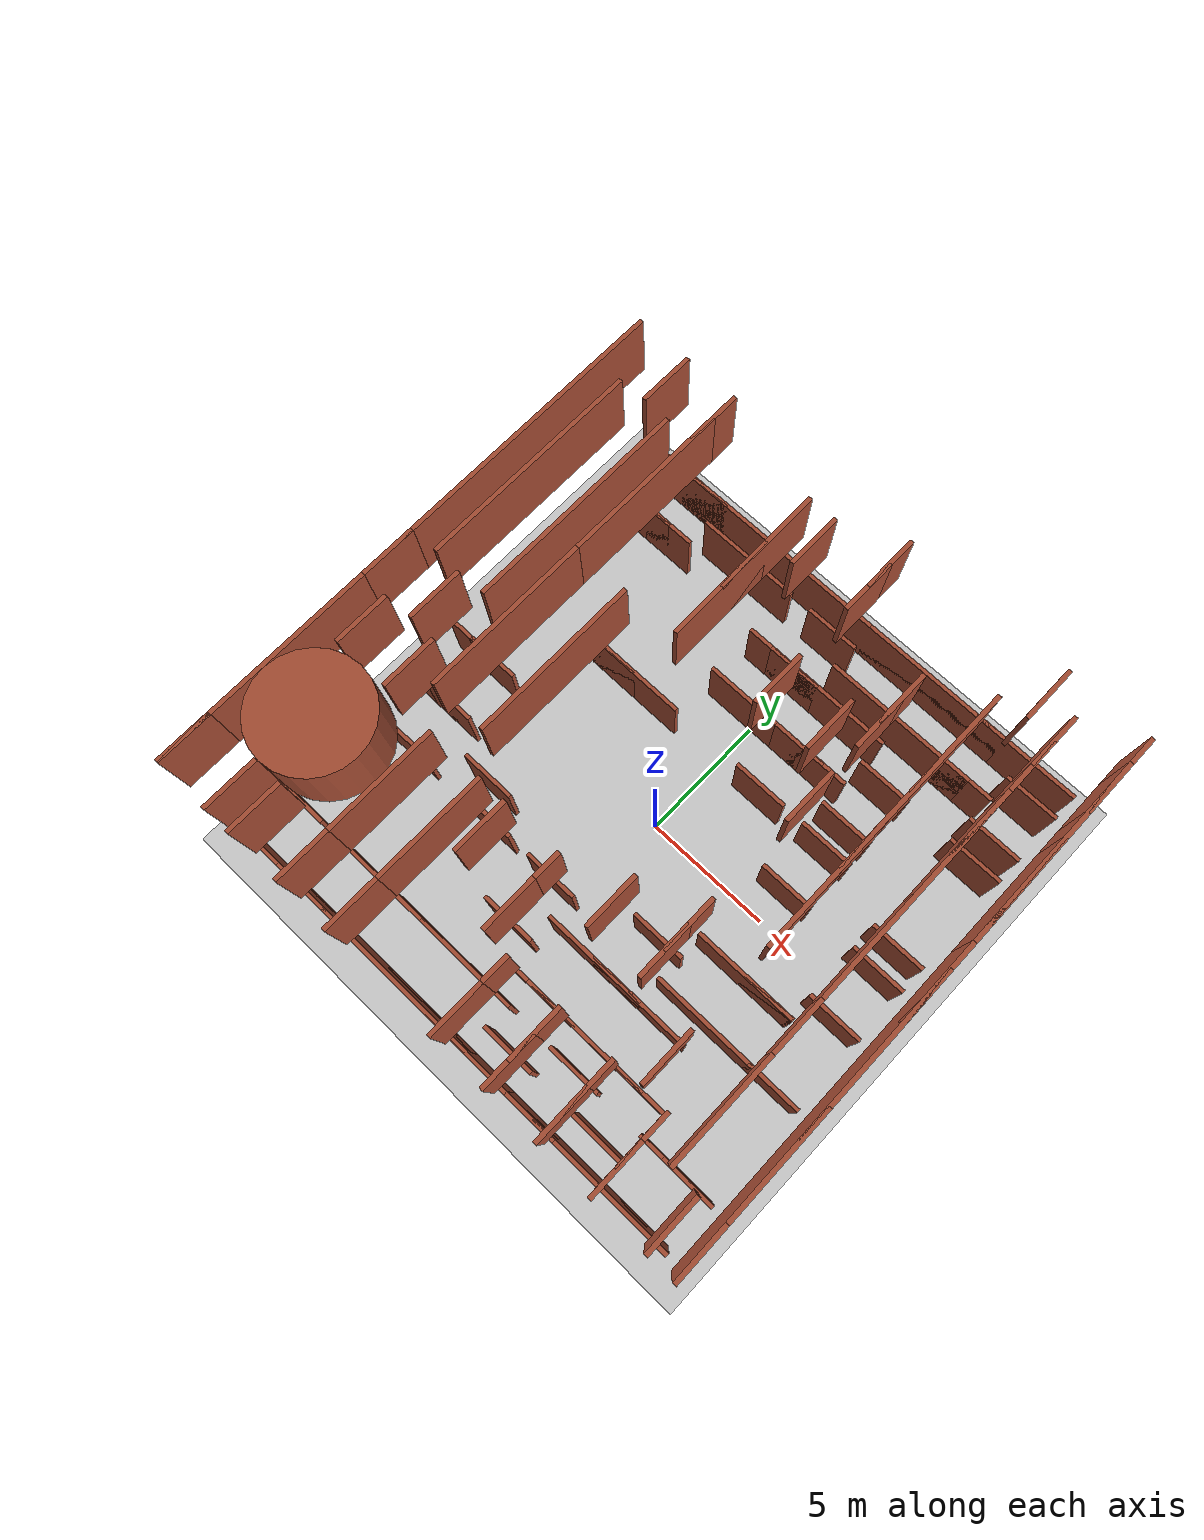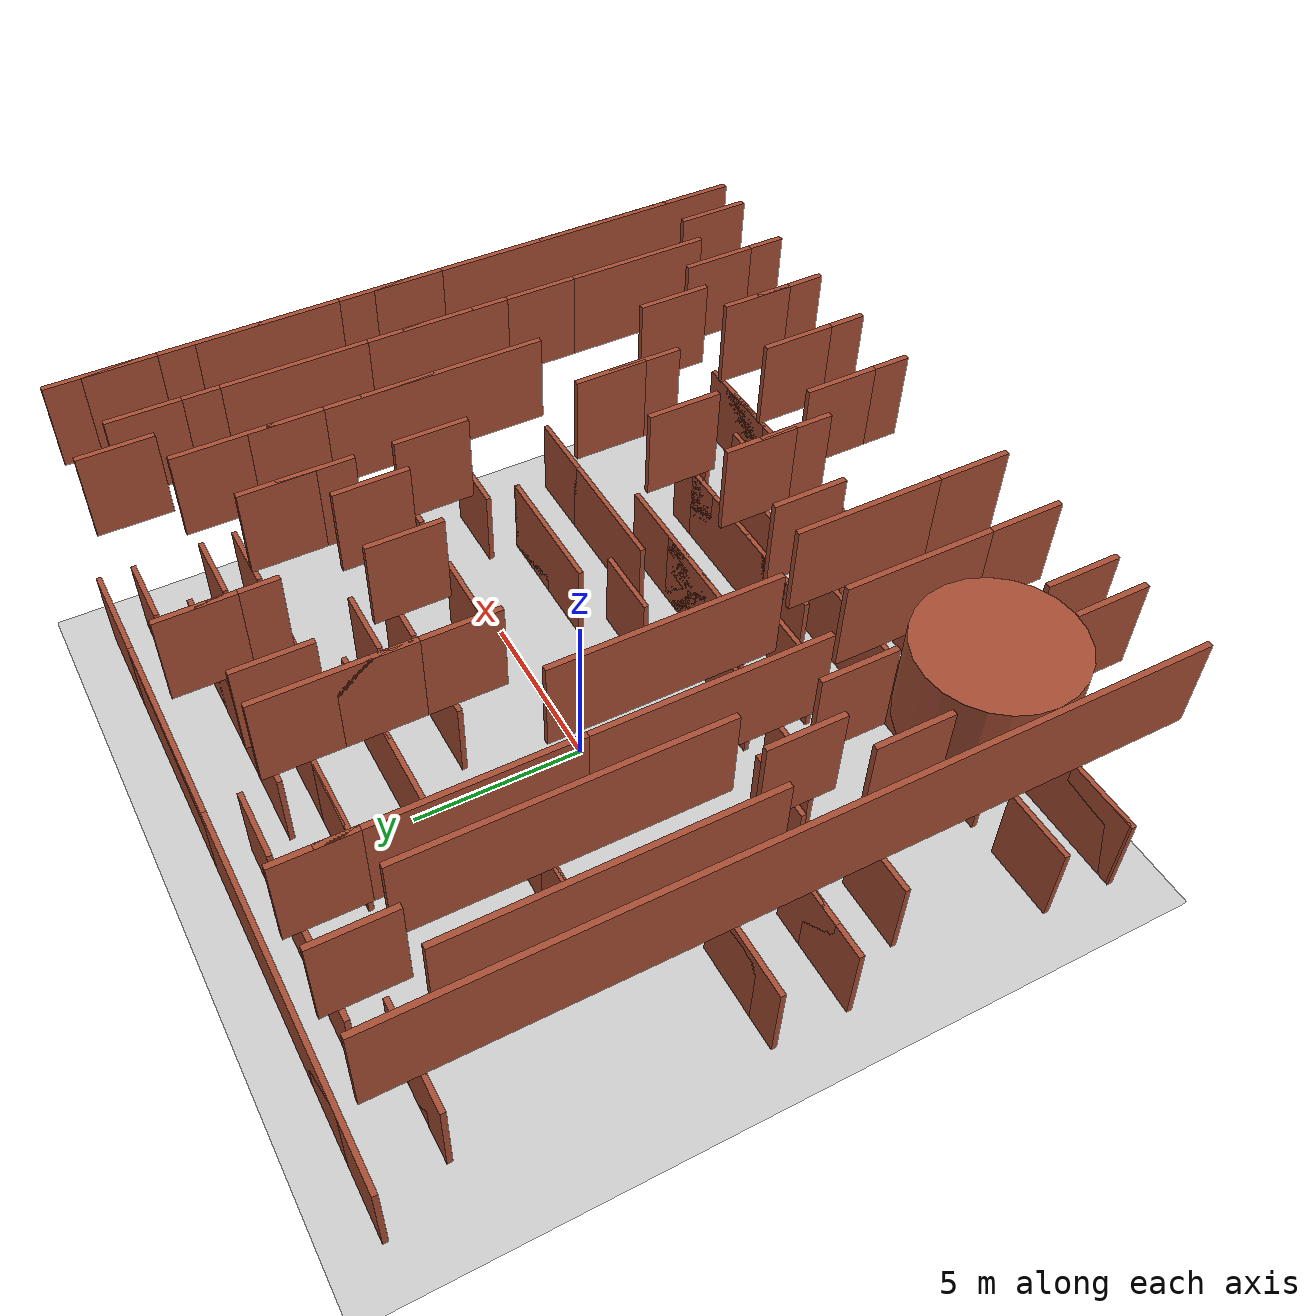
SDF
<sdf version='1.4'>
  <world name='default'>
    <!-- A global light source -->
    <include>
      <uri>model://sun</uri>
    </include>

    <!-- A ground plane -->
    <include>
      <uri>model://ground_plane</uri>
    </include>

    <physics type="ode">
      <real_time_update_rate>1000.0</real_time_update_rate>
      <max_step_size>0.001</max_step_size>
      <real_time_factor>1</real_time_factor>
      <ode>
        <solver>
          <type>quick</type>
          <iters>150</iters>
          <precon_iters>0</precon_iters>
          <sor>1.400000</sor>
          <use_dynamic_moi_rescaling>1</use_dynamic_moi_rescaling>
        </solver>
        <constraints>
          <cfm>0.00001</cfm>
          <erp>0.2</erp>
          <contact_max_correcting_vel>2000.000000</contact_max_correcting_vel>
          <contact_surface_layer>0.01000</contact_surface_layer>
        </constraints>
      </ode>
    </physics>

    <!-- Random World -->
    <include>
      <uri>model://random_world</uri>
    </include>

    <scene>
      <ambient>0.8 0.8 0.8 1</ambient>
      <background>0.7 0.7 0.7 1</background>
      <shadows>true</shadows>
    </scene>

    <gui fullscreen='0'>
      <camera name='user_camera'>
        <pose>0.0 0.0 17.0 0 1.5708 0</pose>
        <view_controller>orbit</view_controller>
      </camera>
    </gui>

  </world>
</sdf>

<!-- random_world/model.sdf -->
<sdf version='1.6'>
  <model name='random_world'>
    <link name='Wall_101'>
      <pose frame=''>-10.075 0 0 0 0 -1.5708</pose>
      <self_collide>0</self_collide>
      <kinematic>0</kinematic>
      <visual name='Wall_101_Visual'>
        <pose frame=''>0 0 8 0 -0 0</pose>
        <geometry>
          <box>
            <size>20 0.15 2.5</size>
          </box>
        </geometry>
        <material>
          <script>
            <uri>file://media/materials/scripts/gazebo.material</uri>
            <name>Gazebo/Bricks</name>
          </script>
          <ambient>1 1 1 1</ambient>
          <diffuse>1 1 1 1</diffuse>
          <specular>0.2 0.2 0.2 1</specular>
          <emissive>0 0 0 1</emissive>
        </material>
        <cast_shadows>1</cast_shadows>
        <transparency>0</transparency>
      </visual>
      <collision name='Wall_101_Collision'>
        <laser_retro>0</laser_retro>
        <max_contacts>10</max_contacts>
        <pose frame=''>0 0 8 0 -0 0</pose>
        <geometry>
          <box>
            <size>20 0.15 2.5</size>
          </box>
        </geometry>
        <surface>
          <friction>
            <ode>
              <mu>1</mu>
              <mu2>1</mu2>
              <fdir1>0 0 0</fdir1>
              <slip1>0</slip1>
              <slip2>0</slip2>
            </ode>
            <torsional>
              <coefficient>1</coefficient>
              <patch_radius>0</patch_radius>
              <surface_radius>0</surface_radius>
              <use_patch_radius>1</use_patch_radius>
              <ode>
                <slip>0</slip>
              </ode>
            </torsional>
          </friction>
          <bounce>
            <restitution_coefficient>0</restitution_coefficient>
            <threshold>1e+06</threshold>
          </bounce>
          <contact>
            <collide_without_contact>0</collide_without_contact>
            <collide_without_contact_bitmask>1</collide_without_contact_bitmask>
            <collide_bitmask>1</collide_bitmask>
            <ode>
              <soft_cfm>0</soft_cfm>
              <soft_erp>0.2</soft_erp>
              <kp>1e+13</kp>
              <kd>1</kd>
              <max_vel>0.01</max_vel>
              <min_depth>0</min_depth>
            </ode>
            <bullet>
              <split_impulse>1</split_impulse>
              <split_impulse_penetration_threshold>-0.01</split_impulse_penetration_threshold>
              <soft_cfm>0</soft_cfm>
              <soft_erp>0.2</soft_erp>
              <kp>1e+13</kp>
              <kd>1</kd>
            </bullet>
          </contact>
        </surface>
      </collision>
    </link>
    <link name='Wall_102'>
      <pose frame=''>-4 10.075 0 0 -0 0</pose>
      <self_collide>0</self_collide>
      <kinematic>0</kinematic>
      <visual name='Wall_102_Visual'>
        <pose frame=''>4 0 1.25 0 -0 0</pose>
        <geometry>
          <box>
            <size>20.15 0.15 2.5</size>
          </box>
        </geometry>
        <material>
          <script>
            <uri>file://media/materials/scripts/gazebo.material</uri>
            <name>Gazebo/Bricks</name>
          </script>
          <ambient>1 1 1 1</ambient>
          <diffuse>1 1 1 1</diffuse>
          <specular>0.2 0.2 0.2 1</specular>
          <emissive>0 0 0 1</emissive>
        </material>
        <cast_shadows>1</cast_shadows>
        <transparency>0</transparency>
      </visual>
      <collision name='Wall_102_Collision'>
        <laser_retro>0</laser_retro>
        <max_contacts>10</max_contacts>
        <pose frame=''>4 0 1.25 0 -0 0</pose>
        <geometry>
          <box>
            <size>20.15 0.15 2.5</size>
          </box>
        </geometry>
        <surface>
          <friction>
            <ode>
              <mu>1</mu>
              <mu2>1</mu2>
              <fdir1>0 0 0</fdir1>
              <slip1>0</slip1>
              <slip2>0</slip2>
            </ode>
            <torsional>
              <coefficient>1</coefficient>
              <patch_radius>0</patch_radius>
              <surface_radius>0</surface_radius>
              <use_patch_radius>1</use_patch_radius>
              <ode>
                <slip>0</slip>
              </ode>
            </torsional>
          </friction>
          <bounce>
            <restitution_coefficient>0</restitution_coefficient>
            <threshold>1e+06</threshold>
          </bounce>
          <contact>
            <collide_without_contact>0</collide_without_contact>
            <collide_without_contact_bitmask>1</collide_without_contact_bitmask>
            <collide_bitmask>1</collide_bitmask>
            <ode>
              <soft_cfm>0</soft_cfm>
              <soft_erp>0.2</soft_erp>
              <kp>1e+13</kp>
              <kd>1</kd>
              <max_vel>0.01</max_vel>
              <min_depth>0</min_depth>
            </ode>
            <bullet>
              <split_impulse>1</split_impulse>
              <split_impulse_penetration_threshold>-0.01</split_impulse_penetration_threshold>
              <soft_cfm>0</soft_cfm>
              <soft_erp>0.2</soft_erp>
              <kp>1e+13</kp>
              <kd>1</kd>
            </bullet>
          </contact>
        </surface>
      </collision>
    </link>
    <link name='Wall_103'>
      <pose frame=''>10.075 0 0 0 0 -1.5708</pose>
      <self_collide>0</self_collide>
      <kinematic>0</kinematic>
      <visual name='Wall_103_Visual'>
        <pose frame=''>0 0 8 0 -0 0</pose>
        <geometry>
          <box>
            <size>20 0.15 2.5</size>
          </box>
        </geometry>
        <material>
          <script>
            <uri>file://media/materials/scripts/gazebo.material</uri>
            <name>Gazebo/Bricks</name>
          </script>
          <ambient>1 1 1 1</ambient>
          <diffuse>1 1 1 1</diffuse>
          <specular>0.2 0.2 0.2 1</specular>
          <emissive>0 0 0 1</emissive>
        </material>
        <cast_shadows>1</cast_shadows>
        <transparency>0</transparency>
      </visual>
      <collision name='Wall_103_Collision'>
        <laser_retro>0</laser_retro>
        <max_contacts>10</max_contacts>
        <pose frame=''>0 0 8 0 -0 0</pose>
        <geometry>
          <box>
            <size>20 0.15 2.5</size>
          </box>
        </geometry>
        <surface>
          <friction>
            <ode>
              <mu>1</mu>
              <mu2>1</mu2>
              <fdir1>0 0 0</fdir1>
              <slip1>0</slip1>
              <slip2>0</slip2>
            </ode>
            <torsional>
              <coefficient>1</coefficient>
              <patch_radius>0</patch_radius>
              <surface_radius>0</surface_radius>
              <use_patch_radius>1</use_patch_radius>
              <ode>
                <slip>0</slip>
              </ode>
            </torsional>
          </friction>
          <bounce>
            <restitution_coefficient>0</restitution_coefficient>
            <threshold>1e+06</threshold>
          </bounce>
          <contact>
            <collide_without_contact>0</collide_without_contact>
            <collide_without_contact_bitmask>1</collide_without_contact_bitmask>
            <collide_bitmask>1</collide_bitmask>
            <ode>
              <soft_cfm>0</soft_cfm>
              <soft_erp>0.2</soft_erp>
              <kp>1e+13</kp>
              <kd>1</kd>
              <max_vel>0.01</max_vel>
              <min_depth>0</min_depth>
            </ode>
            <bullet>
              <split_impulse>1</split_impulse>
              <split_impulse_penetration_threshold>-0.01</split_impulse_penetration_threshold>
              <soft_cfm>0</soft_cfm>
              <soft_erp>0.2</soft_erp>
              <kp>1e+13</kp>
              <kd>1</kd>
            </bullet>
          </contact>
        </surface>
      </collision>
    </link>
    <link name='Wall_104'>
      <pose frame=''>-4 -10.075 0 0 -0 0</pose>
      <self_collide>0</self_collide>
      <kinematic>0</kinematic>
      <visual name='Wall_104_Visual'>
        <pose frame=''>3.925 0 1.25 0 -0 0</pose>
        <geometry>
          <box>
            <size>20.15 0.15 2.5</size>
          </box>
        </geometry>
        <material>
          <script>
            <uri>file://media/materials/scripts/gazebo.material</uri>
            <name>Gazebo/Bricks</name>
          </script>
          <ambient>1 1 1 1</ambient>
          <diffuse>1 1 1 1</diffuse>
          <specular>0.2 0.2 0.2 1</specular>
          <emissive>0 0 0 1</emissive>
        </material>
        <cast_shadows>1</cast_shadows>
        <transparency>0</transparency>
      </visual>
      <collision name='Wall_104_Collision'>
        <laser_retro>0</laser_retro>
        <max_contacts>10</max_contacts>
        <pose frame=''>3.925 0 1.25 0 -0 0</pose>
        <geometry>
          <box>
            <size>20.15 0.15 2.5</size>
          </box>
        </geometry>
        <surface>
          <friction>
            <ode>
              <mu>1</mu>
              <mu2>1</mu2>
              <fdir1>0 0 0</fdir1>
              <slip1>0</slip1>
              <slip2>0</slip2>
            </ode>
            <torsional>
              <coefficient>1</coefficient>
              <patch_radius>0</patch_radius>
              <surface_radius>0</surface_radius>
              <use_patch_radius>1</use_patch_radius>
              <ode>
                <slip>0</slip>
              </ode>
            </torsional>
          </friction>
          <bounce>
            <restitution_coefficient>0</restitution_coefficient>
            <threshold>1e+06</threshold>
          </bounce>
          <contact>
            <collide_without_contact>0</collide_without_contact>
            <collide_without_contact_bitmask>1</collide_without_contact_bitmask>
            <collide_bitmask>1</collide_bitmask>
            <ode>
              <soft_cfm>0</soft_cfm>
              <soft_erp>0.2</soft_erp>
              <kp>1e+13</kp>
              <kd>1</kd>
              <max_vel>0.01</max_vel>
              <min_depth>0</min_depth>
            </ode>
            <bullet>
              <split_impulse>1</split_impulse>
              <split_impulse_penetration_threshold>-0.01</split_impulse_penetration_threshold>
              <soft_cfm>0</soft_cfm>
              <soft_erp>0.2</soft_erp>
              <kp>1e+13</kp>
              <kd>1</kd>
            </bullet>
          </contact>
        </surface>
      </collision>
    </link>
    <link name='Wall_Room_H_1'>
      <pose frame=''>1.075 -9 0 0 0 -1.5708</pose>
      <self_collide>0</self_collide>
      <kinematic>0</kinematic>
      <visual name='Wall_Room_H_1_Visual'>
        <pose frame=''>0 0 8 0 -0 0</pose>
        <geometry>
          <box>
            <size>2 0.15 2.5</size>
          </box>
        </geometry>
        <material>
          <script>
            <uri>file://media/materials/scripts/gazebo.material</uri>
            <name>Gazebo/Bricks</name>
          </script>
          <ambient>1 1 1 1</ambient>
          <diffuse>1 1 1 1</diffuse>
          <specular>0.2 0.2 0.2 1</specular>
          <emissive>0 0 0 1</emissive>
        </material>
        <cast_shadows>1</cast_shadows>
        <transparency>0</transparency>
      </visual>
      <collision name='Wall_Room_H_1_Collision'>
        <laser_retro>0</laser_retro>
        <max_contacts>10</max_contacts>
        <pose frame=''>0 0 8 0 -0 0</pose>
        <geometry>
          <box>
            <size>2 0.15 2.5</size>
          </box>
        </geometry>
        <surface>
          <friction>
            <ode>
              <mu>1</mu>
              <mu2>1</mu2>
              <fdir1>0 0 0</fdir1>
              <slip1>0</slip1>
              <slip2>0</slip2>
            </ode>
            <torsional>
              <coefficient>1</coefficient>
              <patch_radius>0</patch_radius>
              <surface_radius>0</surface_radius>
              <use_patch_radius>1</use_patch_radius>
              <ode>
                <slip>0</slip>
              </ode>
            </torsional>
          </friction>
          <bounce>
            <restitution_coefficient>0</restitution_coefficient>
            <threshold>1e+06</threshold>
          </bounce>
          <contact>
            <collide_without_contact>0</collide_without_contact>
            <collide_without_contact_bitmask>1</collide_without_contact_bitmask>
            <collide_bitmask>1</collide_bitmask>
            <ode>
              <soft_cfm>0</soft_cfm>
              <soft_erp>0.2</soft_erp>
              <kp>1e+13</kp>
              <kd>1</kd>
              <max_vel>0.01</max_vel>
              <min_depth>0</min_depth>
            </ode>
            <bullet>
              <split_impulse>1</split_impulse>
              <split_impulse_penetration_threshold>-0.01</split_impulse_penetration_threshold>
              <soft_cfm>0</soft_cfm>
              <soft_erp>0.2</soft_erp>
              <kp>1e+13</kp>
              <kd>1</kd>
            </bullet>
          </contact>
        </surface>
      </collision>
    </link>
    <link name='Wall_Room_H_2'>
      <pose frame=''>-3.075 -9 0 0 0 -1.5708</pose>
      <self_collide>0</self_collide>
      <kinematic>0</kinematic>
      <visual name='Wall_Room_H_2_Visual'>
        <pose frame=''>0 0 8 0 -0 0</pose>
        <geometry>
          <box>
            <size>2 0.15 2.5</size>
          </box>
        </geometry>
        <material>
          <script>
            <uri>file://media/materials/scripts/gazebo.material</uri>
            <name>Gazebo/Bricks</name>
          </script>
          <ambient>1 1 1 1</ambient>
          <diffuse>1 1 1 1</diffuse>
          <specular>0.2 0.2 0.2 1</specular>
          <emissive>0 0 0 1</emissive>
        </material>
        <cast_shadows>1</cast_shadows>
        <transparency>0</transparency>
      </visual>
      <collision name='Wall_Room_H_2_Collision'>
        <laser_retro>0</laser_retro>
        <max_contacts>10</max_contacts>
        <pose frame=''>0 0 8 0 -0 0</pose>
        <geometry>
          <box>
            <size>2 0.15 2.5</size>
          </box>
        </geometry>
        <surface>
          <friction>
            <ode>
              <mu>1</mu>
              <mu2>1</mu2>
              <fdir1>0 0 0</fdir1>
              <slip1>0</slip1>
              <slip2>0</slip2>
            </ode>
            <torsional>
              <coefficient>1</coefficient>
              <patch_radius>0</patch_radius>
              <surface_radius>0</surface_radius>
              <use_patch_radius>1</use_patch_radius>
              <ode>
                <slip>0</slip>
              </ode>
            </torsional>
          </friction>
          <bounce>
            <restitution_coefficient>0</restitution_coefficient>
            <threshold>1e+06</threshold>
          </bounce>
          <contact>
            <collide_without_contact>0</collide_without_contact>
            <collide_without_contact_bitmask>1</collide_without_contact_bitmask>
            <collide_bitmask>1</collide_bitmask>
            <ode>
              <soft_cfm>0</soft_cfm>
              <soft_erp>0.2</soft_erp>
              <kp>1e+13</kp>
              <kd>1</kd>
              <max_vel>0.01</max_vel>
              <min_depth>0</min_depth>
            </ode>
            <bullet>
              <split_impulse>1</split_impulse>
              <split_impulse_penetration_threshold>-0.01</split_impulse_penetration_threshold>
              <soft_cfm>0</soft_cfm>
              <soft_erp>0.2</soft_erp>
              <kp>1e+13</kp>
              <kd>1</kd>
            </bullet>
          </contact>
        </surface>
      </collision>
    </link>
    <link name='Wall_Room_V_3'>
      <pose frame=''>-1 -8.075 0 0 -0 0</pose>
      <self_collide>0</self_collide>
      <kinematic>0</kinematic>
      <visual name='Wall_Room_V_3_Visual'>
        <pose frame=''>0 0 1.25 0 -0 0</pose>
        <geometry>
          <box>
            <size>4.15 0.15 2.5</size>
          </box>
        </geometry>
        <material>
          <script>
            <uri>file://media/materials/scripts/gazebo.material</uri>
            <name>Gazebo/Bricks</name>
          </script>
          <ambient>1 1 1 1</ambient>
          <diffuse>1 1 1 1</diffuse>
          <specular>0.2 0.2 0.2 1</specular>
          <emissive>0 0 0 1</emissive>
        </material>
        <cast_shadows>1</cast_shadows>
        <transparency>0</transparency>
      </visual>
      <collision name='Wall_Room_V_3_Collision'>
        <laser_retro>0</laser_retro>
        <max_contacts>10</max_contacts>
        <pose frame=''>0 0 1.25 0 -0 0</pose>
        <geometry>
          <box>
            <size>4.15 0.15 2.5</size>
          </box>
        </geometry>
        <surface>
          <friction>
            <ode>
              <mu>1</mu>
              <mu2>1</mu2>
              <fdir1>0 0 0</fdir1>
              <slip1>0</slip1>
              <slip2>0</slip2>
            </ode>
            <torsional>
              <coefficient>1</coefficient>
              <patch_radius>0</patch_radius>
              <surface_radius>0</surface_radius>
              <use_patch_radius>1</use_patch_radius>
              <ode>
                <slip>0</slip>
              </ode>
            </torsional>
          </friction>
          <bounce>
            <restitution_coefficient>0</restitution_coefficient>
            <threshold>1e+06</threshold>
          </bounce>
          <contact>
            <collide_without_contact>0</collide_without_contact>
            <collide_without_contact_bitmask>1</collide_without_contact_bitmask>
            <collide_bitmask>1</collide_bitmask>
            <ode>
              <soft_cfm>0</soft_cfm>
              <soft_erp>0.2</soft_erp>
              <kp>1e+13</kp>
              <kd>1</kd>
              <max_vel>0.01</max_vel>
              <min_depth>0</min_depth>
            </ode>
            <bullet>
              <split_impulse>1</split_impulse>
              <split_impulse_penetration_threshold>-0.01</split_impulse_penetration_threshold>
              <soft_cfm>0</soft_cfm>
              <soft_erp>0.2</soft_erp>
              <kp>1e+13</kp>
              <kd>1</kd>
            </bullet>
          </contact>
        </surface>
      </collision>
    </link>
    <link name='Wall_Room_V_4'>
      <pose frame=''>-1 -10.075 0 0 -0 0</pose>
      <self_collide>0</self_collide>
      <kinematic>0</kinematic>
      <visual name='Wall_Room_V_4_Visual'>
        <pose frame=''>0 0 1.25 0 -0 0</pose>
        <geometry>
          <box>
            <size>4.15 0.15 2.5</size>
          </box>
        </geometry>
        <material>
          <script>
            <uri>file://media/materials/scripts/gazebo.material</uri>
            <name>Gazebo/Bricks</name>
          </script>
          <ambient>1 1 1 1</ambient>
          <diffuse>1 1 1 1</diffuse>
          <specular>0.2 0.2 0.2 1</specular>
          <emissive>0 0 0 1</emissive>
        </material>
        <cast_shadows>1</cast_shadows>
        <transparency>0</transparency>
      </visual>
      <collision name='Wall_Room_V_4_Collision'>
        <laser_retro>0</laser_retro>
        <max_contacts>10</max_contacts>
        <pose frame=''>0 0 1.25 0 -0 0</pose>
        <geometry>
          <box>
            <size>4.15 0.15 2.5</size>
          </box>
        </geometry>
        <surface>
          <friction>
            <ode>
              <mu>1</mu>
              <mu2>1</mu2>
              <fdir1>0 0 0</fdir1>
              <slip1>0</slip1>
              <slip2>0</slip2>
            </ode>
            <torsional>
              <coefficient>1</coefficient>
              <patch_radius>0</patch_radius>
              <surface_radius>0</surface_radius>
              <use_patch_radius>1</use_patch_radius>
              <ode>
                <slip>0</slip>
              </ode>
            </torsional>
          </friction>
          <bounce>
            <restitution_coefficient>0</restitution_coefficient>
            <threshold>1e+06</threshold>
          </bounce>
          <contact>
            <collide_without_contact>0</collide_without_contact>
            <collide_without_contact_bitmask>1</collide_without_contact_bitmask>
            <collide_bitmask>1</collide_bitmask>
            <ode>
              <soft_cfm>0</soft_cfm>
              <soft_erp>0.2</soft_erp>
              <kp>1e+13</kp>
              <kd>1</kd>
              <max_vel>0.01</max_vel>
              <min_depth>0</min_depth>
            </ode>
            <bullet>
              <split_impulse>1</split_impulse>
              <split_impulse_penetration_threshold>-0.01</split_impulse_penetration_threshold>
              <soft_cfm>0</soft_cfm>
              <soft_erp>0.2</soft_erp>
              <kp>1e+13</kp>
              <kd>1</kd>
            </bullet>
          </contact>
        </surface>
      </collision>
    </link>
    <link name='Wall_Room_H_5'>
      <pose frame=''>6.075 -6 0 0 0 -1.5708</pose>
      <self_collide>0</self_collide>
      <kinematic>0</kinematic>
      <visual name='Wall_Room_H_5_Visual'>
        <pose frame=''>0 0 8 0 -0 0</pose>
        <geometry>
          <box>
            <size>2 0.15 2.5</size>
          </box>
        </geometry>
        <material>
          <script>
            <uri>file://media/materials/scripts/gazebo.material</uri>
            <name>Gazebo/Bricks</name>
          </script>
          <ambient>1 1 1 1</ambient>
          <diffuse>1 1 1 1</diffuse>
          <specular>0.2 0.2 0.2 1</specular>
          <emissive>0 0 0 1</emissive>
        </material>
        <cast_shadows>1</cast_shadows>
        <transparency>0</transparency>
      </visual>
      <collision name='Wall_Room_H_5_Collision'>
        <laser_retro>0</laser_retro>
        <max_contacts>10</max_contacts>
        <pose frame=''>0 0 8 0 -0 0</pose>
        <geometry>
          <box>
            <size>2 0.15 2.5</size>
          </box>
        </geometry>
        <surface>
          <friction>
            <ode>
              <mu>1</mu>
              <mu2>1</mu2>
              <fdir1>0 0 0</fdir1>
              <slip1>0</slip1>
              <slip2>0</slip2>
            </ode>
            <torsional>
              <coefficient>1</coefficient>
              <patch_radius>0</patch_radius>
              <surface_radius>0</surface_radius>
              <use_patch_radius>1</use_patch_radius>
              <ode>
                <slip>0</slip>
              </ode>
            </torsional>
          </friction>
          <bounce>
            <restitution_coefficient>0</restitution_coefficient>
            <threshold>1e+06</threshold>
          </bounce>
          <contact>
            <collide_without_contact>0</collide_without_contact>
            <collide_without_contact_bitmask>1</collide_without_contact_bitmask>
            <collide_bitmask>1</collide_bitmask>
            <ode>
              <soft_cfm>0</soft_cfm>
              <soft_erp>0.2</soft_erp>
              <kp>1e+13</kp>
              <kd>1</kd>
              <max_vel>0.01</max_vel>
              <min_depth>0</min_depth>
            </ode>
            <bullet>
              <split_impulse>1</split_impulse>
              <split_impulse_penetration_threshold>-0.01</split_impulse_penetration_threshold>
              <soft_cfm>0</soft_cfm>
              <soft_erp>0.2</soft_erp>
              <kp>1e+13</kp>
              <kd>1</kd>
            </bullet>
          </contact>
        </surface>
      </collision>
    </link>
    <link name='Wall_Room_H_6'>
      <pose frame=''>0.075 -6 0 0 0 -1.5708</pose>
      <self_collide>0</self_collide>
      <kinematic>0</kinematic>
      <visual name='Wall_Room_H_6_Visual'>
        <pose frame=''>0 0 8 0 -0 0</pose>
        <geometry>
          <box>
            <size>2 0.15 2.5</size>
          </box>
        </geometry>
        <material>
          <script>
            <uri>file://media/materials/scripts/gazebo.material</uri>
            <name>Gazebo/Bricks</name>
          </script>
          <ambient>1 1 1 1</ambient>
          <diffuse>1 1 1 1</diffuse>
          <specular>0.2 0.2 0.2 1</specular>
          <emissive>0 0 0 1</emissive>
        </material>
        <cast_shadows>1</cast_shadows>
        <transparency>0</transparency>
      </visual>
      <collision name='Wall_Room_H_6_Collision'>
        <laser_retro>0</laser_retro>
        <max_contacts>10</max_contacts>
        <pose frame=''>0 0 8 0 -0 0</pose>
        <geometry>
          <box>
            <size>2 0.15 2.5</size>
          </box>
        </geometry>
        <surface>
          <friction>
            <ode>
              <mu>1</mu>
              <mu2>1</mu2>
              <fdir1>0 0 0</fdir1>
              <slip1>0</slip1>
              <slip2>0</slip2>
            </ode>
            <torsional>
              <coefficient>1</coefficient>
              <patch_radius>0</patch_radius>
              <surface_radius>0</surface_radius>
              <use_patch_radius>1</use_patch_radius>
              <ode>
                <slip>0</slip>
              </ode>
            </torsional>
          </friction>
          <bounce>
            <restitution_coefficient>0</restitution_coefficient>
            <threshold>1e+06</threshold>
          </bounce>
          <contact>
            <collide_without_contact>0</collide_without_contact>
            <collide_without_contact_bitmask>1</collide_without_contact_bitmask>
            <collide_bitmask>1</collide_bitmask>
            <ode>
              <soft_cfm>0</soft_cfm>
              <soft_erp>0.2</soft_erp>
              <kp>1e+13</kp>
              <kd>1</kd>
              <max_vel>0.01</max_vel>
              <min_depth>0</min_depth>
            </ode>
            <bullet>
              <split_impulse>1</split_impulse>
              <split_impulse_penetration_threshold>-0.01</split_impulse_penetration_threshold>
              <soft_cfm>0</soft_cfm>
              <soft_erp>0.2</soft_erp>
              <kp>1e+13</kp>
              <kd>1</kd>
            </bullet>
          </contact>
        </surface>
      </collision>
    </link>
    <link name='Wall_Room_V_7'>
      <pose frame=''>3 -5.075 0 0 -0 0</pose>
      <self_collide>0</self_collide>
      <kinematic>0</kinematic>
      <visual name='Wall_Room_V_7_Visual'>
        <pose frame=''>0 0 1.25 0 -0 0</pose>
        <geometry>
          <box>
            <size>6.15 0.15 2.5</size>
          </box>
        </geometry>
        <material>
          <script>
            <uri>file://media/materials/scripts/gazebo.material</uri>
            <name>Gazebo/Bricks</name>
          </script>
          <ambient>1 1 1 1</ambient>
          <diffuse>1 1 1 1</diffuse>
          <specular>0.2 0.2 0.2 1</specular>
          <emissive>0 0 0 1</emissive>
        </material>
        <cast_shadows>1</cast_shadows>
        <transparency>0</transparency>
      </visual>
      <collision name='Wall_Room_V_7_Collision'>
        <laser_retro>0</laser_retro>
        <max_contacts>10</max_contacts>
        <pose frame=''>0 0 1.25 0 -0 0</pose>
        <geometry>
          <box>
            <size>6.15 0.15 2.5</size>
          </box>
        </geometry>
        <surface>
          <friction>
            <ode>
              <mu>1</mu>
              <mu2>1</mu2>
              <fdir1>0 0 0</fdir1>
              <slip1>0</slip1>
              <slip2>0</slip2>
            </ode>
            <torsional>
              <coefficient>1</coefficient>
              <patch_radius>0</patch_radius>
              <surface_radius>0</surface_radius>
              <use_patch_radius>1</use_patch_radius>
              <ode>
                <slip>0</slip>
              </ode>
            </torsional>
          </friction>
          <bounce>
            <restitution_coefficient>0</restitution_coefficient>
            <threshold>1e+06</threshold>
          </bounce>
          <contact>
            <collide_without_contact>0</collide_without_contact>
            <collide_without_contact_bitmask>1</collide_without_contact_bitmask>
            <collide_bitmask>1</collide_bitmask>
            <ode>
              <soft_cfm>0</soft_cfm>
              <soft_erp>0.2</soft_erp>
              <kp>1e+13</kp>
              <kd>1</kd>
              <max_vel>0.01</max_vel>
              <min_depth>0</min_depth>
            </ode>
            <bullet>
              <split_impulse>1</split_impulse>
              <split_impulse_penetration_threshold>-0.01</split_impulse_penetration_threshold>
              <soft_cfm>0</soft_cfm>
              <soft_erp>0.2</soft_erp>
              <kp>1e+13</kp>
              <kd>1</kd>
            </bullet>
          </contact>
        </surface>
      </collision>
    </link>
    <link name='Wall_Room_V_8'>
      <pose frame=''>3 -7.075 0 0 -0 0</pose>
      <self_collide>0</self_collide>
      <kinematic>0</kinematic>
      <visual name='Wall_Room_V_8_Visual'>
        <pose frame=''>0 0 1.25 0 -0 0</pose>
        <geometry>
          <box>
            <size>6.15 0.15 2.5</size>
          </box>
        </geometry>
        <material>
          <script>
            <uri>file://media/materials/scripts/gazebo.material</uri>
            <name>Gazebo/Bricks</name>
          </script>
          <ambient>1 1 1 1</ambient>
          <diffuse>1 1 1 1</diffuse>
          <specular>0.2 0.2 0.2 1</specular>
          <emissive>0 0 0 1</emissive>
        </material>
        <cast_shadows>1</cast_shadows>
        <transparency>0</transparency>
      </visual>
      <collision name='Wall_Room_V_8_Collision'>
        <laser_retro>0</laser_retro>
        <max_contacts>10</max_contacts>
        <pose frame=''>0 0 1.25 0 -0 0</pose>
        <geometry>
          <box>
            <size>6.15 0.15 2.5</size>
          </box>
        </geometry>
        <surface>
          <friction>
            <ode>
              <mu>1</mu>
              <mu2>1</mu2>
              <fdir1>0 0 0</fdir1>
              <slip1>0</slip1>
              <slip2>0</slip2>
            </ode>
            <torsional>
              <coefficient>1</coefficient>
              <patch_radius>0</patch_radius>
              <surface_radius>0</surface_radius>
              <use_patch_radius>1</use_patch_radius>
              <ode>
                <slip>0</slip>
              </ode>
            </torsional>
          </friction>
          <bounce>
            <restitution_coefficient>0</restitution_coefficient>
            <threshold>1e+06</threshold>
          </bounce>
          <contact>
            <collide_without_contact>0</collide_without_contact>
            <collide_without_contact_bitmask>1</collide_without_contact_bitmask>
            <collide_bitmask>1</collide_bitmask>
            <ode>
              <soft_cfm>0</soft_cfm>
              <soft_erp>0.2</soft_erp>
              <kp>1e+13</kp>
              <kd>1</kd>
              <max_vel>0.01</max_vel>
              <min_depth>0</min_depth>
            </ode>
            <bullet>
              <split_impulse>1</split_impulse>
              <split_impulse_penetration_threshold>-0.01</split_impulse_penetration_threshold>
              <soft_cfm>0</soft_cfm>
              <soft_erp>0.2</soft_erp>
              <kp>1e+13</kp>
              <kd>1</kd>
            </bullet>
          </contact>
        </surface>
      </collision>
    </link>
    <link name='Wall_Room_H_9'>
      <pose frame=''>-4.075 0 0 0 0 -1.5708</pose>
      <self_collide>0</self_collide>
      <kinematic>0</kinematic>
      <visual name='Wall_Room_H_9_Visual'>
        <pose frame=''>0 0 8 0 -0 0</pose>
        <geometry>
          <box>
            <size>6 0.15 2.5</size>
          </box>
        </geometry>
        <material>
          <script>
            <uri>file://media/materials/scripts/gazebo.material</uri>
            <name>Gazebo/Bricks</name>
          </script>
          <ambient>1 1 1 1</ambient>
          <diffuse>1 1 1 1</diffuse>
          <specular>0.2 0.2 0.2 1</specular>
          <emissive>0 0 0 1</emissive>
        </material>
        <cast_shadows>1</cast_shadows>
        <transparency>0</transparency>
      </visual>
      <collision name='Wall_Room_H_9_Collision'>
        <laser_retro>0</laser_retro>
        <max_contacts>10</max_contacts>
        <pose frame=''>0 0 8 0 -0 0</pose>
        <geometry>
          <box>
            <size>6 0.15 2.5</size>
          </box>
        </geometry>
        <surface>
          <friction>
            <ode>
              <mu>1</mu>
              <mu2>1</mu2>
              <fdir1>0 0 0</fdir1>
              <slip1>0</slip1>
              <slip2>0</slip2>
            </ode>
            <torsional>
              <coefficient>1</coefficient>
              <patch_radius>0</patch_radius>
              <surface_radius>0</surface_radius>
              <use_patch_radius>1</use_patch_radius>
              <ode>
                <slip>0</slip>
              </ode>
            </torsional>
          </friction>
          <bounce>
            <restitution_coefficient>0</restitution_coefficient>
            <threshold>1e+06</threshold>
          </bounce>
          <contact>
            <collide_without_contact>0</collide_without_contact>
            <collide_without_contact_bitmask>1</collide_without_contact_bitmask>
            <collide_bitmask>1</collide_bitmask>
            <ode>
              <soft_cfm>0</soft_cfm>
              <soft_erp>0.2</soft_erp>
              <kp>1e+13</kp>
              <kd>1</kd>
              <max_vel>0.01</max_vel>
              <min_depth>0</min_depth>
            </ode>
            <bullet>
              <split_impulse>1</split_impulse>
              <split_impulse_penetration_threshold>-0.01</split_impulse_penetration_threshold>
              <soft_cfm>0</soft_cfm>
              <soft_erp>0.2</soft_erp>
              <kp>1e+13</kp>
              <kd>1</kd>
            </bullet>
          </contact>
        </surface>
      </collision>
    </link>
    <link name='Wall_Room_H_10'>
      <pose frame=''>-6.075 0 0 0 0 -1.5708</pose>
      <self_collide>0</self_collide>
      <kinematic>0</kinematic>
      <visual name='Wall_Room_H_10_Visual'>
        <pose frame=''>0 0 8 0 -0 0</pose>
        <geometry>
          <box>
            <size>6 0.15 2.5</size>
          </box>
        </geometry>
        <material>
          <script>
            <uri>file://media/materials/scripts/gazebo.material</uri>
            <name>Gazebo/Bricks</name>
          </script>
          <ambient>1 1 1 1</ambient>
          <diffuse>1 1 1 1</diffuse>
          <specular>0.2 0.2 0.2 1</specular>
          <emissive>0 0 0 1</emissive>
        </material>
        <cast_shadows>1</cast_shadows>
        <transparency>0</transparency>
      </visual>
      <collision name='Wall_Room_H_10_Collision'>
        <laser_retro>0</laser_retro>
        <max_contacts>10</max_contacts>
        <pose frame=''>0 0 8 0 -0 0</pose>
        <geometry>
          <box>
            <size>6 0.15 2.5</size>
          </box>
        </geometry>
        <surface>
          <friction>
            <ode>
              <mu>1</mu>
              <mu2>1</mu2>
              <fdir1>0 0 0</fdir1>
              <slip1>0</slip1>
              <slip2>0</slip2>
            </ode>
            <torsional>
              <coefficient>1</coefficient>
              <patch_radius>0</patch_radius>
              <surface_radius>0</surface_radius>
              <use_patch_radius>1</use_patch_radius>
              <ode>
                <slip>0</slip>
              </ode>
            </torsional>
          </friction>
          <bounce>
            <restitution_coefficient>0</restitution_coefficient>
            <threshold>1e+06</threshold>
          </bounce>
          <contact>
            <collide_without_contact>0</collide_without_contact>
            <collide_without_contact_bitmask>1</collide_without_contact_bitmask>
            <collide_bitmask>1</collide_bitmask>
            <ode>
              <soft_cfm>0</soft_cfm>
              <soft_erp>0.2</soft_erp>
              <kp>1e+13</kp>
              <kd>1</kd>
              <max_vel>0.01</max_vel>
              <min_depth>0</min_depth>
            </ode>
            <bullet>
              <split_impulse>1</split_impulse>
              <split_impulse_penetration_threshold>-0.01</split_impulse_penetration_threshold>
              <soft_cfm>0</soft_cfm>
              <soft_erp>0.2</soft_erp>
              <kp>1e+13</kp>
              <kd>1</kd>
            </bullet>
          </contact>
        </surface>
      </collision>
    </link>
    <link name='Wall_Room_V_11'>
      <pose frame=''>-5 3.075 0 0 -0 0</pose>
      <self_collide>0</self_collide>
      <kinematic>0</kinematic>
      <visual name='Wall_Room_V_11_Visual'>
        <pose frame=''>0 0 1.25 0 -0 0</pose>
        <geometry>
          <box>
            <size>2.15 0.15 2.5</size>
          </box>
        </geometry>
        <material>
          <script>
            <uri>file://media/materials/scripts/gazebo.material</uri>
            <name>Gazebo/Bricks</name>
          </script>
          <ambient>1 1 1 1</ambient>
          <diffuse>1 1 1 1</diffuse>
          <specular>0.2 0.2 0.2 1</specular>
          <emissive>0 0 0 1</emissive>
        </material>
        <cast_shadows>1</cast_shadows>
        <transparency>0</transparency>
      </visual>
      <collision name='Wall_Room_V_11_Collision'>
        <laser_retro>0</laser_retro>
        <max_contacts>10</max_contacts>
        <pose frame=''>0 0 1.25 0 -0 0</pose>
        <geometry>
          <box>
            <size>2.15 0.15 2.5</size>
          </box>
        </geometry>
        <surface>
          <friction>
            <ode>
              <mu>1</mu>
              <mu2>1</mu2>
              <fdir1>0 0 0</fdir1>
              <slip1>0</slip1>
              <slip2>0</slip2>
            </ode>
            <torsional>
              <coefficient>1</coefficient>
              <patch_radius>0</patch_radius>
              <surface_radius>0</surface_radius>
              <use_patch_radius>1</use_patch_radius>
              <ode>
                <slip>0</slip>
              </ode>
            </torsional>
          </friction>
          <bounce>
            <restitution_coefficient>0</restitution_coefficient>
            <threshold>1e+06</threshold>
          </bounce>
          <contact>
            <collide_without_contact>0</collide_without_contact>
            <collide_without_contact_bitmask>1</collide_without_contact_bitmask>
            <collide_bitmask>1</collide_bitmask>
            <ode>
              <soft_cfm>0</soft_cfm>
              <soft_erp>0.2</soft_erp>
              <kp>1e+13</kp>
              <kd>1</kd>
              <max_vel>0.01</max_vel>
              <min_depth>0</min_depth>
            </ode>
            <bullet>
              <split_impulse>1</split_impulse>
              <split_impulse_penetration_threshold>-0.01</split_impulse_penetration_threshold>
              <soft_cfm>0</soft_cfm>
              <soft_erp>0.2</soft_erp>
              <kp>1e+13</kp>
              <kd>1</kd>
            </bullet>
          </contact>
        </surface>
      </collision>
    </link>
    <link name='Wall_Room_V_12'>
      <pose frame=''>-5 -3.075 0 0 -0 0</pose>
      <self_collide>0</self_collide>
      <kinematic>0</kinematic>
      <visual name='Wall_Room_V_12_Visual'>
        <pose frame=''>0 0 1.25 0 -0 0</pose>
        <geometry>
          <box>
            <size>2.15 0.15 2.5</size>
          </box>
        </geometry>
        <material>
          <script>
            <uri>file://media/materials/scripts/gazebo.material</uri>
            <name>Gazebo/Bricks</name>
          </script>
          <ambient>1 1 1 1</ambient>
          <diffuse>1 1 1 1</diffuse>
          <specular>0.2 0.2 0.2 1</specular>
          <emissive>0 0 0 1</emissive>
        </material>
        <cast_shadows>1</cast_shadows>
        <transparency>0</transparency>
      </visual>
      <collision name='Wall_Room_V_12_Collision'>
        <laser_retro>0</laser_retro>
        <max_contacts>10</max_contacts>
        <pose frame=''>0 0 1.25 0 -0 0</pose>
        <geometry>
          <box>
            <size>2.15 0.15 2.5</size>
          </box>
        </geometry>
        <surface>
          <friction>
            <ode>
              <mu>1</mu>
              <mu2>1</mu2>
              <fdir1>0 0 0</fdir1>
              <slip1>0</slip1>
              <slip2>0</slip2>
            </ode>
            <torsional>
              <coefficient>1</coefficient>
              <patch_radius>0</patch_radius>
              <surface_radius>0</surface_radius>
              <use_patch_radius>1</use_patch_radius>
              <ode>
                <slip>0</slip>
              </ode>
            </torsional>
          </friction>
          <bounce>
            <restitution_coefficient>0</restitution_coefficient>
            <threshold>1e+06</threshold>
          </bounce>
          <contact>
            <collide_without_contact>0</collide_without_contact>
            <collide_without_contact_bitmask>1</collide_without_contact_bitmask>
            <collide_bitmask>1</collide_bitmask>
            <ode>
              <soft_cfm>0</soft_cfm>
              <soft_erp>0.2</soft_erp>
              <kp>1e+13</kp>
              <kd>1</kd>
              <max_vel>0.01</max_vel>
              <min_depth>0</min_depth>
            </ode>
            <bullet>
              <split_impulse>1</split_impulse>
              <split_impulse_penetration_threshold>-0.01</split_impulse_penetration_threshold>
              <soft_cfm>0</soft_cfm>
              <soft_erp>0.2</soft_erp>
              <kp>1e+13</kp>
              <kd>1</kd>
            </bullet>
          </contact>
        </surface>
      </collision>
    </link>
    <link name='Wall_Room_H_13'>
      <pose frame=''>8.075 3 0 0 0 -1.5708</pose>
      <self_collide>0</self_collide>
      <kinematic>0</kinematic>
      <visual name='Wall_Room_H_13_Visual'>
        <pose frame=''>0 0 8 0 -0 0</pose>
        <geometry>
          <box>
            <size>10 0.15 2.5</size>
          </box>
        </geometry>
        <material>
          <script>
            <uri>file://media/materials/scripts/gazebo.material</uri>
            <name>Gazebo/Bricks</name>
          </script>
          <ambient>1 1 1 1</ambient>
          <diffuse>1 1 1 1</diffuse>
          <specular>0.2 0.2 0.2 1</specular>
          <emissive>0 0 0 1</emissive>
        </material>
        <cast_shadows>1</cast_shadows>
        <transparency>0</transparency>
      </visual>
      <collision name='Wall_Room_H_13_Collision'>
        <laser_retro>0</laser_retro>
        <max_contacts>10</max_contacts>
        <pose frame=''>0 0 8 0 -0 0</pose>
        <geometry>
          <box>
            <size>10 0.15 2.5</size>
          </box>
        </geometry>
        <surface>
          <friction>
            <ode>
              <mu>1</mu>
              <mu2>1</mu2>
              <fdir1>0 0 0</fdir1>
              <slip1>0</slip1>
              <slip2>0</slip2>
            </ode>
            <torsional>
              <coefficient>1</coefficient>
              <patch_radius>0</patch_radius>
              <surface_radius>0</surface_radius>
              <use_patch_radius>1</use_patch_radius>
              <ode>
                <slip>0</slip>
              </ode>
            </torsional>
          </friction>
          <bounce>
            <restitution_coefficient>0</restitution_coefficient>
            <threshold>1e+06</threshold>
          </bounce>
          <contact>
            <collide_without_contact>0</collide_without_contact>
            <collide_without_contact_bitmask>1</collide_without_contact_bitmask>
            <collide_bitmask>1</collide_bitmask>
            <ode>
              <soft_cfm>0</soft_cfm>
              <soft_erp>0.2</soft_erp>
              <kp>1e+13</kp>
              <kd>1</kd>
              <max_vel>0.01</max_vel>
              <min_depth>0</min_depth>
            </ode>
            <bullet>
              <split_impulse>1</split_impulse>
              <split_impulse_penetration_threshold>-0.01</split_impulse_penetration_threshold>
              <soft_cfm>0</soft_cfm>
              <soft_erp>0.2</soft_erp>
              <kp>1e+13</kp>
              <kd>1</kd>
            </bullet>
          </contact>
        </surface>
      </collision>
    </link>
    <link name='Wall_Room_H_14'>
      <pose frame=''>6.075 3 0 0 0 -1.5708</pose>
      <self_collide>0</self_collide>
      <kinematic>0</kinematic>
      <visual name='Wall_Room_H_14_Visual'>
        <pose frame=''>0 0 8 0 -0 0</pose>
        <geometry>
          <box>
            <size>10 0.15 2.5</size>
          </box>
        </geometry>
        <material>
          <script>
            <uri>file://media/materials/scripts/gazebo.material</uri>
            <name>Gazebo/Bricks</name>
          </script>
          <ambient>1 1 1 1</ambient>
          <diffuse>1 1 1 1</diffuse>
          <specular>0.2 0.2 0.2 1</specular>
          <emissive>0 0 0 1</emissive>
        </material>
        <cast_shadows>1</cast_shadows>
        <transparency>0</transparency>
      </visual>
      <collision name='Wall_Room_H_14_Collision'>
        <laser_retro>0</laser_retro>
        <max_contacts>10</max_contacts>
        <pose frame=''>0 0 8 0 -0 0</pose>
        <geometry>
          <box>
            <size>10 0.15 2.5</size>
          </box>
        </geometry>
        <surface>
          <friction>
            <ode>
              <mu>1</mu>
              <mu2>1</mu2>
              <fdir1>0 0 0</fdir1>
              <slip1>0</slip1>
              <slip2>0</slip2>
            </ode>
            <torsional>
              <coefficient>1</coefficient>
              <patch_radius>0</patch_radius>
              <surface_radius>0</surface_radius>
              <use_patch_radius>1</use_patch_radius>
              <ode>
                <slip>0</slip>
              </ode>
            </torsional>
          </friction>
          <bounce>
            <restitution_coefficient>0</restitution_coefficient>
            <threshold>1e+06</threshold>
          </bounce>
          <contact>
            <collide_without_contact>0</collide_without_contact>
            <collide_without_contact_bitmask>1</collide_without_contact_bitmask>
            <collide_bitmask>1</collide_bitmask>
            <ode>
              <soft_cfm>0</soft_cfm>
              <soft_erp>0.2</soft_erp>
              <kp>1e+13</kp>
              <kd>1</kd>
              <max_vel>0.01</max_vel>
              <min_depth>0</min_depth>
            </ode>
            <bullet>
              <split_impulse>1</split_impulse>
              <split_impulse_penetration_threshold>-0.01</split_impulse_penetration_threshold>
              <soft_cfm>0</soft_cfm>
              <soft_erp>0.2</soft_erp>
              <kp>1e+13</kp>
              <kd>1</kd>
            </bullet>
          </contact>
        </surface>
      </collision>
    </link>
    <link name='Wall_Room_V_15'>
      <pose frame=''>7 8.075 0 0 -0 0</pose>
      <self_collide>0</self_collide>
      <kinematic>0</kinematic>
      <visual name='Wall_Room_V_15_Visual'>
        <pose frame=''>0 0 1.25 0 -0 0</pose>
        <geometry>
          <box>
            <size>2.15 0.15 2.5</size>
          </box>
        </geometry>
        <material>
          <script>
            <uri>file://media/materials/scripts/gazebo.material</uri>
            <name>Gazebo/Bricks</name>
          </script>
          <ambient>1 1 1 1</ambient>
          <diffuse>1 1 1 1</diffuse>
          <specular>0.2 0.2 0.2 1</specular>
          <emissive>0 0 0 1</emissive>
        </material>
        <cast_shadows>1</cast_shadows>
        <transparency>0</transparency>
      </visual>
      <collision name='Wall_Room_V_15_Collision'>
        <laser_retro>0</laser_retro>
        <max_contacts>10</max_contacts>
        <pose frame=''>0 0 1.25 0 -0 0</pose>
        <geometry>
          <box>
            <size>2.15 0.15 2.5</size>
          </box>
        </geometry>
        <surface>
          <friction>
            <ode>
              <mu>1</mu>
              <mu2>1</mu2>
              <fdir1>0 0 0</fdir1>
              <slip1>0</slip1>
              <slip2>0</slip2>
            </ode>
            <torsional>
              <coefficient>1</coefficient>
              <patch_radius>0</patch_radius>
              <surface_radius>0</surface_radius>
              <use_patch_radius>1</use_patch_radius>
              <ode>
                <slip>0</slip>
              </ode>
            </torsional>
          </friction>
          <bounce>
            <restitution_coefficient>0</restitution_coefficient>
            <threshold>1e+06</threshold>
          </bounce>
          <contact>
            <collide_without_contact>0</collide_without_contact>
            <collide_without_contact_bitmask>1</collide_without_contact_bitmask>
            <collide_bitmask>1</collide_bitmask>
            <ode>
              <soft_cfm>0</soft_cfm>
              <soft_erp>0.2</soft_erp>
              <kp>1e+13</kp>
              <kd>1</kd>
              <max_vel>0.01</max_vel>
              <min_depth>0</min_depth>
            </ode>
            <bullet>
              <split_impulse>1</split_impulse>
              <split_impulse_penetration_threshold>-0.01</split_impulse_penetration_threshold>
              <soft_cfm>0</soft_cfm>
              <soft_erp>0.2</soft_erp>
              <kp>1e+13</kp>
              <kd>1</kd>
            </bullet>
          </contact>
        </surface>
      </collision>
    </link>
    <link name='Wall_Room_V_16'>
      <pose frame=''>7 -2.075 0 0 -0 0</pose>
      <self_collide>0</self_collide>
      <kinematic>0</kinematic>
      <visual name='Wall_Room_V_16_Visual'>
        <pose frame=''>0 0 1.25 0 -0 0</pose>
        <geometry>
          <box>
            <size>2.15 0.15 2.5</size>
          </box>
        </geometry>
        <material>
          <script>
            <uri>file://media/materials/scripts/gazebo.material</uri>
            <name>Gazebo/Bricks</name>
          </script>
          <ambient>1 1 1 1</ambient>
          <diffuse>1 1 1 1</diffuse>
          <specular>0.2 0.2 0.2 1</specular>
          <emissive>0 0 0 1</emissive>
        </material>
        <cast_shadows>1</cast_shadows>
        <transparency>0</transparency>
      </visual>
      <collision name='Wall_Room_V_16_Collision'>
        <laser_retro>0</laser_retro>
        <max_contacts>10</max_contacts>
        <pose frame=''>0 0 1.25 0 -0 0</pose>
        <geometry>
          <box>
            <size>2.15 0.15 2.5</size>
          </box>
        </geometry>
        <surface>
          <friction>
            <ode>
              <mu>1</mu>
              <mu2>1</mu2>
              <fdir1>0 0 0</fdir1>
              <slip1>0</slip1>
              <slip2>0</slip2>
            </ode>
            <torsional>
              <coefficient>1</coefficient>
              <patch_radius>0</patch_radius>
              <surface_radius>0</surface_radius>
              <use_patch_radius>1</use_patch_radius>
              <ode>
                <slip>0</slip>
              </ode>
            </torsional>
          </friction>
          <bounce>
            <restitution_coefficient>0</restitution_coefficient>
            <threshold>1e+06</threshold>
          </bounce>
          <contact>
            <collide_without_contact>0</collide_without_contact>
            <collide_without_contact_bitmask>1</collide_without_contact_bitmask>
            <collide_bitmask>1</collide_bitmask>
            <ode>
              <soft_cfm>0</soft_cfm>
              <soft_erp>0.2</soft_erp>
              <kp>1e+13</kp>
              <kd>1</kd>
              <max_vel>0.01</max_vel>
              <min_depth>0</min_depth>
            </ode>
            <bullet>
              <split_impulse>1</split_impulse>
              <split_impulse_penetration_threshold>-0.01</split_impulse_penetration_threshold>
              <soft_cfm>0</soft_cfm>
              <soft_erp>0.2</soft_erp>
              <kp>1e+13</kp>
              <kd>1</kd>
            </bullet>
          </contact>
        </surface>
      </collision>
    </link>
    <link name='Wall_Room_H_17'>
      <pose frame=''>10.075 -6 0 0 0 -1.5708</pose>
      <self_collide>0</self_collide>
      <kinematic>0</kinematic>
      <visual name='Wall_Room_H_17_Visual'>
        <pose frame=''>0 0 8 0 -0 0</pose>
        <geometry>
          <box>
            <size>4 0.15 2.5</size>
          </box>
        </geometry>
        <material>
          <script>
            <uri>file://media/materials/scripts/gazebo.material</uri>
            <name>Gazebo/Bricks</name>
          </script>
          <ambient>1 1 1 1</ambient>
          <diffuse>1 1 1 1</diffuse>
          <specular>0.2 0.2 0.2 1</specular>
          <emissive>0 0 0 1</emissive>
        </material>
        <cast_shadows>1</cast_shadows>
        <transparency>0</transparency>
      </visual>
      <collision name='Wall_Room_H_17_Collision'>
        <laser_retro>0</laser_retro>
        <max_contacts>10</max_contacts>
        <pose frame=''>0 0 8 0 -0 0</pose>
        <geometry>
          <box>
            <size>4 0.15 2.5</size>
          </box>
        </geometry>
        <surface>
          <friction>
            <ode>
              <mu>1</mu>
              <mu2>1</mu2>
              <fdir1>0 0 0</fdir1>
              <slip1>0</slip1>
              <slip2>0</slip2>
            </ode>
            <torsional>
              <coefficient>1</coefficient>
              <patch_radius>0</patch_radius>
              <surface_radius>0</surface_radius>
              <use_patch_radius>1</use_patch_radius>
              <ode>
                <slip>0</slip>
              </ode>
            </torsional>
          </friction>
          <bounce>
            <restitution_coefficient>0</restitution_coefficient>
            <threshold>1e+06</threshold>
          </bounce>
          <contact>
            <collide_without_contact>0</collide_without_contact>
            <collide_without_contact_bitmask>1</collide_without_contact_bitmask>
            <collide_bitmask>1</collide_bitmask>
            <ode>
              <soft_cfm>0</soft_cfm>
              <soft_erp>0.2</soft_erp>
              <kp>1e+13</kp>
              <kd>1</kd>
              <max_vel>0.01</max_vel>
              <min_depth>0</min_depth>
            </ode>
            <bullet>
              <split_impulse>1</split_impulse>
              <split_impulse_penetration_threshold>-0.01</split_impulse_penetration_threshold>
              <soft_cfm>0</soft_cfm>
              <soft_erp>0.2</soft_erp>
              <kp>1e+13</kp>
              <kd>1</kd>
            </bullet>
          </contact>
        </surface>
      </collision>
    </link>
    <link name='Wall_Room_H_18'>
      <pose frame=''>8.075 -6 0 0 0 -1.5708</pose>
      <self_collide>0</self_collide>
      <kinematic>0</kinematic>
      <visual name='Wall_Room_H_18_Visual'>
        <pose frame=''>0 0 8 0 -0 0</pose>
        <geometry>
          <box>
            <size>4 0.15 2.5</size>
          </box>
        </geometry>
        <material>
          <script>
            <uri>file://media/materials/scripts/gazebo.material</uri>
            <name>Gazebo/Bricks</name>
          </script>
          <ambient>1 1 1 1</ambient>
          <diffuse>1 1 1 1</diffuse>
          <specular>0.2 0.2 0.2 1</specular>
          <emissive>0 0 0 1</emissive>
        </material>
        <cast_shadows>1</cast_shadows>
        <transparency>0</transparency>
      </visual>
      <collision name='Wall_Room_H_18_Collision'>
        <laser_retro>0</laser_retro>
        <max_contacts>10</max_contacts>
        <pose frame=''>0 0 8 0 -0 0</pose>
        <geometry>
          <box>
            <size>4 0.15 2.5</size>
          </box>
        </geometry>
        <surface>
          <friction>
            <ode>
              <mu>1</mu>
              <mu2>1</mu2>
              <fdir1>0 0 0</fdir1>
              <slip1>0</slip1>
              <slip2>0</slip2>
            </ode>
            <torsional>
              <coefficient>1</coefficient>
              <patch_radius>0</patch_radius>
              <surface_radius>0</surface_radius>
              <use_patch_radius>1</use_patch_radius>
              <ode>
                <slip>0</slip>
              </ode>
            </torsional>
          </friction>
          <bounce>
            <restitution_coefficient>0</restitution_coefficient>
            <threshold>1e+06</threshold>
          </bounce>
          <contact>
            <collide_without_contact>0</collide_without_contact>
            <collide_without_contact_bitmask>1</collide_without_contact_bitmask>
            <collide_bitmask>1</collide_bitmask>
            <ode>
              <soft_cfm>0</soft_cfm>
              <soft_erp>0.2</soft_erp>
              <kp>1e+13</kp>
              <kd>1</kd>
              <max_vel>0.01</max_vel>
              <min_depth>0</min_depth>
            </ode>
            <bullet>
              <split_impulse>1</split_impulse>
              <split_impulse_penetration_threshold>-0.01</split_impulse_penetration_threshold>
              <soft_cfm>0</soft_cfm>
              <soft_erp>0.2</soft_erp>
              <kp>1e+13</kp>
              <kd>1</kd>
            </bullet>
          </contact>
        </surface>
      </collision>
    </link>
    <link name='Wall_Room_V_19'>
      <pose frame=''>9 -4.075 0 0 -0 0</pose>
      <self_collide>0</self_collide>
      <kinematic>0</kinematic>
      <visual name='Wall_Room_V_19_Visual'>
        <pose frame=''>0 0 1.25 0 -0 0</pose>
        <geometry>
          <box>
            <size>2.15 0.15 2.5</size>
          </box>
        </geometry>
        <material>
          <script>
            <uri>file://media/materials/scripts/gazebo.material</uri>
            <name>Gazebo/Bricks</name>
          </script>
          <ambient>1 1 1 1</ambient>
          <diffuse>1 1 1 1</diffuse>
          <specular>0.2 0.2 0.2 1</specular>
          <emissive>0 0 0 1</emissive>
        </material>
        <cast_shadows>1</cast_shadows>
        <transparency>0</transparency>
      </visual>
      <collision name='Wall_Room_V_19_Collision'>
        <laser_retro>0</laser_retro>
        <max_contacts>10</max_contacts>
        <pose frame=''>0 0 1.25 0 -0 0</pose>
        <geometry>
          <box>
            <size>2.15 0.15 2.5</size>
          </box>
        </geometry>
        <surface>
          <friction>
            <ode>
              <mu>1</mu>
              <mu2>1</mu2>
              <fdir1>0 0 0</fdir1>
              <slip1>0</slip1>
              <slip2>0</slip2>
            </ode>
            <torsional>
              <coefficient>1</coefficient>
              <patch_radius>0</patch_radius>
              <surface_radius>0</surface_radius>
              <use_patch_radius>1</use_patch_radius>
              <ode>
                <slip>0</slip>
              </ode>
            </torsional>
          </friction>
          <bounce>
            <restitution_coefficient>0</restitution_coefficient>
            <threshold>1e+06</threshold>
          </bounce>
          <contact>
            <collide_without_contact>0</collide_without_contact>
            <collide_without_contact_bitmask>1</collide_without_contact_bitmask>
            <collide_bitmask>1</collide_bitmask>
            <ode>
              <soft_cfm>0</soft_cfm>
              <soft_erp>0.2</soft_erp>
              <kp>1e+13</kp>
              <kd>1</kd>
              <max_vel>0.01</max_vel>
              <min_depth>0</min_depth>
            </ode>
            <bullet>
              <split_impulse>1</split_impulse>
              <split_impulse_penetration_threshold>-0.01</split_impulse_penetration_threshold>
              <soft_cfm>0</soft_cfm>
              <soft_erp>0.2</soft_erp>
              <kp>1e+13</kp>
              <kd>1</kd>
            </bullet>
          </contact>
        </surface>
      </collision>
    </link>
    <link name='Wall_Room_V_20'>
      <pose frame=''>9 -8.075 0 0 -0 0</pose>
      <self_collide>0</self_collide>
      <kinematic>0</kinematic>
      <visual name='Wall_Room_V_20_Visual'>
        <pose frame=''>0 0 1.25 0 -0 0</pose>
        <geometry>
          <box>
            <size>2.15 0.15 2.5</size>
          </box>
        </geometry>
        <material>
          <script>
            <uri>file://media/materials/scripts/gazebo.material</uri>
            <name>Gazebo/Bricks</name>
          </script>
          <ambient>1 1 1 1</ambient>
          <diffuse>1 1 1 1</diffuse>
          <specular>0.2 0.2 0.2 1</specular>
          <emissive>0 0 0 1</emissive>
        </material>
        <cast_shadows>1</cast_shadows>
        <transparency>0</transparency>
      </visual>
      <collision name='Wall_Room_V_20_Collision'>
        <laser_retro>0</laser_retro>
        <max_contacts>10</max_contacts>
        <pose frame=''>0 0 1.25 0 -0 0</pose>
        <geometry>
          <box>
            <size>2.15 0.15 2.5</size>
          </box>
        </geometry>
        <surface>
          <friction>
            <ode>
              <mu>1</mu>
              <mu2>1</mu2>
              <fdir1>0 0 0</fdir1>
              <slip1>0</slip1>
              <slip2>0</slip2>
            </ode>
            <torsional>
              <coefficient>1</coefficient>
              <patch_radius>0</patch_radius>
              <surface_radius>0</surface_radius>
              <use_patch_radius>1</use_patch_radius>
              <ode>
                <slip>0</slip>
              </ode>
            </torsional>
          </friction>
          <bounce>
            <restitution_coefficient>0</restitution_coefficient>
            <threshold>1e+06</threshold>
          </bounce>
          <contact>
            <collide_without_contact>0</collide_without_contact>
            <collide_without_contact_bitmask>1</collide_without_contact_bitmask>
            <collide_bitmask>1</collide_bitmask>
            <ode>
              <soft_cfm>0</soft_cfm>
              <soft_erp>0.2</soft_erp>
              <kp>1e+13</kp>
              <kd>1</kd>
              <max_vel>0.01</max_vel>
              <min_depth>0</min_depth>
            </ode>
            <bullet>
              <split_impulse>1</split_impulse>
              <split_impulse_penetration_threshold>-0.01</split_impulse_penetration_threshold>
              <soft_cfm>0</soft_cfm>
              <soft_erp>0.2</soft_erp>
              <kp>1e+13</kp>
              <kd>1</kd>
            </bullet>
          </contact>
        </surface>
      </collision>
    </link>
    <link name='Wall_Room_H_21'>
      <pose frame=''>-2.075 6 0 0 0 -1.5708</pose>
      <self_collide>0</self_collide>
      <kinematic>0</kinematic>
      <visual name='Wall_Room_H_21_Visual'>
        <pose frame=''>0 0 8 0 -0 0</pose>
        <geometry>
          <box>
            <size>6 0.15 2.5</size>
          </box>
        </geometry>
        <material>
          <script>
            <uri>file://media/materials/scripts/gazebo.material</uri>
            <name>Gazebo/Bricks</name>
          </script>
          <ambient>1 1 1 1</ambient>
          <diffuse>1 1 1 1</diffuse>
          <specular>0.2 0.2 0.2 1</specular>
          <emissive>0 0 0 1</emissive>
        </material>
        <cast_shadows>1</cast_shadows>
        <transparency>0</transparency>
      </visual>
      <collision name='Wall_Room_H_21_Collision'>
        <laser_retro>0</laser_retro>
        <max_contacts>10</max_contacts>
        <pose frame=''>0 0 8 0 -0 0</pose>
        <geometry>
          <box>
            <size>6 0.15 2.5</size>
          </box>
        </geometry>
        <surface>
          <friction>
            <ode>
              <mu>1</mu>
              <mu2>1</mu2>
              <fdir1>0 0 0</fdir1>
              <slip1>0</slip1>
              <slip2>0</slip2>
            </ode>
            <torsional>
              <coefficient>1</coefficient>
              <patch_radius>0</patch_radius>
              <surface_radius>0</surface_radius>
              <use_patch_radius>1</use_patch_radius>
              <ode>
                <slip>0</slip>
              </ode>
            </torsional>
          </friction>
          <bounce>
            <restitution_coefficient>0</restitution_coefficient>
            <threshold>1e+06</threshold>
          </bounce>
          <contact>
            <collide_without_contact>0</collide_without_contact>
            <collide_without_contact_bitmask>1</collide_without_contact_bitmask>
            <collide_bitmask>1</collide_bitmask>
            <ode>
              <soft_cfm>0</soft_cfm>
              <soft_erp>0.2</soft_erp>
              <kp>1e+13</kp>
              <kd>1</kd>
              <max_vel>0.01</max_vel>
              <min_depth>0</min_depth>
            </ode>
            <bullet>
              <split_impulse>1</split_impulse>
              <split_impulse_penetration_threshold>-0.01</split_impulse_penetration_threshold>
              <soft_cfm>0</soft_cfm>
              <soft_erp>0.2</soft_erp>
              <kp>1e+13</kp>
              <kd>1</kd>
            </bullet>
          </contact>
        </surface>
      </collision>
    </link>
    <link name='Wall_Room_H_22'>
      <pose frame=''>-6.075 6 0 0 0 -1.5708</pose>
      <self_collide>0</self_collide>
      <kinematic>0</kinematic>
      <visual name='Wall_Room_H_22_Visual'>
        <pose frame=''>0 0 8 0 -0 0</pose>
        <geometry>
          <box>
            <size>6 0.15 2.5</size>
          </box>
        </geometry>
        <material>
          <script>
            <uri>file://media/materials/scripts/gazebo.material</uri>
            <name>Gazebo/Bricks</name>
          </script>
          <ambient>1 1 1 1</ambient>
          <diffuse>1 1 1 1</diffuse>
          <specular>0.2 0.2 0.2 1</specular>
          <emissive>0 0 0 1</emissive>
        </material>
        <cast_shadows>1</cast_shadows>
        <transparency>0</transparency>
      </visual>
      <collision name='Wall_Room_H_22_Collision'>
        <laser_retro>0</laser_retro>
        <max_contacts>10</max_contacts>
        <pose frame=''>0 0 8 0 -0 0</pose>
        <geometry>
          <box>
            <size>6 0.15 2.5</size>
          </box>
        </geometry>
        <surface>
          <friction>
            <ode>
              <mu>1</mu>
              <mu2>1</mu2>
              <fdir1>0 0 0</fdir1>
              <slip1>0</slip1>
              <slip2>0</slip2>
            </ode>
            <torsional>
              <coefficient>1</coefficient>
              <patch_radius>0</patch_radius>
              <surface_radius>0</surface_radius>
              <use_patch_radius>1</use_patch_radius>
              <ode>
                <slip>0</slip>
              </ode>
            </torsional>
          </friction>
          <bounce>
            <restitution_coefficient>0</restitution_coefficient>
            <threshold>1e+06</threshold>
          </bounce>
          <contact>
            <collide_without_contact>0</collide_without_contact>
            <collide_without_contact_bitmask>1</collide_without_contact_bitmask>
            <collide_bitmask>1</collide_bitmask>
            <ode>
              <soft_cfm>0</soft_cfm>
              <soft_erp>0.2</soft_erp>
              <kp>1e+13</kp>
              <kd>1</kd>
              <max_vel>0.01</max_vel>
              <min_depth>0</min_depth>
            </ode>
            <bullet>
              <split_impulse>1</split_impulse>
              <split_impulse_penetration_threshold>-0.01</split_impulse_penetration_threshold>
              <soft_cfm>0</soft_cfm>
              <soft_erp>0.2</soft_erp>
              <kp>1e+13</kp>
              <kd>1</kd>
            </bullet>
          </contact>
        </surface>
      </collision>
    </link>
    <link name='Wall_Room_V_23'>
      <pose frame=''>-4 9.075 0 0 -0 0</pose>
      <self_collide>0</self_collide>
      <kinematic>0</kinematic>
      <visual name='Wall_Room_V_23_Visual'>
        <pose frame=''>0 0 1.25 0 -0 0</pose>
        <geometry>
          <box>
            <size>4.15 0.15 2.5</size>
          </box>
        </geometry>
        <material>
          <script>
            <uri>file://media/materials/scripts/gazebo.material</uri>
            <name>Gazebo/Bricks</name>
          </script>
          <ambient>1 1 1 1</ambient>
          <diffuse>1 1 1 1</diffuse>
          <specular>0.2 0.2 0.2 1</specular>
          <emissive>0 0 0 1</emissive>
        </material>
        <cast_shadows>1</cast_shadows>
        <transparency>0</transparency>
      </visual>
      <collision name='Wall_Room_V_23_Collision'>
        <laser_retro>0</laser_retro>
        <max_contacts>10</max_contacts>
        <pose frame=''>0 0 1.25 0 -0 0</pose>
        <geometry>
          <box>
            <size>4.15 0.15 2.5</size>
          </box>
        </geometry>
        <surface>
          <friction>
            <ode>
              <mu>1</mu>
              <mu2>1</mu2>
              <fdir1>0 0 0</fdir1>
              <slip1>0</slip1>
              <slip2>0</slip2>
            </ode>
            <torsional>
              <coefficient>1</coefficient>
              <patch_radius>0</patch_radius>
              <surface_radius>0</surface_radius>
              <use_patch_radius>1</use_patch_radius>
              <ode>
                <slip>0</slip>
              </ode>
            </torsional>
          </friction>
          <bounce>
            <restitution_coefficient>0</restitution_coefficient>
            <threshold>1e+06</threshold>
          </bounce>
          <contact>
            <collide_without_contact>0</collide_without_contact>
            <collide_without_contact_bitmask>1</collide_without_contact_bitmask>
            <collide_bitmask>1</collide_bitmask>
            <ode>
              <soft_cfm>0</soft_cfm>
              <soft_erp>0.2</soft_erp>
              <kp>1e+13</kp>
              <kd>1</kd>
              <max_vel>0.01</max_vel>
              <min_depth>0</min_depth>
            </ode>
            <bullet>
              <split_impulse>1</split_impulse>
              <split_impulse_penetration_threshold>-0.01</split_impulse_penetration_threshold>
              <soft_cfm>0</soft_cfm>
              <soft_erp>0.2</soft_erp>
              <kp>1e+13</kp>
              <kd>1</kd>
            </bullet>
          </contact>
        </surface>
      </collision>
    </link>
    <link name='Wall_Room_V_24'>
      <pose frame=''>-4 3.075 0 0 -0 0</pose>
      <self_collide>0</self_collide>
      <kinematic>0</kinematic>
      <visual name='Wall_Room_V_24_Visual'>
        <pose frame=''>0 0 1.25 0 -0 0</pose>
        <geometry>
          <box>
            <size>4.15 0.15 2.5</size>
          </box>
        </geometry>
        <material>
          <script>
            <uri>file://media/materials/scripts/gazebo.material</uri>
            <name>Gazebo/Bricks</name>
          </script>
          <ambient>1 1 1 1</ambient>
          <diffuse>1 1 1 1</diffuse>
          <specular>0.2 0.2 0.2 1</specular>
          <emissive>0 0 0 1</emissive>
        </material>
        <cast_shadows>1</cast_shadows>
        <transparency>0</transparency>
      </visual>
      <collision name='Wall_Room_V_24_Collision'>
        <laser_retro>0</laser_retro>
        <max_contacts>10</max_contacts>
        <pose frame=''>0 0 1.25 0 -0 0</pose>
        <geometry>
          <box>
            <size>4.15 0.15 2.5</size>
          </box>
        </geometry>
        <surface>
          <friction>
            <ode>
              <mu>1</mu>
              <mu2>1</mu2>
              <fdir1>0 0 0</fdir1>
              <slip1>0</slip1>
              <slip2>0</slip2>
            </ode>
            <torsional>
              <coefficient>1</coefficient>
              <patch_radius>0</patch_radius>
              <surface_radius>0</surface_radius>
              <use_patch_radius>1</use_patch_radius>
              <ode>
                <slip>0</slip>
              </ode>
            </torsional>
          </friction>
          <bounce>
            <restitution_coefficient>0</restitution_coefficient>
            <threshold>1e+06</threshold>
          </bounce>
          <contact>
            <collide_without_contact>0</collide_without_contact>
            <collide_without_contact_bitmask>1</collide_without_contact_bitmask>
            <collide_bitmask>1</collide_bitmask>
            <ode>
              <soft_cfm>0</soft_cfm>
              <soft_erp>0.2</soft_erp>
              <kp>1e+13</kp>
              <kd>1</kd>
              <max_vel>0.01</max_vel>
              <min_depth>0</min_depth>
            </ode>
            <bullet>
              <split_impulse>1</split_impulse>
              <split_impulse_penetration_threshold>-0.01</split_impulse_penetration_threshold>
              <soft_cfm>0</soft_cfm>
              <soft_erp>0.2</soft_erp>
              <kp>1e+13</kp>
              <kd>1</kd>
            </bullet>
          </contact>
        </surface>
      </collision>
    </link>
    <link name='Wall_Room_H_25'>
      <pose frame=''>-8.075 -1 0 0 0 -1.5708</pose>
      <self_collide>0</self_collide>
      <kinematic>0</kinematic>
      <visual name='Wall_Room_H_25_Visual'>
        <pose frame=''>0 0 8 0 -0 0</pose>
        <geometry>
          <box>
            <size>2 0.15 2.5</size>
          </box>
        </geometry>
        <material>
          <script>
            <uri>file://media/materials/scripts/gazebo.material</uri>
            <name>Gazebo/Bricks</name>
          </script>
          <ambient>1 1 1 1</ambient>
          <diffuse>1 1 1 1</diffuse>
          <specular>0.2 0.2 0.2 1</specular>
          <emissive>0 0 0 1</emissive>
        </material>
        <cast_shadows>1</cast_shadows>
        <transparency>0</transparency>
      </visual>
      <collision name='Wall_Room_H_25_Collision'>
        <laser_retro>0</laser_retro>
        <max_contacts>10</max_contacts>
        <pose frame=''>0 0 8 0 -0 0</pose>
        <geometry>
          <box>
            <size>2 0.15 2.5</size>
          </box>
        </geometry>
        <surface>
          <friction>
            <ode>
              <mu>1</mu>
              <mu2>1</mu2>
              <fdir1>0 0 0</fdir1>
              <slip1>0</slip1>
              <slip2>0</slip2>
            </ode>
            <torsional>
              <coefficient>1</coefficient>
              <patch_radius>0</patch_radius>
              <surface_radius>0</surface_radius>
              <use_patch_radius>1</use_patch_radius>
              <ode>
                <slip>0</slip>
              </ode>
            </torsional>
          </friction>
          <bounce>
            <restitution_coefficient>0</restitution_coefficient>
            <threshold>1e+06</threshold>
          </bounce>
          <contact>
            <collide_without_contact>0</collide_without_contact>
            <collide_without_contact_bitmask>1</collide_without_contact_bitmask>
            <collide_bitmask>1</collide_bitmask>
            <ode>
              <soft_cfm>0</soft_cfm>
              <soft_erp>0.2</soft_erp>
              <kp>1e+13</kp>
              <kd>1</kd>
              <max_vel>0.01</max_vel>
              <min_depth>0</min_depth>
            </ode>
            <bullet>
              <split_impulse>1</split_impulse>
              <split_impulse_penetration_threshold>-0.01</split_impulse_penetration_threshold>
              <soft_cfm>0</soft_cfm>
              <soft_erp>0.2</soft_erp>
              <kp>1e+13</kp>
              <kd>1</kd>
            </bullet>
          </contact>
        </surface>
      </collision>
    </link>
    <link name='Wall_Room_H_26'>
      <pose frame=''>-10.075 -1 0 0 0 -1.5708</pose>
      <self_collide>0</self_collide>
      <kinematic>0</kinematic>
      <visual name='Wall_Room_H_26_Visual'>
        <pose frame=''>0 0 8 0 -0 0</pose>
        <geometry>
          <box>
            <size>2 0.15 2.5</size>
          </box>
        </geometry>
        <material>
          <script>
            <uri>file://media/materials/scripts/gazebo.material</uri>
            <name>Gazebo/Bricks</name>
          </script>
          <ambient>1 1 1 1</ambient>
          <diffuse>1 1 1 1</diffuse>
          <specular>0.2 0.2 0.2 1</specular>
          <emissive>0 0 0 1</emissive>
        </material>
        <cast_shadows>1</cast_shadows>
        <transparency>0</transparency>
      </visual>
      <collision name='Wall_Room_H_26_Collision'>
        <laser_retro>0</laser_retro>
        <max_contacts>10</max_contacts>
        <pose frame=''>0 0 8 0 -0 0</pose>
        <geometry>
          <box>
            <size>2 0.15 2.5</size>
          </box>
        </geometry>
        <surface>
          <friction>
            <ode>
              <mu>1</mu>
              <mu2>1</mu2>
              <fdir1>0 0 0</fdir1>
              <slip1>0</slip1>
              <slip2>0</slip2>
            </ode>
            <torsional>
              <coefficient>1</coefficient>
              <patch_radius>0</patch_radius>
              <surface_radius>0</surface_radius>
              <use_patch_radius>1</use_patch_radius>
              <ode>
                <slip>0</slip>
              </ode>
            </torsional>
          </friction>
          <bounce>
            <restitution_coefficient>0</restitution_coefficient>
            <threshold>1e+06</threshold>
          </bounce>
          <contact>
            <collide_without_contact>0</collide_without_contact>
            <collide_without_contact_bitmask>1</collide_without_contact_bitmask>
            <collide_bitmask>1</collide_bitmask>
            <ode>
              <soft_cfm>0</soft_cfm>
              <soft_erp>0.2</soft_erp>
              <kp>1e+13</kp>
              <kd>1</kd>
              <max_vel>0.01</max_vel>
              <min_depth>0</min_depth>
            </ode>
            <bullet>
              <split_impulse>1</split_impulse>
              <split_impulse_penetration_threshold>-0.01</split_impulse_penetration_threshold>
              <soft_cfm>0</soft_cfm>
              <soft_erp>0.2</soft_erp>
              <kp>1e+13</kp>
              <kd>1</kd>
            </bullet>
          </contact>
        </surface>
      </collision>
    </link>
    <link name='Wall_Room_V_27'>
      <pose frame=''>-9 0.075 0 0 -0 0</pose>
      <self_collide>0</self_collide>
      <kinematic>0</kinematic>
      <visual name='Wall_Room_V_27_Visual'>
        <pose frame=''>0 0 1.25 0 -0 0</pose>
        <geometry>
          <box>
            <size>2.15 0.15 2.5</size>
          </box>
        </geometry>
        <material>
          <script>
            <uri>file://media/materials/scripts/gazebo.material</uri>
            <name>Gazebo/Bricks</name>
          </script>
          <ambient>1 1 1 1</ambient>
          <diffuse>1 1 1 1</diffuse>
          <specular>0.2 0.2 0.2 1</specular>
          <emissive>0 0 0 1</emissive>
        </material>
        <cast_shadows>1</cast_shadows>
        <transparency>0</transparency>
      </visual>
      <collision name='Wall_Room_V_27_Collision'>
        <laser_retro>0</laser_retro>
        <max_contacts>10</max_contacts>
        <pose frame=''>0 0 1.25 0 -0 0</pose>
        <geometry>
          <box>
            <size>2.15 0.15 2.5</size>
          </box>
        </geometry>
        <surface>
          <friction>
            <ode>
              <mu>1</mu>
              <mu2>1</mu2>
              <fdir1>0 0 0</fdir1>
              <slip1>0</slip1>
              <slip2>0</slip2>
            </ode>
            <torsional>
              <coefficient>1</coefficient>
              <patch_radius>0</patch_radius>
              <surface_radius>0</surface_radius>
              <use_patch_radius>1</use_patch_radius>
              <ode>
                <slip>0</slip>
              </ode>
            </torsional>
          </friction>
          <bounce>
            <restitution_coefficient>0</restitution_coefficient>
            <threshold>1e+06</threshold>
          </bounce>
          <contact>
            <collide_without_contact>0</collide_without_contact>
            <collide_without_contact_bitmask>1</collide_without_contact_bitmask>
            <collide_bitmask>1</collide_bitmask>
            <ode>
              <soft_cfm>0</soft_cfm>
              <soft_erp>0.2</soft_erp>
              <kp>1e+13</kp>
              <kd>1</kd>
              <max_vel>0.01</max_vel>
              <min_depth>0</min_depth>
            </ode>
            <bullet>
              <split_impulse>1</split_impulse>
              <split_impulse_penetration_threshold>-0.01</split_impulse_penetration_threshold>
              <soft_cfm>0</soft_cfm>
              <soft_erp>0.2</soft_erp>
              <kp>1e+13</kp>
              <kd>1</kd>
            </bullet>
          </contact>
        </surface>
      </collision>
    </link>
    <link name='Wall_Room_V_28'>
      <pose frame=''>-9 -2.075 0 0 -0 0</pose>
      <self_collide>0</self_collide>
      <kinematic>0</kinematic>
      <visual name='Wall_Room_V_28_Visual'>
        <pose frame=''>0 0 1.25 0 -0 0</pose>
        <geometry>
          <box>
            <size>2.15 0.15 2.5</size>
          </box>
        </geometry>
        <material>
          <script>
            <uri>file://media/materials/scripts/gazebo.material</uri>
            <name>Gazebo/Bricks</name>
          </script>
          <ambient>1 1 1 1</ambient>
          <diffuse>1 1 1 1</diffuse>
          <specular>0.2 0.2 0.2 1</specular>
          <emissive>0 0 0 1</emissive>
        </material>
        <cast_shadows>1</cast_shadows>
        <transparency>0</transparency>
      </visual>
      <collision name='Wall_Room_V_28_Collision'>
        <laser_retro>0</laser_retro>
        <max_contacts>10</max_contacts>
        <pose frame=''>0 0 1.25 0 -0 0</pose>
        <geometry>
          <box>
            <size>2.15 0.15 2.5</size>
          </box>
        </geometry>
        <surface>
          <friction>
            <ode>
              <mu>1</mu>
              <mu2>1</mu2>
              <fdir1>0 0 0</fdir1>
              <slip1>0</slip1>
              <slip2>0</slip2>
            </ode>
            <torsional>
              <coefficient>1</coefficient>
              <patch_radius>0</patch_radius>
              <surface_radius>0</surface_radius>
              <use_patch_radius>1</use_patch_radius>
              <ode>
                <slip>0</slip>
              </ode>
            </torsional>
          </friction>
          <bounce>
            <restitution_coefficient>0</restitution_coefficient>
            <threshold>1e+06</threshold>
          </bounce>
          <contact>
            <collide_without_contact>0</collide_without_contact>
            <collide_without_contact_bitmask>1</collide_without_contact_bitmask>
            <collide_bitmask>1</collide_bitmask>
            <ode>
              <soft_cfm>0</soft_cfm>
              <soft_erp>0.2</soft_erp>
              <kp>1e+13</kp>
              <kd>1</kd>
              <max_vel>0.01</max_vel>
              <min_depth>0</min_depth>
            </ode>
            <bullet>
              <split_impulse>1</split_impulse>
              <split_impulse_penetration_threshold>-0.01</split_impulse_penetration_threshold>
              <soft_cfm>0</soft_cfm>
              <soft_erp>0.2</soft_erp>
              <kp>1e+13</kp>
              <kd>1</kd>
            </bullet>
          </contact>
        </surface>
      </collision>
    </link>
    <link name='Wall_Room_H_29'>
      <pose frame=''>9.075 -9 0 0 0 -1.5708</pose>
      <self_collide>0</self_collide>
      <kinematic>0</kinematic>
      <visual name='Wall_Room_H_29_Visual'>
        <pose frame=''>0 0 8 0 -0 0</pose>
        <geometry>
          <box>
            <size>2 0.15 2.5</size>
          </box>
        </geometry>
        <material>
          <script>
            <uri>file://media/materials/scripts/gazebo.material</uri>
            <name>Gazebo/Bricks</name>
          </script>
          <ambient>1 1 1 1</ambient>
          <diffuse>1 1 1 1</diffuse>
          <specular>0.2 0.2 0.2 1</specular>
          <emissive>0 0 0 1</emissive>
        </material>
        <cast_shadows>1</cast_shadows>
        <transparency>0</transparency>
      </visual>
      <collision name='Wall_Room_H_29_Collision'>
        <laser_retro>0</laser_retro>
        <max_contacts>10</max_contacts>
        <pose frame=''>0 0 8 0 -0 0</pose>
        <geometry>
          <box>
            <size>2 0.15 2.5</size>
          </box>
        </geometry>
        <surface>
          <friction>
            <ode>
              <mu>1</mu>
              <mu2>1</mu2>
              <fdir1>0 0 0</fdir1>
              <slip1>0</slip1>
              <slip2>0</slip2>
            </ode>
            <torsional>
              <coefficient>1</coefficient>
              <patch_radius>0</patch_radius>
              <surface_radius>0</surface_radius>
              <use_patch_radius>1</use_patch_radius>
              <ode>
                <slip>0</slip>
              </ode>
            </torsional>
          </friction>
          <bounce>
            <restitution_coefficient>0</restitution_coefficient>
            <threshold>1e+06</threshold>
          </bounce>
          <contact>
            <collide_without_contact>0</collide_without_contact>
            <collide_without_contact_bitmask>1</collide_without_contact_bitmask>
            <collide_bitmask>1</collide_bitmask>
            <ode>
              <soft_cfm>0</soft_cfm>
              <soft_erp>0.2</soft_erp>
              <kp>1e+13</kp>
              <kd>1</kd>
              <max_vel>0.01</max_vel>
              <min_depth>0</min_depth>
            </ode>
            <bullet>
              <split_impulse>1</split_impulse>
              <split_impulse_penetration_threshold>-0.01</split_impulse_penetration_threshold>
              <soft_cfm>0</soft_cfm>
              <soft_erp>0.2</soft_erp>
              <kp>1e+13</kp>
              <kd>1</kd>
            </bullet>
          </contact>
        </surface>
      </collision>
    </link>
    <link name='Wall_Room_H_30'>
      <pose frame=''>7.075 -9 0 0 0 -1.5708</pose>
      <self_collide>0</self_collide>
      <kinematic>0</kinematic>
      <visual name='Wall_Room_H_30_Visual'>
        <pose frame=''>0 0 8 0 -0 0</pose>
        <geometry>
          <box>
            <size>2 0.15 2.5</size>
          </box>
        </geometry>
        <material>
          <script>
            <uri>file://media/materials/scripts/gazebo.material</uri>
            <name>Gazebo/Bricks</name>
          </script>
          <ambient>1 1 1 1</ambient>
          <diffuse>1 1 1 1</diffuse>
          <specular>0.2 0.2 0.2 1</specular>
          <emissive>0 0 0 1</emissive>
        </material>
        <cast_shadows>1</cast_shadows>
        <transparency>0</transparency>
      </visual>
      <collision name='Wall_Room_H_30_Collision'>
        <laser_retro>0</laser_retro>
        <max_contacts>10</max_contacts>
        <pose frame=''>0 0 8 0 -0 0</pose>
        <geometry>
          <box>
            <size>2 0.15 2.5</size>
          </box>
        </geometry>
        <surface>
          <friction>
            <ode>
              <mu>1</mu>
              <mu2>1</mu2>
              <fdir1>0 0 0</fdir1>
              <slip1>0</slip1>
              <slip2>0</slip2>
            </ode>
            <torsional>
              <coefficient>1</coefficient>
              <patch_radius>0</patch_radius>
              <surface_radius>0</surface_radius>
              <use_patch_radius>1</use_patch_radius>
              <ode>
                <slip>0</slip>
              </ode>
            </torsional>
          </friction>
          <bounce>
            <restitution_coefficient>0</restitution_coefficient>
            <threshold>1e+06</threshold>
          </bounce>
          <contact>
            <collide_without_contact>0</collide_without_contact>
            <collide_without_contact_bitmask>1</collide_without_contact_bitmask>
            <collide_bitmask>1</collide_bitmask>
            <ode>
              <soft_cfm>0</soft_cfm>
              <soft_erp>0.2</soft_erp>
              <kp>1e+13</kp>
              <kd>1</kd>
              <max_vel>0.01</max_vel>
              <min_depth>0</min_depth>
            </ode>
            <bullet>
              <split_impulse>1</split_impulse>
              <split_impulse_penetration_threshold>-0.01</split_impulse_penetration_threshold>
              <soft_cfm>0</soft_cfm>
              <soft_erp>0.2</soft_erp>
              <kp>1e+13</kp>
              <kd>1</kd>
            </bullet>
          </contact>
        </surface>
      </collision>
    </link>
    <link name='Wall_Room_V_31'>
      <pose frame=''>8 -8.075 0 0 -0 0</pose>
      <self_collide>0</self_collide>
      <kinematic>0</kinematic>
      <visual name='Wall_Room_V_31_Visual'>
        <pose frame=''>0 0 1.25 0 -0 0</pose>
        <geometry>
          <box>
            <size>2.15 0.15 2.5</size>
          </box>
        </geometry>
        <material>
          <script>
            <uri>file://media/materials/scripts/gazebo.material</uri>
            <name>Gazebo/Bricks</name>
          </script>
          <ambient>1 1 1 1</ambient>
          <diffuse>1 1 1 1</diffuse>
          <specular>0.2 0.2 0.2 1</specular>
          <emissive>0 0 0 1</emissive>
        </material>
        <cast_shadows>1</cast_shadows>
        <transparency>0</transparency>
      </visual>
      <collision name='Wall_Room_V_31_Collision'>
        <laser_retro>0</laser_retro>
        <max_contacts>10</max_contacts>
        <pose frame=''>0 0 1.25 0 -0 0</pose>
        <geometry>
          <box>
            <size>2.15 0.15 2.5</size>
          </box>
        </geometry>
        <surface>
          <friction>
            <ode>
              <mu>1</mu>
              <mu2>1</mu2>
              <fdir1>0 0 0</fdir1>
              <slip1>0</slip1>
              <slip2>0</slip2>
            </ode>
            <torsional>
              <coefficient>1</coefficient>
              <patch_radius>0</patch_radius>
              <surface_radius>0</surface_radius>
              <use_patch_radius>1</use_patch_radius>
              <ode>
                <slip>0</slip>
              </ode>
            </torsional>
          </friction>
          <bounce>
            <restitution_coefficient>0</restitution_coefficient>
            <threshold>1e+06</threshold>
          </bounce>
          <contact>
            <collide_without_contact>0</collide_without_contact>
            <collide_without_contact_bitmask>1</collide_without_contact_bitmask>
            <collide_bitmask>1</collide_bitmask>
            <ode>
              <soft_cfm>0</soft_cfm>
              <soft_erp>0.2</soft_erp>
              <kp>1e+13</kp>
              <kd>1</kd>
              <max_vel>0.01</max_vel>
              <min_depth>0</min_depth>
            </ode>
            <bullet>
              <split_impulse>1</split_impulse>
              <split_impulse_penetration_threshold>-0.01</split_impulse_penetration_threshold>
              <soft_cfm>0</soft_cfm>
              <soft_erp>0.2</soft_erp>
              <kp>1e+13</kp>
              <kd>1</kd>
            </bullet>
          </contact>
        </surface>
      </collision>
    </link>
    <link name='Wall_Room_V_32'>
      <pose frame=''>8 -10.075 0 0 -0 0</pose>
      <self_collide>0</self_collide>
      <kinematic>0</kinematic>
      <visual name='Wall_Room_V_32_Visual'>
        <pose frame=''>0 0 1.25 0 -0 0</pose>
        <geometry>
          <box>
            <size>2.15 0.15 2.5</size>
          </box>
        </geometry>
        <material>
          <script>
            <uri>file://media/materials/scripts/gazebo.material</uri>
            <name>Gazebo/Bricks</name>
          </script>
          <ambient>1 1 1 1</ambient>
          <diffuse>1 1 1 1</diffuse>
          <specular>0.2 0.2 0.2 1</specular>
          <emissive>0 0 0 1</emissive>
        </material>
        <cast_shadows>1</cast_shadows>
        <transparency>0</transparency>
      </visual>
      <collision name='Wall_Room_V_32_Collision'>
        <laser_retro>0</laser_retro>
        <max_contacts>10</max_contacts>
        <pose frame=''>0 0 1.25 0 -0 0</pose>
        <geometry>
          <box>
            <size>2.15 0.15 2.5</size>
          </box>
        </geometry>
        <surface>
          <friction>
            <ode>
              <mu>1</mu>
              <mu2>1</mu2>
              <fdir1>0 0 0</fdir1>
              <slip1>0</slip1>
              <slip2>0</slip2>
            </ode>
            <torsional>
              <coefficient>1</coefficient>
              <patch_radius>0</patch_radius>
              <surface_radius>0</surface_radius>
              <use_patch_radius>1</use_patch_radius>
              <ode>
                <slip>0</slip>
              </ode>
            </torsional>
          </friction>
          <bounce>
            <restitution_coefficient>0</restitution_coefficient>
            <threshold>1e+06</threshold>
          </bounce>
          <contact>
            <collide_without_contact>0</collide_without_contact>
            <collide_without_contact_bitmask>1</collide_without_contact_bitmask>
            <collide_bitmask>1</collide_bitmask>
            <ode>
              <soft_cfm>0</soft_cfm>
              <soft_erp>0.2</soft_erp>
              <kp>1e+13</kp>
              <kd>1</kd>
              <max_vel>0.01</max_vel>
              <min_depth>0</min_depth>
            </ode>
            <bullet>
              <split_impulse>1</split_impulse>
              <split_impulse_penetration_threshold>-0.01</split_impulse_penetration_threshold>
              <soft_cfm>0</soft_cfm>
              <soft_erp>0.2</soft_erp>
              <kp>1e+13</kp>
              <kd>1</kd>
            </bullet>
          </contact>
        </surface>
      </collision>
    </link>
    <link name='cylinder_0'>
        <pose frame=''>-8 -6 0 0 0 -1.5708</pose>
        <collision name='cylinder_0'>
          <pose frame=''>0 0 8 0 0 0</pose>
          <geometry>
            <cylinder>
              <radius>2</radius>
              <length>2.5</length>
            </cylinder>
          </geometry>
          <max_contacts>10</max_contacts>
          <surface>
            <bounce/>
            <friction>
              <ode/>
            </friction>
            <contact>
              <ode/>
            </contact>
          </surface>
        </collision>

        <visual name='cylinder_0'>
          <pose frame=''>0 0 8 0 0 0</pose>
          <geometry>
            <cylinder>
              <radius>2</radius>
              <length>2.5</length>
            </cylinder>
          </geometry>
          <material>
            <script>
              <uri>file://media/materials/scripts/gazebo.material</uri>
              <name>Gazebo/Bricks</name>
            </script>
          </material>
        </visual>
      </link>
    <link name='Wall_Room_H_33'>
      <pose frame=''>-7.075 4 0 0 0 -1.5708</pose>
      <self_collide>0</self_collide>
      <kinematic>0</kinematic>
      <visual name='Wall_Room_H_33_Visual'>
        <pose frame=''>0 0 8 0 -0 0</pose>
        <geometry>
          <box>
            <size>8 0.15 2.5</size>
          </box>
        </geometry>
        <material>
          <script>
            <uri>file://media/materials/scripts/gazebo.material</uri>
            <name>Gazebo/Bricks</name>
          </script>
          <ambient>1 1 1 1</ambient>
          <diffuse>1 1 1 1</diffuse>
          <specular>0.2 0.2 0.2 1</specular>
          <emissive>0 0 0 1</emissive>
        </material>
        <cast_shadows>1</cast_shadows>
        <transparency>0</transparency>
      </visual>
      <collision name='Wall_Room_H_33_Collision'>
        <laser_retro>0</laser_retro>
        <max_contacts>10</max_contacts>
        <pose frame=''>0 0 8 0 -0 0</pose>
        <geometry>
          <box>
            <size>8 0.15 2.5</size>
          </box>
        </geometry>
        <surface>
          <friction>
            <ode>
              <mu>1</mu>
              <mu2>1</mu2>
              <fdir1>0 0 0</fdir1>
              <slip1>0</slip1>
              <slip2>0</slip2>
            </ode>
            <torsional>
              <coefficient>1</coefficient>
              <patch_radius>0</patch_radius>
              <surface_radius>0</surface_radius>
              <use_patch_radius>1</use_patch_radius>
              <ode>
                <slip>0</slip>
              </ode>
            </torsional>
          </friction>
          <bounce>
            <restitution_coefficient>0</restitution_coefficient>
            <threshold>1e+06</threshold>
          </bounce>
          <contact>
            <collide_without_contact>0</collide_without_contact>
            <collide_without_contact_bitmask>1</collide_without_contact_bitmask>
            <collide_bitmask>1</collide_bitmask>
            <ode>
              <soft_cfm>0</soft_cfm>
              <soft_erp>0.2</soft_erp>
              <kp>1e+13</kp>
              <kd>1</kd>
              <max_vel>0.01</max_vel>
              <min_depth>0</min_depth>
            </ode>
            <bullet>
              <split_impulse>1</split_impulse>
              <split_impulse_penetration_threshold>-0.01</split_impulse_penetration_threshold>
              <soft_cfm>0</soft_cfm>
              <soft_erp>0.2</soft_erp>
              <kp>1e+13</kp>
              <kd>1</kd>
            </bullet>
          </contact>
        </surface>
      </collision>
    </link>
    <link name='Wall_Room_H_34'>
      <pose frame=''>-9.075 4 0 0 0 -1.5708</pose>
      <self_collide>0</self_collide>
      <kinematic>0</kinematic>
      <visual name='Wall_Room_H_34_Visual'>
        <pose frame=''>0 0 8 0 -0 0</pose>
        <geometry>
          <box>
            <size>8 0.15 2.5</size>
          </box>
        </geometry>
        <material>
          <script>
            <uri>file://media/materials/scripts/gazebo.material</uri>
            <name>Gazebo/Bricks</name>
          </script>
          <ambient>1 1 1 1</ambient>
          <diffuse>1 1 1 1</diffuse>
          <specular>0.2 0.2 0.2 1</specular>
          <emissive>0 0 0 1</emissive>
        </material>
        <cast_shadows>1</cast_shadows>
        <transparency>0</transparency>
      </visual>
      <collision name='Wall_Room_H_34_Collision'>
        <laser_retro>0</laser_retro>
        <max_contacts>10</max_contacts>
        <pose frame=''>0 0 8 0 -0 0</pose>
        <geometry>
          <box>
            <size>8 0.15 2.5</size>
          </box>
        </geometry>
        <surface>
          <friction>
            <ode>
              <mu>1</mu>
              <mu2>1</mu2>
              <fdir1>0 0 0</fdir1>
              <slip1>0</slip1>
              <slip2>0</slip2>
            </ode>
            <torsional>
              <coefficient>1</coefficient>
              <patch_radius>0</patch_radius>
              <surface_radius>0</surface_radius>
              <use_patch_radius>1</use_patch_radius>
              <ode>
                <slip>0</slip>
              </ode>
            </torsional>
          </friction>
          <bounce>
            <restitution_coefficient>0</restitution_coefficient>
            <threshold>1e+06</threshold>
          </bounce>
          <contact>
            <collide_without_contact>0</collide_without_contact>
            <collide_without_contact_bitmask>1</collide_without_contact_bitmask>
            <collide_bitmask>1</collide_bitmask>
            <ode>
              <soft_cfm>0</soft_cfm>
              <soft_erp>0.2</soft_erp>
              <kp>1e+13</kp>
              <kd>1</kd>
              <max_vel>0.01</max_vel>
              <min_depth>0</min_depth>
            </ode>
            <bullet>
              <split_impulse>1</split_impulse>
              <split_impulse_penetration_threshold>-0.01</split_impulse_penetration_threshold>
              <soft_cfm>0</soft_cfm>
              <soft_erp>0.2</soft_erp>
              <kp>1e+13</kp>
              <kd>1</kd>
            </bullet>
          </contact>
        </surface>
      </collision>
    </link>
    <link name='Wall_Room_V_35'>
      <pose frame=''>-8 8.075 0 0 -0 0</pose>
      <self_collide>0</self_collide>
      <kinematic>0</kinematic>
      <visual name='Wall_Room_V_35_Visual'>
        <pose frame=''>0 0 1.25 0 -0 0</pose>
        <geometry>
          <box>
            <size>2.15 0.15 2.5</size>
          </box>
        </geometry>
        <material>
          <script>
            <uri>file://media/materials/scripts/gazebo.material</uri>
            <name>Gazebo/Bricks</name>
          </script>
          <ambient>1 1 1 1</ambient>
          <diffuse>1 1 1 1</diffuse>
          <specular>0.2 0.2 0.2 1</specular>
          <emissive>0 0 0 1</emissive>
        </material>
        <cast_shadows>1</cast_shadows>
        <transparency>0</transparency>
      </visual>
      <collision name='Wall_Room_V_35_Collision'>
        <laser_retro>0</laser_retro>
        <max_contacts>10</max_contacts>
        <pose frame=''>0 0 1.25 0 -0 0</pose>
        <geometry>
          <box>
            <size>2.15 0.15 2.5</size>
          </box>
        </geometry>
        <surface>
          <friction>
            <ode>
              <mu>1</mu>
              <mu2>1</mu2>
              <fdir1>0 0 0</fdir1>
              <slip1>0</slip1>
              <slip2>0</slip2>
            </ode>
            <torsional>
              <coefficient>1</coefficient>
              <patch_radius>0</patch_radius>
              <surface_radius>0</surface_radius>
              <use_patch_radius>1</use_patch_radius>
              <ode>
                <slip>0</slip>
              </ode>
            </torsional>
          </friction>
          <bounce>
            <restitution_coefficient>0</restitution_coefficient>
            <threshold>1e+06</threshold>
          </bounce>
          <contact>
            <collide_without_contact>0</collide_without_contact>
            <collide_without_contact_bitmask>1</collide_without_contact_bitmask>
            <collide_bitmask>1</collide_bitmask>
            <ode>
              <soft_cfm>0</soft_cfm>
              <soft_erp>0.2</soft_erp>
              <kp>1e+13</kp>
              <kd>1</kd>
              <max_vel>0.01</max_vel>
              <min_depth>0</min_depth>
            </ode>
            <bullet>
              <split_impulse>1</split_impulse>
              <split_impulse_penetration_threshold>-0.01</split_impulse_penetration_threshold>
              <soft_cfm>0</soft_cfm>
              <soft_erp>0.2</soft_erp>
              <kp>1e+13</kp>
              <kd>1</kd>
            </bullet>
          </contact>
        </surface>
      </collision>
    </link>
    <link name='Wall_Room_V_36'>
      <pose frame=''>-8 0.075 0 0 -0 0</pose>
      <self_collide>0</self_collide>
      <kinematic>0</kinematic>
      <visual name='Wall_Room_V_36_Visual'>
        <pose frame=''>0 0 1.25 0 -0 0</pose>
        <geometry>
          <box>
            <size>2.15 0.15 2.5</size>
          </box>
        </geometry>
        <material>
          <script>
            <uri>file://media/materials/scripts/gazebo.material</uri>
            <name>Gazebo/Bricks</name>
          </script>
          <ambient>1 1 1 1</ambient>
          <diffuse>1 1 1 1</diffuse>
          <specular>0.2 0.2 0.2 1</specular>
          <emissive>0 0 0 1</emissive>
        </material>
        <cast_shadows>1</cast_shadows>
        <transparency>0</transparency>
      </visual>
      <collision name='Wall_Room_V_36_Collision'>
        <laser_retro>0</laser_retro>
        <max_contacts>10</max_contacts>
        <pose frame=''>0 0 1.25 0 -0 0</pose>
        <geometry>
          <box>
            <size>2.15 0.15 2.5</size>
          </box>
        </geometry>
        <surface>
          <friction>
            <ode>
              <mu>1</mu>
              <mu2>1</mu2>
              <fdir1>0 0 0</fdir1>
              <slip1>0</slip1>
              <slip2>0</slip2>
            </ode>
            <torsional>
              <coefficient>1</coefficient>
              <patch_radius>0</patch_radius>
              <surface_radius>0</surface_radius>
              <use_patch_radius>1</use_patch_radius>
              <ode>
                <slip>0</slip>
              </ode>
            </torsional>
          </friction>
          <bounce>
            <restitution_coefficient>0</restitution_coefficient>
            <threshold>1e+06</threshold>
          </bounce>
          <contact>
            <collide_without_contact>0</collide_without_contact>
            <collide_without_contact_bitmask>1</collide_without_contact_bitmask>
            <collide_bitmask>1</collide_bitmask>
            <ode>
              <soft_cfm>0</soft_cfm>
              <soft_erp>0.2</soft_erp>
              <kp>1e+13</kp>
              <kd>1</kd>
              <max_vel>0.01</max_vel>
              <min_depth>0</min_depth>
            </ode>
            <bullet>
              <split_impulse>1</split_impulse>
              <split_impulse_penetration_threshold>-0.01</split_impulse_penetration_threshold>
              <soft_cfm>0</soft_cfm>
              <soft_erp>0.2</soft_erp>
              <kp>1e+13</kp>
              <kd>1</kd>
            </bullet>
          </contact>
        </surface>
      </collision>
    </link>
    <link name='Wall_Room_H_37'>
      <pose frame=''>7.075 9 0 0 0 -1.5708</pose>
      <self_collide>0</self_collide>
      <kinematic>0</kinematic>
      <visual name='Wall_Room_H_37_Visual'>
        <pose frame=''>0 0 8 0 -0 0</pose>
        <geometry>
          <box>
            <size>2 0.15 2.5</size>
          </box>
        </geometry>
        <material>
          <script>
            <uri>file://media/materials/scripts/gazebo.material</uri>
            <name>Gazebo/Bricks</name>
          </script>
          <ambient>1 1 1 1</ambient>
          <diffuse>1 1 1 1</diffuse>
          <specular>0.2 0.2 0.2 1</specular>
          <emissive>0 0 0 1</emissive>
        </material>
        <cast_shadows>1</cast_shadows>
        <transparency>0</transparency>
      </visual>
      <collision name='Wall_Room_H_37_Collision'>
        <laser_retro>0</laser_retro>
        <max_contacts>10</max_contacts>
        <pose frame=''>0 0 8 0 -0 0</pose>
        <geometry>
          <box>
            <size>2 0.15 2.5</size>
          </box>
        </geometry>
        <surface>
          <friction>
            <ode>
              <mu>1</mu>
              <mu2>1</mu2>
              <fdir1>0 0 0</fdir1>
              <slip1>0</slip1>
              <slip2>0</slip2>
            </ode>
            <torsional>
              <coefficient>1</coefficient>
              <patch_radius>0</patch_radius>
              <surface_radius>0</surface_radius>
              <use_patch_radius>1</use_patch_radius>
              <ode>
                <slip>0</slip>
              </ode>
            </torsional>
          </friction>
          <bounce>
            <restitution_coefficient>0</restitution_coefficient>
            <threshold>1e+06</threshold>
          </bounce>
          <contact>
            <collide_without_contact>0</collide_without_contact>
            <collide_without_contact_bitmask>1</collide_without_contact_bitmask>
            <collide_bitmask>1</collide_bitmask>
            <ode>
              <soft_cfm>0</soft_cfm>
              <soft_erp>0.2</soft_erp>
              <kp>1e+13</kp>
              <kd>1</kd>
              <max_vel>0.01</max_vel>
              <min_depth>0</min_depth>
            </ode>
            <bullet>
              <split_impulse>1</split_impulse>
              <split_impulse_penetration_threshold>-0.01</split_impulse_penetration_threshold>
              <soft_cfm>0</soft_cfm>
              <soft_erp>0.2</soft_erp>
              <kp>1e+13</kp>
              <kd>1</kd>
            </bullet>
          </contact>
        </surface>
      </collision>
    </link>
    <link name='Wall_Room_H_38'>
      <pose frame=''>1.075 9 0 0 0 -1.5708</pose>
      <self_collide>0</self_collide>
      <kinematic>0</kinematic>
      <visual name='Wall_Room_H_38_Visual'>
        <pose frame=''>0 0 8 0 -0 0</pose>
        <geometry>
          <box>
            <size>2 0.15 2.5</size>
          </box>
        </geometry>
        <material>
          <script>
            <uri>file://media/materials/scripts/gazebo.material</uri>
            <name>Gazebo/Bricks</name>
          </script>
          <ambient>1 1 1 1</ambient>
          <diffuse>1 1 1 1</diffuse>
          <specular>0.2 0.2 0.2 1</specular>
          <emissive>0 0 0 1</emissive>
        </material>
        <cast_shadows>1</cast_shadows>
        <transparency>0</transparency>
      </visual>
      <collision name='Wall_Room_H_38_Collision'>
        <laser_retro>0</laser_retro>
        <max_contacts>10</max_contacts>
        <pose frame=''>0 0 8 0 -0 0</pose>
        <geometry>
          <box>
            <size>2 0.15 2.5</size>
          </box>
        </geometry>
        <surface>
          <friction>
            <ode>
              <mu>1</mu>
              <mu2>1</mu2>
              <fdir1>0 0 0</fdir1>
              <slip1>0</slip1>
              <slip2>0</slip2>
            </ode>
            <torsional>
              <coefficient>1</coefficient>
              <patch_radius>0</patch_radius>
              <surface_radius>0</surface_radius>
              <use_patch_radius>1</use_patch_radius>
              <ode>
                <slip>0</slip>
              </ode>
            </torsional>
          </friction>
          <bounce>
            <restitution_coefficient>0</restitution_coefficient>
            <threshold>1e+06</threshold>
          </bounce>
          <contact>
            <collide_without_contact>0</collide_without_contact>
            <collide_without_contact_bitmask>1</collide_without_contact_bitmask>
            <collide_bitmask>1</collide_bitmask>
            <ode>
              <soft_cfm>0</soft_cfm>
              <soft_erp>0.2</soft_erp>
              <kp>1e+13</kp>
              <kd>1</kd>
              <max_vel>0.01</max_vel>
              <min_depth>0</min_depth>
            </ode>
            <bullet>
              <split_impulse>1</split_impulse>
              <split_impulse_penetration_threshold>-0.01</split_impulse_penetration_threshold>
              <soft_cfm>0</soft_cfm>
              <soft_erp>0.2</soft_erp>
              <kp>1e+13</kp>
              <kd>1</kd>
            </bullet>
          </contact>
        </surface>
      </collision>
    </link>
    <link name='Wall_Room_V_39'>
      <pose frame=''>4 10.075 0 0 -0 0</pose>
      <self_collide>0</self_collide>
      <kinematic>0</kinematic>
      <visual name='Wall_Room_V_39_Visual'>
        <pose frame=''>0 0 1.25 0 -0 0</pose>
        <geometry>
          <box>
            <size>6.15 0.15 2.5</size>
          </box>
        </geometry>
        <material>
          <script>
            <uri>file://media/materials/scripts/gazebo.material</uri>
            <name>Gazebo/Bricks</name>
          </script>
          <ambient>1 1 1 1</ambient>
          <diffuse>1 1 1 1</diffuse>
          <specular>0.2 0.2 0.2 1</specular>
          <emissive>0 0 0 1</emissive>
        </material>
        <cast_shadows>1</cast_shadows>
        <transparency>0</transparency>
      </visual>
      <collision name='Wall_Room_V_39_Collision'>
        <laser_retro>0</laser_retro>
        <max_contacts>10</max_contacts>
        <pose frame=''>0 0 1.25 0 -0 0</pose>
        <geometry>
          <box>
            <size>6.15 0.15 2.5</size>
          </box>
        </geometry>
        <surface>
          <friction>
            <ode>
              <mu>1</mu>
              <mu2>1</mu2>
              <fdir1>0 0 0</fdir1>
              <slip1>0</slip1>
              <slip2>0</slip2>
            </ode>
            <torsional>
              <coefficient>1</coefficient>
              <patch_radius>0</patch_radius>
              <surface_radius>0</surface_radius>
              <use_patch_radius>1</use_patch_radius>
              <ode>
                <slip>0</slip>
              </ode>
            </torsional>
          </friction>
          <bounce>
            <restitution_coefficient>0</restitution_coefficient>
            <threshold>1e+06</threshold>
          </bounce>
          <contact>
            <collide_without_contact>0</collide_without_contact>
            <collide_without_contact_bitmask>1</collide_without_contact_bitmask>
            <collide_bitmask>1</collide_bitmask>
            <ode>
              <soft_cfm>0</soft_cfm>
              <soft_erp>0.2</soft_erp>
              <kp>1e+13</kp>
              <kd>1</kd>
              <max_vel>0.01</max_vel>
              <min_depth>0</min_depth>
            </ode>
            <bullet>
              <split_impulse>1</split_impulse>
              <split_impulse_penetration_threshold>-0.01</split_impulse_penetration_threshold>
              <soft_cfm>0</soft_cfm>
              <soft_erp>0.2</soft_erp>
              <kp>1e+13</kp>
              <kd>1</kd>
            </bullet>
          </contact>
        </surface>
      </collision>
    </link>
    <link name='Wall_Room_V_40'>
      <pose frame=''>4 8.075 0 0 -0 0</pose>
      <self_collide>0</self_collide>
      <kinematic>0</kinematic>
      <visual name='Wall_Room_V_40_Visual'>
        <pose frame=''>0 0 1.25 0 -0 0</pose>
        <geometry>
          <box>
            <size>6.15 0.15 2.5</size>
          </box>
        </geometry>
        <material>
          <script>
            <uri>file://media/materials/scripts/gazebo.material</uri>
            <name>Gazebo/Bricks</name>
          </script>
          <ambient>1 1 1 1</ambient>
          <diffuse>1 1 1 1</diffuse>
          <specular>0.2 0.2 0.2 1</specular>
          <emissive>0 0 0 1</emissive>
        </material>
        <cast_shadows>1</cast_shadows>
        <transparency>0</transparency>
      </visual>
      <collision name='Wall_Room_V_40_Collision'>
        <laser_retro>0</laser_retro>
        <max_contacts>10</max_contacts>
        <pose frame=''>0 0 1.25 0 -0 0</pose>
        <geometry>
          <box>
            <size>6.15 0.15 2.5</size>
          </box>
        </geometry>
        <surface>
          <friction>
            <ode>
              <mu>1</mu>
              <mu2>1</mu2>
              <fdir1>0 0 0</fdir1>
              <slip1>0</slip1>
              <slip2>0</slip2>
            </ode>
            <torsional>
              <coefficient>1</coefficient>
              <patch_radius>0</patch_radius>
              <surface_radius>0</surface_radius>
              <use_patch_radius>1</use_patch_radius>
              <ode>
                <slip>0</slip>
              </ode>
            </torsional>
          </friction>
          <bounce>
            <restitution_coefficient>0</restitution_coefficient>
            <threshold>1e+06</threshold>
          </bounce>
          <contact>
            <collide_without_contact>0</collide_without_contact>
            <collide_without_contact_bitmask>1</collide_without_contact_bitmask>
            <collide_bitmask>1</collide_bitmask>
            <ode>
              <soft_cfm>0</soft_cfm>
              <soft_erp>0.2</soft_erp>
              <kp>1e+13</kp>
              <kd>1</kd>
              <max_vel>0.01</max_vel>
              <min_depth>0</min_depth>
            </ode>
            <bullet>
              <split_impulse>1</split_impulse>
              <split_impulse_penetration_threshold>-0.01</split_impulse_penetration_threshold>
              <soft_cfm>0</soft_cfm>
              <soft_erp>0.2</soft_erp>
              <kp>1e+13</kp>
              <kd>1</kd>
            </bullet>
          </contact>
        </surface>
      </collision>
    </link>
    <link name='Wall_Room_H_41'>
      <pose frame=''>6.075 5 0 0 0 -1.5708</pose>
      <self_collide>0</self_collide>
      <kinematic>0</kinematic>
      <visual name='Wall_Room_H_41_Visual'>
        <pose frame=''>0 0 8 0 -0 0</pose>
        <geometry>
          <box>
            <size>2 0.15 2.5</size>
          </box>
        </geometry>
        <material>
          <script>
            <uri>file://media/materials/scripts/gazebo.material</uri>
            <name>Gazebo/Bricks</name>
          </script>
          <ambient>1 1 1 1</ambient>
          <diffuse>1 1 1 1</diffuse>
          <specular>0.2 0.2 0.2 1</specular>
          <emissive>0 0 0 1</emissive>
        </material>
        <cast_shadows>1</cast_shadows>
        <transparency>0</transparency>
      </visual>
      <collision name='Wall_Room_H_41_Collision'>
        <laser_retro>0</laser_retro>
        <max_contacts>10</max_contacts>
        <pose frame=''>0 0 8 0 -0 0</pose>
        <geometry>
          <box>
            <size>2 0.15 2.5</size>
          </box>
        </geometry>
        <surface>
          <friction>
            <ode>
              <mu>1</mu>
              <mu2>1</mu2>
              <fdir1>0 0 0</fdir1>
              <slip1>0</slip1>
              <slip2>0</slip2>
            </ode>
            <torsional>
              <coefficient>1</coefficient>
              <patch_radius>0</patch_radius>
              <surface_radius>0</surface_radius>
              <use_patch_radius>1</use_patch_radius>
              <ode>
                <slip>0</slip>
              </ode>
            </torsional>
          </friction>
          <bounce>
            <restitution_coefficient>0</restitution_coefficient>
            <threshold>1e+06</threshold>
          </bounce>
          <contact>
            <collide_without_contact>0</collide_without_contact>
            <collide_without_contact_bitmask>1</collide_without_contact_bitmask>
            <collide_bitmask>1</collide_bitmask>
            <ode>
              <soft_cfm>0</soft_cfm>
              <soft_erp>0.2</soft_erp>
              <kp>1e+13</kp>
              <kd>1</kd>
              <max_vel>0.01</max_vel>
              <min_depth>0</min_depth>
            </ode>
            <bullet>
              <split_impulse>1</split_impulse>
              <split_impulse_penetration_threshold>-0.01</split_impulse_penetration_threshold>
              <soft_cfm>0</soft_cfm>
              <soft_erp>0.2</soft_erp>
              <kp>1e+13</kp>
              <kd>1</kd>
            </bullet>
          </contact>
        </surface>
      </collision>
    </link>
    <link name='Wall_Room_H_42'>
      <pose frame=''>4.075 5 0 0 0 -1.5708</pose>
      <self_collide>0</self_collide>
      <kinematic>0</kinematic>
      <visual name='Wall_Room_H_42_Visual'>
        <pose frame=''>0 0 8 0 -0 0</pose>
        <geometry>
          <box>
            <size>2 0.15 2.5</size>
          </box>
        </geometry>
        <material>
          <script>
            <uri>file://media/materials/scripts/gazebo.material</uri>
            <name>Gazebo/Bricks</name>
          </script>
          <ambient>1 1 1 1</ambient>
          <diffuse>1 1 1 1</diffuse>
          <specular>0.2 0.2 0.2 1</specular>
          <emissive>0 0 0 1</emissive>
        </material>
        <cast_shadows>1</cast_shadows>
        <transparency>0</transparency>
      </visual>
      <collision name='Wall_Room_H_42_Collision'>
        <laser_retro>0</laser_retro>
        <max_contacts>10</max_contacts>
        <pose frame=''>0 0 8 0 -0 0</pose>
        <geometry>
          <box>
            <size>2 0.15 2.5</size>
          </box>
        </geometry>
        <surface>
          <friction>
            <ode>
              <mu>1</mu>
              <mu2>1</mu2>
              <fdir1>0 0 0</fdir1>
              <slip1>0</slip1>
              <slip2>0</slip2>
            </ode>
            <torsional>
              <coefficient>1</coefficient>
              <patch_radius>0</patch_radius>
              <surface_radius>0</surface_radius>
              <use_patch_radius>1</use_patch_radius>
              <ode>
                <slip>0</slip>
              </ode>
            </torsional>
          </friction>
          <bounce>
            <restitution_coefficient>0</restitution_coefficient>
            <threshold>1e+06</threshold>
          </bounce>
          <contact>
            <collide_without_contact>0</collide_without_contact>
            <collide_without_contact_bitmask>1</collide_without_contact_bitmask>
            <collide_bitmask>1</collide_bitmask>
            <ode>
              <soft_cfm>0</soft_cfm>
              <soft_erp>0.2</soft_erp>
              <kp>1e+13</kp>
              <kd>1</kd>
              <max_vel>0.01</max_vel>
              <min_depth>0</min_depth>
            </ode>
            <bullet>
              <split_impulse>1</split_impulse>
              <split_impulse_penetration_threshold>-0.01</split_impulse_penetration_threshold>
              <soft_cfm>0</soft_cfm>
              <soft_erp>0.2</soft_erp>
              <kp>1e+13</kp>
              <kd>1</kd>
            </bullet>
          </contact>
        </surface>
      </collision>
    </link>
    <link name='Wall_Room_V_43'>
      <pose frame=''>5 6.075 0 0 -0 0</pose>
      <self_collide>0</self_collide>
      <kinematic>0</kinematic>
      <visual name='Wall_Room_V_43_Visual'>
        <pose frame=''>0 0 1.25 0 -0 0</pose>
        <geometry>
          <box>
            <size>2.15 0.15 2.5</size>
          </box>
        </geometry>
        <material>
          <script>
            <uri>file://media/materials/scripts/gazebo.material</uri>
            <name>Gazebo/Bricks</name>
          </script>
          <ambient>1 1 1 1</ambient>
          <diffuse>1 1 1 1</diffuse>
          <specular>0.2 0.2 0.2 1</specular>
          <emissive>0 0 0 1</emissive>
        </material>
        <cast_shadows>1</cast_shadows>
        <transparency>0</transparency>
      </visual>
      <collision name='Wall_Room_V_43_Collision'>
        <laser_retro>0</laser_retro>
        <max_contacts>10</max_contacts>
        <pose frame=''>0 0 1.25 0 -0 0</pose>
        <geometry>
          <box>
            <size>2.15 0.15 2.5</size>
          </box>
        </geometry>
        <surface>
          <friction>
            <ode>
              <mu>1</mu>
              <mu2>1</mu2>
              <fdir1>0 0 0</fdir1>
              <slip1>0</slip1>
              <slip2>0</slip2>
            </ode>
            <torsional>
              <coefficient>1</coefficient>
              <patch_radius>0</patch_radius>
              <surface_radius>0</surface_radius>
              <use_patch_radius>1</use_patch_radius>
              <ode>
                <slip>0</slip>
              </ode>
            </torsional>
          </friction>
          <bounce>
            <restitution_coefficient>0</restitution_coefficient>
            <threshold>1e+06</threshold>
          </bounce>
          <contact>
            <collide_without_contact>0</collide_without_contact>
            <collide_without_contact_bitmask>1</collide_without_contact_bitmask>
            <collide_bitmask>1</collide_bitmask>
            <ode>
              <soft_cfm>0</soft_cfm>
              <soft_erp>0.2</soft_erp>
              <kp>1e+13</kp>
              <kd>1</kd>
              <max_vel>0.01</max_vel>
              <min_depth>0</min_depth>
            </ode>
            <bullet>
              <split_impulse>1</split_impulse>
              <split_impulse_penetration_threshold>-0.01</split_impulse_penetration_threshold>
              <soft_cfm>0</soft_cfm>
              <soft_erp>0.2</soft_erp>
              <kp>1e+13</kp>
              <kd>1</kd>
            </bullet>
          </contact>
        </surface>
      </collision>
    </link>
    <link name='Wall_Room_V_44'>
      <pose frame=''>5 4.075 0 0 -0 0</pose>
      <self_collide>0</self_collide>
      <kinematic>0</kinematic>
      <visual name='Wall_Room_V_44_Visual'>
        <pose frame=''>0 0 1.25 0 -0 0</pose>
        <geometry>
          <box>
            <size>2.15 0.15 2.5</size>
          </box>
        </geometry>
        <material>
          <script>
            <uri>file://media/materials/scripts/gazebo.material</uri>
            <name>Gazebo/Bricks</name>
          </script>
          <ambient>1 1 1 1</ambient>
          <diffuse>1 1 1 1</diffuse>
          <specular>0.2 0.2 0.2 1</specular>
          <emissive>0 0 0 1</emissive>
        </material>
        <cast_shadows>1</cast_shadows>
        <transparency>0</transparency>
      </visual>
      <collision name='Wall_Room_V_44_Collision'>
        <laser_retro>0</laser_retro>
        <max_contacts>10</max_contacts>
        <pose frame=''>0 0 1.25 0 -0 0</pose>
        <geometry>
          <box>
            <size>2.15 0.15 2.5</size>
          </box>
        </geometry>
        <surface>
          <friction>
            <ode>
              <mu>1</mu>
              <mu2>1</mu2>
              <fdir1>0 0 0</fdir1>
              <slip1>0</slip1>
              <slip2>0</slip2>
            </ode>
            <torsional>
              <coefficient>1</coefficient>
              <patch_radius>0</patch_radius>
              <surface_radius>0</surface_radius>
              <use_patch_radius>1</use_patch_radius>
              <ode>
                <slip>0</slip>
              </ode>
            </torsional>
          </friction>
          <bounce>
            <restitution_coefficient>0</restitution_coefficient>
            <threshold>1e+06</threshold>
          </bounce>
          <contact>
            <collide_without_contact>0</collide_without_contact>
            <collide_without_contact_bitmask>1</collide_without_contact_bitmask>
            <collide_bitmask>1</collide_bitmask>
            <ode>
              <soft_cfm>0</soft_cfm>
              <soft_erp>0.2</soft_erp>
              <kp>1e+13</kp>
              <kd>1</kd>
              <max_vel>0.01</max_vel>
              <min_depth>0</min_depth>
            </ode>
            <bullet>
              <split_impulse>1</split_impulse>
              <split_impulse_penetration_threshold>-0.01</split_impulse_penetration_threshold>
              <soft_cfm>0</soft_cfm>
              <soft_erp>0.2</soft_erp>
              <kp>1e+13</kp>
              <kd>1</kd>
            </bullet>
          </contact>
        </surface>
      </collision>
    </link>
    <link name='Wall_Room_H_45'>
      <pose frame=''>-5.075 -9 0 0 0 -1.5708</pose>
      <self_collide>0</self_collide>
      <kinematic>0</kinematic>
      <visual name='Wall_Room_H_45_Visual'>
        <pose frame=''>0 0 8 0 -0 0</pose>
        <geometry>
          <box>
            <size>2 0.15 2.5</size>
          </box>
        </geometry>
        <material>
          <script>
            <uri>file://media/materials/scripts/gazebo.material</uri>
            <name>Gazebo/Bricks</name>
          </script>
          <ambient>1 1 1 1</ambient>
          <diffuse>1 1 1 1</diffuse>
          <specular>0.2 0.2 0.2 1</specular>
          <emissive>0 0 0 1</emissive>
        </material>
        <cast_shadows>1</cast_shadows>
        <transparency>0</transparency>
      </visual>
      <collision name='Wall_Room_H_45_Collision'>
        <laser_retro>0</laser_retro>
        <max_contacts>10</max_contacts>
        <pose frame=''>0 0 8 0 -0 0</pose>
        <geometry>
          <box>
            <size>2 0.15 2.5</size>
          </box>
        </geometry>
        <surface>
          <friction>
            <ode>
              <mu>1</mu>
              <mu2>1</mu2>
              <fdir1>0 0 0</fdir1>
              <slip1>0</slip1>
              <slip2>0</slip2>
            </ode>
            <torsional>
              <coefficient>1</coefficient>
              <patch_radius>0</patch_radius>
              <surface_radius>0</surface_radius>
              <use_patch_radius>1</use_patch_radius>
              <ode>
                <slip>0</slip>
              </ode>
            </torsional>
          </friction>
          <bounce>
            <restitution_coefficient>0</restitution_coefficient>
            <threshold>1e+06</threshold>
          </bounce>
          <contact>
            <collide_without_contact>0</collide_without_contact>
            <collide_without_contact_bitmask>1</collide_without_contact_bitmask>
            <collide_bitmask>1</collide_bitmask>
            <ode>
              <soft_cfm>0</soft_cfm>
              <soft_erp>0.2</soft_erp>
              <kp>1e+13</kp>
              <kd>1</kd>
              <max_vel>0.01</max_vel>
              <min_depth>0</min_depth>
            </ode>
            <bullet>
              <split_impulse>1</split_impulse>
              <split_impulse_penetration_threshold>-0.01</split_impulse_penetration_threshold>
              <soft_cfm>0</soft_cfm>
              <soft_erp>0.2</soft_erp>
              <kp>1e+13</kp>
              <kd>1</kd>
            </bullet>
          </contact>
        </surface>
      </collision>
    </link>
    <link name='Wall_Room_H_46'>
      <pose frame=''>-7.075 -9 0 0 0 -1.5708</pose>
      <self_collide>0</self_collide>
      <kinematic>0</kinematic>
      <visual name='Wall_Room_H_46_Visual'>
        <pose frame=''>0 0 8 0 -0 0</pose>
        <geometry>
          <box>
            <size>2 0.15 2.5</size>
          </box>
        </geometry>
        <material>
          <script>
            <uri>file://media/materials/scripts/gazebo.material</uri>
            <name>Gazebo/Bricks</name>
          </script>
          <ambient>1 1 1 1</ambient>
          <diffuse>1 1 1 1</diffuse>
          <specular>0.2 0.2 0.2 1</specular>
          <emissive>0 0 0 1</emissive>
        </material>
        <cast_shadows>1</cast_shadows>
        <transparency>0</transparency>
      </visual>
      <collision name='Wall_Room_H_46_Collision'>
        <laser_retro>0</laser_retro>
        <max_contacts>10</max_contacts>
        <pose frame=''>0 0 8 0 -0 0</pose>
        <geometry>
          <box>
            <size>2 0.15 2.5</size>
          </box>
        </geometry>
        <surface>
          <friction>
            <ode>
              <mu>1</mu>
              <mu2>1</mu2>
              <fdir1>0 0 0</fdir1>
              <slip1>0</slip1>
              <slip2>0</slip2>
            </ode>
            <torsional>
              <coefficient>1</coefficient>
              <patch_radius>0</patch_radius>
              <surface_radius>0</surface_radius>
              <use_patch_radius>1</use_patch_radius>
              <ode>
                <slip>0</slip>
              </ode>
            </torsional>
          </friction>
          <bounce>
            <restitution_coefficient>0</restitution_coefficient>
            <threshold>1e+06</threshold>
          </bounce>
          <contact>
            <collide_without_contact>0</collide_without_contact>
            <collide_without_contact_bitmask>1</collide_without_contact_bitmask>
            <collide_bitmask>1</collide_bitmask>
            <ode>
              <soft_cfm>0</soft_cfm>
              <soft_erp>0.2</soft_erp>
              <kp>1e+13</kp>
              <kd>1</kd>
              <max_vel>0.01</max_vel>
              <min_depth>0</min_depth>
            </ode>
            <bullet>
              <split_impulse>1</split_impulse>
              <split_impulse_penetration_threshold>-0.01</split_impulse_penetration_threshold>
              <soft_cfm>0</soft_cfm>
              <soft_erp>0.2</soft_erp>
              <kp>1e+13</kp>
              <kd>1</kd>
            </bullet>
          </contact>
        </surface>
      </collision>
    </link>
    <link name='Wall_Room_V_47'>
      <pose frame=''>-6 -8.075 0 0 -0 0</pose>
      <self_collide>0</self_collide>
      <kinematic>0</kinematic>
      <visual name='Wall_Room_V_47_Visual'>
        <pose frame=''>0 0 1.25 0 -0 0</pose>
        <geometry>
          <box>
            <size>2.15 0.15 2.5</size>
          </box>
        </geometry>
        <material>
          <script>
            <uri>file://media/materials/scripts/gazebo.material</uri>
            <name>Gazebo/Bricks</name>
          </script>
          <ambient>1 1 1 1</ambient>
          <diffuse>1 1 1 1</diffuse>
          <specular>0.2 0.2 0.2 1</specular>
          <emissive>0 0 0 1</emissive>
        </material>
        <cast_shadows>1</cast_shadows>
        <transparency>0</transparency>
      </visual>
      <collision name='Wall_Room_V_47_Collision'>
        <laser_retro>0</laser_retro>
        <max_contacts>10</max_contacts>
        <pose frame=''>0 0 1.25 0 -0 0</pose>
        <geometry>
          <box>
            <size>2.15 0.15 2.5</size>
          </box>
        </geometry>
        <surface>
          <friction>
            <ode>
              <mu>1</mu>
              <mu2>1</mu2>
              <fdir1>0 0 0</fdir1>
              <slip1>0</slip1>
              <slip2>0</slip2>
            </ode>
            <torsional>
              <coefficient>1</coefficient>
              <patch_radius>0</patch_radius>
              <surface_radius>0</surface_radius>
              <use_patch_radius>1</use_patch_radius>
              <ode>
                <slip>0</slip>
              </ode>
            </torsional>
          </friction>
          <bounce>
            <restitution_coefficient>0</restitution_coefficient>
            <threshold>1e+06</threshold>
          </bounce>
          <contact>
            <collide_without_contact>0</collide_without_contact>
            <collide_without_contact_bitmask>1</collide_without_contact_bitmask>
            <collide_bitmask>1</collide_bitmask>
            <ode>
              <soft_cfm>0</soft_cfm>
              <soft_erp>0.2</soft_erp>
              <kp>1e+13</kp>
              <kd>1</kd>
              <max_vel>0.01</max_vel>
              <min_depth>0</min_depth>
            </ode>
            <bullet>
              <split_impulse>1</split_impulse>
              <split_impulse_penetration_threshold>-0.01</split_impulse_penetration_threshold>
              <soft_cfm>0</soft_cfm>
              <soft_erp>0.2</soft_erp>
              <kp>1e+13</kp>
              <kd>1</kd>
            </bullet>
          </contact>
        </surface>
      </collision>
    </link>
    <link name='Wall_Room_V_48'>
      <pose frame=''>-6 -10.075 0 0 -0 0</pose>
      <self_collide>0</self_collide>
      <kinematic>0</kinematic>
      <visual name='Wall_Room_V_48_Visual'>
        <pose frame=''>0 0 1.25 0 -0 0</pose>
        <geometry>
          <box>
            <size>2.15 0.15 2.5</size>
          </box>
        </geometry>
        <material>
          <script>
            <uri>file://media/materials/scripts/gazebo.material</uri>
            <name>Gazebo/Bricks</name>
          </script>
          <ambient>1 1 1 1</ambient>
          <diffuse>1 1 1 1</diffuse>
          <specular>0.2 0.2 0.2 1</specular>
          <emissive>0 0 0 1</emissive>
        </material>
        <cast_shadows>1</cast_shadows>
        <transparency>0</transparency>
      </visual>
      <collision name='Wall_Room_V_48_Collision'>
        <laser_retro>0</laser_retro>
        <max_contacts>10</max_contacts>
        <pose frame=''>0 0 1.25 0 -0 0</pose>
        <geometry>
          <box>
            <size>2.15 0.15 2.5</size>
          </box>
        </geometry>
        <surface>
          <friction>
            <ode>
              <mu>1</mu>
              <mu2>1</mu2>
              <fdir1>0 0 0</fdir1>
              <slip1>0</slip1>
              <slip2>0</slip2>
            </ode>
            <torsional>
              <coefficient>1</coefficient>
              <patch_radius>0</patch_radius>
              <surface_radius>0</surface_radius>
              <use_patch_radius>1</use_patch_radius>
              <ode>
                <slip>0</slip>
              </ode>
            </torsional>
          </friction>
          <bounce>
            <restitution_coefficient>0</restitution_coefficient>
            <threshold>1e+06</threshold>
          </bounce>
          <contact>
            <collide_without_contact>0</collide_without_contact>
            <collide_without_contact_bitmask>1</collide_without_contact_bitmask>
            <collide_bitmask>1</collide_bitmask>
            <ode>
              <soft_cfm>0</soft_cfm>
              <soft_erp>0.2</soft_erp>
              <kp>1e+13</kp>
              <kd>1</kd>
              <max_vel>0.01</max_vel>
              <min_depth>0</min_depth>
            </ode>
            <bullet>
              <split_impulse>1</split_impulse>
              <split_impulse_penetration_threshold>-0.01</split_impulse_penetration_threshold>
              <soft_cfm>0</soft_cfm>
              <soft_erp>0.2</soft_erp>
              <kp>1e+13</kp>
              <kd>1</kd>
            </bullet>
          </contact>
        </surface>
      </collision>
    </link>
    <link name='Wall_Room_H_49'>
      <pose frame=''>4.075 6 0 0 0 -1.5708</pose>
      <self_collide>0</self_collide>
      <kinematic>0</kinematic>
      <visual name='Wall_Room_H_49_Visual'>
        <pose frame=''>0 0 8 0 -0 0</pose>
        <geometry>
          <box>
            <size>2 0.15 2.5</size>
          </box>
        </geometry>
        <material>
          <script>
            <uri>file://media/materials/scripts/gazebo.material</uri>
            <name>Gazebo/Bricks</name>
          </script>
          <ambient>1 1 1 1</ambient>
          <diffuse>1 1 1 1</diffuse>
          <specular>0.2 0.2 0.2 1</specular>
          <emissive>0 0 0 1</emissive>
        </material>
        <cast_shadows>1</cast_shadows>
        <transparency>0</transparency>
      </visual>
      <collision name='Wall_Room_H_49_Collision'>
        <laser_retro>0</laser_retro>
        <max_contacts>10</max_contacts>
        <pose frame=''>0 0 8 0 -0 0</pose>
        <geometry>
          <box>
            <size>2 0.15 2.5</size>
          </box>
        </geometry>
        <surface>
          <friction>
            <ode>
              <mu>1</mu>
              <mu2>1</mu2>
              <fdir1>0 0 0</fdir1>
              <slip1>0</slip1>
              <slip2>0</slip2>
            </ode>
            <torsional>
              <coefficient>1</coefficient>
              <patch_radius>0</patch_radius>
              <surface_radius>0</surface_radius>
              <use_patch_radius>1</use_patch_radius>
              <ode>
                <slip>0</slip>
              </ode>
            </torsional>
          </friction>
          <bounce>
            <restitution_coefficient>0</restitution_coefficient>
            <threshold>1e+06</threshold>
          </bounce>
          <contact>
            <collide_without_contact>0</collide_without_contact>
            <collide_without_contact_bitmask>1</collide_without_contact_bitmask>
            <collide_bitmask>1</collide_bitmask>
            <ode>
              <soft_cfm>0</soft_cfm>
              <soft_erp>0.2</soft_erp>
              <kp>1e+13</kp>
              <kd>1</kd>
              <max_vel>0.01</max_vel>
              <min_depth>0</min_depth>
            </ode>
            <bullet>
              <split_impulse>1</split_impulse>
              <split_impulse_penetration_threshold>-0.01</split_impulse_penetration_threshold>
              <soft_cfm>0</soft_cfm>
              <soft_erp>0.2</soft_erp>
              <kp>1e+13</kp>
              <kd>1</kd>
            </bullet>
          </contact>
        </surface>
      </collision>
    </link>
    <link name='Wall_Room_H_50'>
      <pose frame=''>-2.075 6 0 0 0 -1.5708</pose>
      <self_collide>0</self_collide>
      <kinematic>0</kinematic>
      <visual name='Wall_Room_H_50_Visual'>
        <pose frame=''>0 0 8 0 -0 0</pose>
        <geometry>
          <box>
            <size>2 0.15 2.5</size>
          </box>
        </geometry>
        <material>
          <script>
            <uri>file://media/materials/scripts/gazebo.material</uri>
            <name>Gazebo/Bricks</name>
          </script>
          <ambient>1 1 1 1</ambient>
          <diffuse>1 1 1 1</diffuse>
          <specular>0.2 0.2 0.2 1</specular>
          <emissive>0 0 0 1</emissive>
        </material>
        <cast_shadows>1</cast_shadows>
        <transparency>0</transparency>
      </visual>
      <collision name='Wall_Room_H_50_Collision'>
        <laser_retro>0</laser_retro>
        <max_contacts>10</max_contacts>
        <pose frame=''>0 0 8 0 -0 0</pose>
        <geometry>
          <box>
            <size>2 0.15 2.5</size>
          </box>
        </geometry>
        <surface>
          <friction>
            <ode>
              <mu>1</mu>
              <mu2>1</mu2>
              <fdir1>0 0 0</fdir1>
              <slip1>0</slip1>
              <slip2>0</slip2>
            </ode>
            <torsional>
              <coefficient>1</coefficient>
              <patch_radius>0</patch_radius>
              <surface_radius>0</surface_radius>
              <use_patch_radius>1</use_patch_radius>
              <ode>
                <slip>0</slip>
              </ode>
            </torsional>
          </friction>
          <bounce>
            <restitution_coefficient>0</restitution_coefficient>
            <threshold>1e+06</threshold>
          </bounce>
          <contact>
            <collide_without_contact>0</collide_without_contact>
            <collide_without_contact_bitmask>1</collide_without_contact_bitmask>
            <collide_bitmask>1</collide_bitmask>
            <ode>
              <soft_cfm>0</soft_cfm>
              <soft_erp>0.2</soft_erp>
              <kp>1e+13</kp>
              <kd>1</kd>
              <max_vel>0.01</max_vel>
              <min_depth>0</min_depth>
            </ode>
            <bullet>
              <split_impulse>1</split_impulse>
              <split_impulse_penetration_threshold>-0.01</split_impulse_penetration_threshold>
              <soft_cfm>0</soft_cfm>
              <soft_erp>0.2</soft_erp>
              <kp>1e+13</kp>
              <kd>1</kd>
            </bullet>
          </contact>
        </surface>
      </collision>
    </link>
    <link name='Wall_Room_V_51'>
      <pose frame=''>1 7.075 0 0 -0 0</pose>
      <self_collide>0</self_collide>
      <kinematic>0</kinematic>
      <visual name='Wall_Room_V_51_Visual'>
        <pose frame=''>0 0 1.25 0 -0 0</pose>
        <geometry>
          <box>
            <size>6.15 0.15 2.5</size>
          </box>
        </geometry>
        <material>
          <script>
            <uri>file://media/materials/scripts/gazebo.material</uri>
            <name>Gazebo/Bricks</name>
          </script>
          <ambient>1 1 1 1</ambient>
          <diffuse>1 1 1 1</diffuse>
          <specular>0.2 0.2 0.2 1</specular>
          <emissive>0 0 0 1</emissive>
        </material>
        <cast_shadows>1</cast_shadows>
        <transparency>0</transparency>
      </visual>
      <collision name='Wall_Room_V_51_Collision'>
        <laser_retro>0</laser_retro>
        <max_contacts>10</max_contacts>
        <pose frame=''>0 0 1.25 0 -0 0</pose>
        <geometry>
          <box>
            <size>6.15 0.15 2.5</size>
          </box>
        </geometry>
        <surface>
          <friction>
            <ode>
              <mu>1</mu>
              <mu2>1</mu2>
              <fdir1>0 0 0</fdir1>
              <slip1>0</slip1>
              <slip2>0</slip2>
            </ode>
            <torsional>
              <coefficient>1</coefficient>
              <patch_radius>0</patch_radius>
              <surface_radius>0</surface_radius>
              <use_patch_radius>1</use_patch_radius>
              <ode>
                <slip>0</slip>
              </ode>
            </torsional>
          </friction>
          <bounce>
            <restitution_coefficient>0</restitution_coefficient>
            <threshold>1e+06</threshold>
          </bounce>
          <contact>
            <collide_without_contact>0</collide_without_contact>
            <collide_without_contact_bitmask>1</collide_without_contact_bitmask>
            <collide_bitmask>1</collide_bitmask>
            <ode>
              <soft_cfm>0</soft_cfm>
              <soft_erp>0.2</soft_erp>
              <kp>1e+13</kp>
              <kd>1</kd>
              <max_vel>0.01</max_vel>
              <min_depth>0</min_depth>
            </ode>
            <bullet>
              <split_impulse>1</split_impulse>
              <split_impulse_penetration_threshold>-0.01</split_impulse_penetration_threshold>
              <soft_cfm>0</soft_cfm>
              <soft_erp>0.2</soft_erp>
              <kp>1e+13</kp>
              <kd>1</kd>
            </bullet>
          </contact>
        </surface>
      </collision>
    </link>
    <link name='Wall_Room_V_52'>
      <pose frame=''>1 5.075 0 0 -0 0</pose>
      <self_collide>0</self_collide>
      <kinematic>0</kinematic>
      <visual name='Wall_Room_V_52_Visual'>
        <pose frame=''>0 0 1.25 0 -0 0</pose>
        <geometry>
          <box>
            <size>6.15 0.15 2.5</size>
          </box>
        </geometry>
        <material>
          <script>
            <uri>file://media/materials/scripts/gazebo.material</uri>
            <name>Gazebo/Bricks</name>
          </script>
          <ambient>1 1 1 1</ambient>
          <diffuse>1 1 1 1</diffuse>
          <specular>0.2 0.2 0.2 1</specular>
          <emissive>0 0 0 1</emissive>
        </material>
        <cast_shadows>1</cast_shadows>
        <transparency>0</transparency>
      </visual>
      <collision name='Wall_Room_V_52_Collision'>
        <laser_retro>0</laser_retro>
        <max_contacts>10</max_contacts>
        <pose frame=''>0 0 1.25 0 -0 0</pose>
        <geometry>
          <box>
            <size>6.15 0.15 2.5</size>
          </box>
        </geometry>
        <surface>
          <friction>
            <ode>
              <mu>1</mu>
              <mu2>1</mu2>
              <fdir1>0 0 0</fdir1>
              <slip1>0</slip1>
              <slip2>0</slip2>
            </ode>
            <torsional>
              <coefficient>1</coefficient>
              <patch_radius>0</patch_radius>
              <surface_radius>0</surface_radius>
              <use_patch_radius>1</use_patch_radius>
              <ode>
                <slip>0</slip>
              </ode>
            </torsional>
          </friction>
          <bounce>
            <restitution_coefficient>0</restitution_coefficient>
            <threshold>1e+06</threshold>
          </bounce>
          <contact>
            <collide_without_contact>0</collide_without_contact>
            <collide_without_contact_bitmask>1</collide_without_contact_bitmask>
            <collide_bitmask>1</collide_bitmask>
            <ode>
              <soft_cfm>0</soft_cfm>
              <soft_erp>0.2</soft_erp>
              <kp>1e+13</kp>
              <kd>1</kd>
              <max_vel>0.01</max_vel>
              <min_depth>0</min_depth>
            </ode>
            <bullet>
              <split_impulse>1</split_impulse>
              <split_impulse_penetration_threshold>-0.01</split_impulse_penetration_threshold>
              <soft_cfm>0</soft_cfm>
              <soft_erp>0.2</soft_erp>
              <kp>1e+13</kp>
              <kd>1</kd>
            </bullet>
          </contact>
        </surface>
      </collision>
    </link>
    <link name='Wall_Room_H_53'>
      <pose frame=''>-3.075 -6 0 0 0 -1.5708</pose>
      <self_collide>0</self_collide>
      <kinematic>0</kinematic>
      <visual name='Wall_Room_H_53_Visual'>
        <pose frame=''>0 0 8 0 -0 0</pose>
        <geometry>
          <box>
            <size>4 0.15 2.5</size>
          </box>
        </geometry>
        <material>
          <script>
            <uri>file://media/materials/scripts/gazebo.material</uri>
            <name>Gazebo/Bricks</name>
          </script>
          <ambient>1 1 1 1</ambient>
          <diffuse>1 1 1 1</diffuse>
          <specular>0.2 0.2 0.2 1</specular>
          <emissive>0 0 0 1</emissive>
        </material>
        <cast_shadows>1</cast_shadows>
        <transparency>0</transparency>
      </visual>
      <collision name='Wall_Room_H_53_Collision'>
        <laser_retro>0</laser_retro>
        <max_contacts>10</max_contacts>
        <pose frame=''>0 0 8 0 -0 0</pose>
        <geometry>
          <box>
            <size>4 0.15 2.5</size>
          </box>
        </geometry>
        <surface>
          <friction>
            <ode>
              <mu>1</mu>
              <mu2>1</mu2>
              <fdir1>0 0 0</fdir1>
              <slip1>0</slip1>
              <slip2>0</slip2>
            </ode>
            <torsional>
              <coefficient>1</coefficient>
              <patch_radius>0</patch_radius>
              <surface_radius>0</surface_radius>
              <use_patch_radius>1</use_patch_radius>
              <ode>
                <slip>0</slip>
              </ode>
            </torsional>
          </friction>
          <bounce>
            <restitution_coefficient>0</restitution_coefficient>
            <threshold>1e+06</threshold>
          </bounce>
          <contact>
            <collide_without_contact>0</collide_without_contact>
            <collide_without_contact_bitmask>1</collide_without_contact_bitmask>
            <collide_bitmask>1</collide_bitmask>
            <ode>
              <soft_cfm>0</soft_cfm>
              <soft_erp>0.2</soft_erp>
              <kp>1e+13</kp>
              <kd>1</kd>
              <max_vel>0.01</max_vel>
              <min_depth>0</min_depth>
            </ode>
            <bullet>
              <split_impulse>1</split_impulse>
              <split_impulse_penetration_threshold>-0.01</split_impulse_penetration_threshold>
              <soft_cfm>0</soft_cfm>
              <soft_erp>0.2</soft_erp>
              <kp>1e+13</kp>
              <kd>1</kd>
            </bullet>
          </contact>
        </surface>
      </collision>
    </link>
    <link name='Wall_Room_H_54'>
      <pose frame=''>-5.075 -6 0 0 0 -1.5708</pose>
      <self_collide>0</self_collide>
      <kinematic>0</kinematic>
      <visual name='Wall_Room_H_54_Visual'>
        <pose frame=''>0 0 8 0 -0 0</pose>
        <geometry>
          <box>
            <size>4 0.15 2.5</size>
          </box>
        </geometry>
        <material>
          <script>
            <uri>file://media/materials/scripts/gazebo.material</uri>
            <name>Gazebo/Bricks</name>
          </script>
          <ambient>1 1 1 1</ambient>
          <diffuse>1 1 1 1</diffuse>
          <specular>0.2 0.2 0.2 1</specular>
          <emissive>0 0 0 1</emissive>
        </material>
        <cast_shadows>1</cast_shadows>
        <transparency>0</transparency>
      </visual>
      <collision name='Wall_Room_H_54_Collision'>
        <laser_retro>0</laser_retro>
        <max_contacts>10</max_contacts>
        <pose frame=''>0 0 8 0 -0 0</pose>
        <geometry>
          <box>
            <size>4 0.15 2.5</size>
          </box>
        </geometry>
        <surface>
          <friction>
            <ode>
              <mu>1</mu>
              <mu2>1</mu2>
              <fdir1>0 0 0</fdir1>
              <slip1>0</slip1>
              <slip2>0</slip2>
            </ode>
            <torsional>
              <coefficient>1</coefficient>
              <patch_radius>0</patch_radius>
              <surface_radius>0</surface_radius>
              <use_patch_radius>1</use_patch_radius>
              <ode>
                <slip>0</slip>
              </ode>
            </torsional>
          </friction>
          <bounce>
            <restitution_coefficient>0</restitution_coefficient>
            <threshold>1e+06</threshold>
          </bounce>
          <contact>
            <collide_without_contact>0</collide_without_contact>
            <collide_without_contact_bitmask>1</collide_without_contact_bitmask>
            <collide_bitmask>1</collide_bitmask>
            <ode>
              <soft_cfm>0</soft_cfm>
              <soft_erp>0.2</soft_erp>
              <kp>1e+13</kp>
              <kd>1</kd>
              <max_vel>0.01</max_vel>
              <min_depth>0</min_depth>
            </ode>
            <bullet>
              <split_impulse>1</split_impulse>
              <split_impulse_penetration_threshold>-0.01</split_impulse_penetration_threshold>
              <soft_cfm>0</soft_cfm>
              <soft_erp>0.2</soft_erp>
              <kp>1e+13</kp>
              <kd>1</kd>
            </bullet>
          </contact>
        </surface>
      </collision>
    </link>
    <link name='Wall_Room_V_55'>
      <pose frame=''>-4 -4.075 0 0 -0 0</pose>
      <self_collide>0</self_collide>
      <kinematic>0</kinematic>
      <visual name='Wall_Room_V_55_Visual'>
        <pose frame=''>0 0 1.25 0 -0 0</pose>
        <geometry>
          <box>
            <size>2.15 0.15 2.5</size>
          </box>
        </geometry>
        <material>
          <script>
            <uri>file://media/materials/scripts/gazebo.material</uri>
            <name>Gazebo/Bricks</name>
          </script>
          <ambient>1 1 1 1</ambient>
          <diffuse>1 1 1 1</diffuse>
          <specular>0.2 0.2 0.2 1</specular>
          <emissive>0 0 0 1</emissive>
        </material>
        <cast_shadows>1</cast_shadows>
        <transparency>0</transparency>
      </visual>
      <collision name='Wall_Room_V_55_Collision'>
        <laser_retro>0</laser_retro>
        <max_contacts>10</max_contacts>
        <pose frame=''>0 0 1.25 0 -0 0</pose>
        <geometry>
          <box>
            <size>2.15 0.15 2.5</size>
          </box>
        </geometry>
        <surface>
          <friction>
            <ode>
              <mu>1</mu>
              <mu2>1</mu2>
              <fdir1>0 0 0</fdir1>
              <slip1>0</slip1>
              <slip2>0</slip2>
            </ode>
            <torsional>
              <coefficient>1</coefficient>
              <patch_radius>0</patch_radius>
              <surface_radius>0</surface_radius>
              <use_patch_radius>1</use_patch_radius>
              <ode>
                <slip>0</slip>
              </ode>
            </torsional>
          </friction>
          <bounce>
            <restitution_coefficient>0</restitution_coefficient>
            <threshold>1e+06</threshold>
          </bounce>
          <contact>
            <collide_without_contact>0</collide_without_contact>
            <collide_without_contact_bitmask>1</collide_without_contact_bitmask>
            <collide_bitmask>1</collide_bitmask>
            <ode>
              <soft_cfm>0</soft_cfm>
              <soft_erp>0.2</soft_erp>
              <kp>1e+13</kp>
              <kd>1</kd>
              <max_vel>0.01</max_vel>
              <min_depth>0</min_depth>
            </ode>
            <bullet>
              <split_impulse>1</split_impulse>
              <split_impulse_penetration_threshold>-0.01</split_impulse_penetration_threshold>
              <soft_cfm>0</soft_cfm>
              <soft_erp>0.2</soft_erp>
              <kp>1e+13</kp>
              <kd>1</kd>
            </bullet>
          </contact>
        </surface>
      </collision>
    </link>
    <link name='Wall_Room_V_56'>
      <pose frame=''>-4 -8.075 0 0 -0 0</pose>
      <self_collide>0</self_collide>
      <kinematic>0</kinematic>
      <visual name='Wall_Room_V_56_Visual'>
        <pose frame=''>0 0 1.25 0 -0 0</pose>
        <geometry>
          <box>
            <size>2.15 0.15 2.5</size>
          </box>
        </geometry>
        <material>
          <script>
            <uri>file://media/materials/scripts/gazebo.material</uri>
            <name>Gazebo/Bricks</name>
          </script>
          <ambient>1 1 1 1</ambient>
          <diffuse>1 1 1 1</diffuse>
          <specular>0.2 0.2 0.2 1</specular>
          <emissive>0 0 0 1</emissive>
        </material>
        <cast_shadows>1</cast_shadows>
        <transparency>0</transparency>
      </visual>
      <collision name='Wall_Room_V_56_Collision'>
        <laser_retro>0</laser_retro>
        <max_contacts>10</max_contacts>
        <pose frame=''>0 0 1.25 0 -0 0</pose>
        <geometry>
          <box>
            <size>2.15 0.15 2.5</size>
          </box>
        </geometry>
        <surface>
          <friction>
            <ode>
              <mu>1</mu>
              <mu2>1</mu2>
              <fdir1>0 0 0</fdir1>
              <slip1>0</slip1>
              <slip2>0</slip2>
            </ode>
            <torsional>
              <coefficient>1</coefficient>
              <patch_radius>0</patch_radius>
              <surface_radius>0</surface_radius>
              <use_patch_radius>1</use_patch_radius>
              <ode>
                <slip>0</slip>
              </ode>
            </torsional>
          </friction>
          <bounce>
            <restitution_coefficient>0</restitution_coefficient>
            <threshold>1e+06</threshold>
          </bounce>
          <contact>
            <collide_without_contact>0</collide_without_contact>
            <collide_without_contact_bitmask>1</collide_without_contact_bitmask>
            <collide_bitmask>1</collide_bitmask>
            <ode>
              <soft_cfm>0</soft_cfm>
              <soft_erp>0.2</soft_erp>
              <kp>1e+13</kp>
              <kd>1</kd>
              <max_vel>0.01</max_vel>
              <min_depth>0</min_depth>
            </ode>
            <bullet>
              <split_impulse>1</split_impulse>
              <split_impulse_penetration_threshold>-0.01</split_impulse_penetration_threshold>
              <soft_cfm>0</soft_cfm>
              <soft_erp>0.2</soft_erp>
              <kp>1e+13</kp>
              <kd>1</kd>
            </bullet>
          </contact>
        </surface>
      </collision>
    </link>
    <link name='Wall_Room_H_57'>
      <pose frame=''>8.075 -3 0 0 0 -1.5708</pose>
      <self_collide>0</self_collide>
      <kinematic>0</kinematic>
      <visual name='Wall_Room_H_57_Visual'>
        <pose frame=''>0 0 8 0 -0 0</pose>
        <geometry>
          <box>
            <size>2 0.15 2.5</size>
          </box>
        </geometry>
        <material>
          <script>
            <uri>file://media/materials/scripts/gazebo.material</uri>
            <name>Gazebo/Bricks</name>
          </script>
          <ambient>1 1 1 1</ambient>
          <diffuse>1 1 1 1</diffuse>
          <specular>0.2 0.2 0.2 1</specular>
          <emissive>0 0 0 1</emissive>
        </material>
        <cast_shadows>1</cast_shadows>
        <transparency>0</transparency>
      </visual>
      <collision name='Wall_Room_H_57_Collision'>
        <laser_retro>0</laser_retro>
        <max_contacts>10</max_contacts>
        <pose frame=''>0 0 8 0 -0 0</pose>
        <geometry>
          <box>
            <size>2 0.15 2.5</size>
          </box>
        </geometry>
        <surface>
          <friction>
            <ode>
              <mu>1</mu>
              <mu2>1</mu2>
              <fdir1>0 0 0</fdir1>
              <slip1>0</slip1>
              <slip2>0</slip2>
            </ode>
            <torsional>
              <coefficient>1</coefficient>
              <patch_radius>0</patch_radius>
              <surface_radius>0</surface_radius>
              <use_patch_radius>1</use_patch_radius>
              <ode>
                <slip>0</slip>
              </ode>
            </torsional>
          </friction>
          <bounce>
            <restitution_coefficient>0</restitution_coefficient>
            <threshold>1e+06</threshold>
          </bounce>
          <contact>
            <collide_without_contact>0</collide_without_contact>
            <collide_without_contact_bitmask>1</collide_without_contact_bitmask>
            <collide_bitmask>1</collide_bitmask>
            <ode>
              <soft_cfm>0</soft_cfm>
              <soft_erp>0.2</soft_erp>
              <kp>1e+13</kp>
              <kd>1</kd>
              <max_vel>0.01</max_vel>
              <min_depth>0</min_depth>
            </ode>
            <bullet>
              <split_impulse>1</split_impulse>
              <split_impulse_penetration_threshold>-0.01</split_impulse_penetration_threshold>
              <soft_cfm>0</soft_cfm>
              <soft_erp>0.2</soft_erp>
              <kp>1e+13</kp>
              <kd>1</kd>
            </bullet>
          </contact>
        </surface>
      </collision>
    </link>
    <link name='Wall_Room_H_58'>
      <pose frame=''>4.075 -3 0 0 0 -1.5708</pose>
      <self_collide>0</self_collide>
      <kinematic>0</kinematic>
      <visual name='Wall_Room_H_58_Visual'>
        <pose frame=''>0 0 8 0 -0 0</pose>
        <geometry>
          <box>
            <size>2 0.15 2.5</size>
          </box>
        </geometry>
        <material>
          <script>
            <uri>file://media/materials/scripts/gazebo.material</uri>
            <name>Gazebo/Bricks</name>
          </script>
          <ambient>1 1 1 1</ambient>
          <diffuse>1 1 1 1</diffuse>
          <specular>0.2 0.2 0.2 1</specular>
          <emissive>0 0 0 1</emissive>
        </material>
        <cast_shadows>1</cast_shadows>
        <transparency>0</transparency>
      </visual>
      <collision name='Wall_Room_H_58_Collision'>
        <laser_retro>0</laser_retro>
        <max_contacts>10</max_contacts>
        <pose frame=''>0 0 8 0 -0 0</pose>
        <geometry>
          <box>
            <size>2 0.15 2.5</size>
          </box>
        </geometry>
        <surface>
          <friction>
            <ode>
              <mu>1</mu>
              <mu2>1</mu2>
              <fdir1>0 0 0</fdir1>
              <slip1>0</slip1>
              <slip2>0</slip2>
            </ode>
            <torsional>
              <coefficient>1</coefficient>
              <patch_radius>0</patch_radius>
              <surface_radius>0</surface_radius>
              <use_patch_radius>1</use_patch_radius>
              <ode>
                <slip>0</slip>
              </ode>
            </torsional>
          </friction>
          <bounce>
            <restitution_coefficient>0</restitution_coefficient>
            <threshold>1e+06</threshold>
          </bounce>
          <contact>
            <collide_without_contact>0</collide_without_contact>
            <collide_without_contact_bitmask>1</collide_without_contact_bitmask>
            <collide_bitmask>1</collide_bitmask>
            <ode>
              <soft_cfm>0</soft_cfm>
              <soft_erp>0.2</soft_erp>
              <kp>1e+13</kp>
              <kd>1</kd>
              <max_vel>0.01</max_vel>
              <min_depth>0</min_depth>
            </ode>
            <bullet>
              <split_impulse>1</split_impulse>
              <split_impulse_penetration_threshold>-0.01</split_impulse_penetration_threshold>
              <soft_cfm>0</soft_cfm>
              <soft_erp>0.2</soft_erp>
              <kp>1e+13</kp>
              <kd>1</kd>
            </bullet>
          </contact>
        </surface>
      </collision>
    </link>
    <link name='Wall_Room_V_59'>
      <pose frame=''>6 -2.075 0 0 -0 0</pose>
      <self_collide>0</self_collide>
      <kinematic>0</kinematic>
      <visual name='Wall_Room_V_59_Visual'>
        <pose frame=''>0 0 1.25 0 -0 0</pose>
        <geometry>
          <box>
            <size>4.15 0.15 2.5</size>
          </box>
        </geometry>
        <material>
          <script>
            <uri>file://media/materials/scripts/gazebo.material</uri>
            <name>Gazebo/Bricks</name>
          </script>
          <ambient>1 1 1 1</ambient>
          <diffuse>1 1 1 1</diffuse>
          <specular>0.2 0.2 0.2 1</specular>
          <emissive>0 0 0 1</emissive>
        </material>
        <cast_shadows>1</cast_shadows>
        <transparency>0</transparency>
      </visual>
      <collision name='Wall_Room_V_59_Collision'>
        <laser_retro>0</laser_retro>
        <max_contacts>10</max_contacts>
        <pose frame=''>0 0 1.25 0 -0 0</pose>
        <geometry>
          <box>
            <size>4.15 0.15 2.5</size>
          </box>
        </geometry>
        <surface>
          <friction>
            <ode>
              <mu>1</mu>
              <mu2>1</mu2>
              <fdir1>0 0 0</fdir1>
              <slip1>0</slip1>
              <slip2>0</slip2>
            </ode>
            <torsional>
              <coefficient>1</coefficient>
              <patch_radius>0</patch_radius>
              <surface_radius>0</surface_radius>
              <use_patch_radius>1</use_patch_radius>
              <ode>
                <slip>0</slip>
              </ode>
            </torsional>
          </friction>
          <bounce>
            <restitution_coefficient>0</restitution_coefficient>
            <threshold>1e+06</threshold>
          </bounce>
          <contact>
            <collide_without_contact>0</collide_without_contact>
            <collide_without_contact_bitmask>1</collide_without_contact_bitmask>
            <collide_bitmask>1</collide_bitmask>
            <ode>
              <soft_cfm>0</soft_cfm>
              <soft_erp>0.2</soft_erp>
              <kp>1e+13</kp>
              <kd>1</kd>
              <max_vel>0.01</max_vel>
              <min_depth>0</min_depth>
            </ode>
            <bullet>
              <split_impulse>1</split_impulse>
              <split_impulse_penetration_threshold>-0.01</split_impulse_penetration_threshold>
              <soft_cfm>0</soft_cfm>
              <soft_erp>0.2</soft_erp>
              <kp>1e+13</kp>
              <kd>1</kd>
            </bullet>
          </contact>
        </surface>
      </collision>
    </link>
    <link name='Wall_Room_V_60'>
      <pose frame=''>6 -4.075 0 0 -0 0</pose>
      <self_collide>0</self_collide>
      <kinematic>0</kinematic>
      <visual name='Wall_Room_V_60_Visual'>
        <pose frame=''>0 0 1.25 0 -0 0</pose>
        <geometry>
          <box>
            <size>4.15 0.15 2.5</size>
          </box>
        </geometry>
        <material>
          <script>
            <uri>file://media/materials/scripts/gazebo.material</uri>
            <name>Gazebo/Bricks</name>
          </script>
          <ambient>1 1 1 1</ambient>
          <diffuse>1 1 1 1</diffuse>
          <specular>0.2 0.2 0.2 1</specular>
          <emissive>0 0 0 1</emissive>
        </material>
        <cast_shadows>1</cast_shadows>
        <transparency>0</transparency>
      </visual>
      <collision name='Wall_Room_V_60_Collision'>
        <laser_retro>0</laser_retro>
        <max_contacts>10</max_contacts>
        <pose frame=''>0 0 1.25 0 -0 0</pose>
        <geometry>
          <box>
            <size>4.15 0.15 2.5</size>
          </box>
        </geometry>
        <surface>
          <friction>
            <ode>
              <mu>1</mu>
              <mu2>1</mu2>
              <fdir1>0 0 0</fdir1>
              <slip1>0</slip1>
              <slip2>0</slip2>
            </ode>
            <torsional>
              <coefficient>1</coefficient>
              <patch_radius>0</patch_radius>
              <surface_radius>0</surface_radius>
              <use_patch_radius>1</use_patch_radius>
              <ode>
                <slip>0</slip>
              </ode>
            </torsional>
          </friction>
          <bounce>
            <restitution_coefficient>0</restitution_coefficient>
            <threshold>1e+06</threshold>
          </bounce>
          <contact>
            <collide_without_contact>0</collide_without_contact>
            <collide_without_contact_bitmask>1</collide_without_contact_bitmask>
            <collide_bitmask>1</collide_bitmask>
            <ode>
              <soft_cfm>0</soft_cfm>
              <soft_erp>0.2</soft_erp>
              <kp>1e+13</kp>
              <kd>1</kd>
              <max_vel>0.01</max_vel>
              <min_depth>0</min_depth>
            </ode>
            <bullet>
              <split_impulse>1</split_impulse>
              <split_impulse_penetration_threshold>-0.01</split_impulse_penetration_threshold>
              <soft_cfm>0</soft_cfm>
              <soft_erp>0.2</soft_erp>
              <kp>1e+13</kp>
              <kd>1</kd>
            </bullet>
          </contact>
        </surface>
      </collision>
    </link>
    <link name='Wall_Room_H_61'>
      <pose frame=''>5.075 -9 0 0 0 -1.5708</pose>
      <self_collide>0</self_collide>
      <kinematic>0</kinematic>
      <visual name='Wall_Room_H_61_Visual'>
        <pose frame=''>0 0 8 0 -0 0</pose>
        <geometry>
          <box>
            <size>2 0.15 2.5</size>
          </box>
        </geometry>
        <material>
          <script>
            <uri>file://media/materials/scripts/gazebo.material</uri>
            <name>Gazebo/Bricks</name>
          </script>
          <ambient>1 1 1 1</ambient>
          <diffuse>1 1 1 1</diffuse>
          <specular>0.2 0.2 0.2 1</specular>
          <emissive>0 0 0 1</emissive>
        </material>
        <cast_shadows>1</cast_shadows>
        <transparency>0</transparency>
      </visual>
      <collision name='Wall_Room_H_61_Collision'>
        <laser_retro>0</laser_retro>
        <max_contacts>10</max_contacts>
        <pose frame=''>0 0 8 0 -0 0</pose>
        <geometry>
          <box>
            <size>2 0.15 2.5</size>
          </box>
        </geometry>
        <surface>
          <friction>
            <ode>
              <mu>1</mu>
              <mu2>1</mu2>
              <fdir1>0 0 0</fdir1>
              <slip1>0</slip1>
              <slip2>0</slip2>
            </ode>
            <torsional>
              <coefficient>1</coefficient>
              <patch_radius>0</patch_radius>
              <surface_radius>0</surface_radius>
              <use_patch_radius>1</use_patch_radius>
              <ode>
                <slip>0</slip>
              </ode>
            </torsional>
          </friction>
          <bounce>
            <restitution_coefficient>0</restitution_coefficient>
            <threshold>1e+06</threshold>
          </bounce>
          <contact>
            <collide_without_contact>0</collide_without_contact>
            <collide_without_contact_bitmask>1</collide_without_contact_bitmask>
            <collide_bitmask>1</collide_bitmask>
            <ode>
              <soft_cfm>0</soft_cfm>
              <soft_erp>0.2</soft_erp>
              <kp>1e+13</kp>
              <kd>1</kd>
              <max_vel>0.01</max_vel>
              <min_depth>0</min_depth>
            </ode>
            <bullet>
              <split_impulse>1</split_impulse>
              <split_impulse_penetration_threshold>-0.01</split_impulse_penetration_threshold>
              <soft_cfm>0</soft_cfm>
              <soft_erp>0.2</soft_erp>
              <kp>1e+13</kp>
              <kd>1</kd>
            </bullet>
          </contact>
        </surface>
      </collision>
    </link>
    <link name='Wall_Room_H_62'>
      <pose frame=''>3.075 -9 0 0 0 -1.5708</pose>
      <self_collide>0</self_collide>
      <kinematic>0</kinematic>
      <visual name='Wall_Room_H_62_Visual'>
        <pose frame=''>0 0 8 0 -0 0</pose>
        <geometry>
          <box>
            <size>2 0.15 2.5</size>
          </box>
        </geometry>
        <material>
          <script>
            <uri>file://media/materials/scripts/gazebo.material</uri>
            <name>Gazebo/Bricks</name>
          </script>
          <ambient>1 1 1 1</ambient>
          <diffuse>1 1 1 1</diffuse>
          <specular>0.2 0.2 0.2 1</specular>
          <emissive>0 0 0 1</emissive>
        </material>
        <cast_shadows>1</cast_shadows>
        <transparency>0</transparency>
      </visual>
      <collision name='Wall_Room_H_62_Collision'>
        <laser_retro>0</laser_retro>
        <max_contacts>10</max_contacts>
        <pose frame=''>0 0 8 0 -0 0</pose>
        <geometry>
          <box>
            <size>2 0.15 2.5</size>
          </box>
        </geometry>
        <surface>
          <friction>
            <ode>
              <mu>1</mu>
              <mu2>1</mu2>
              <fdir1>0 0 0</fdir1>
              <slip1>0</slip1>
              <slip2>0</slip2>
            </ode>
            <torsional>
              <coefficient>1</coefficient>
              <patch_radius>0</patch_radius>
              <surface_radius>0</surface_radius>
              <use_patch_radius>1</use_patch_radius>
              <ode>
                <slip>0</slip>
              </ode>
            </torsional>
          </friction>
          <bounce>
            <restitution_coefficient>0</restitution_coefficient>
            <threshold>1e+06</threshold>
          </bounce>
          <contact>
            <collide_without_contact>0</collide_without_contact>
            <collide_without_contact_bitmask>1</collide_without_contact_bitmask>
            <collide_bitmask>1</collide_bitmask>
            <ode>
              <soft_cfm>0</soft_cfm>
              <soft_erp>0.2</soft_erp>
              <kp>1e+13</kp>
              <kd>1</kd>
              <max_vel>0.01</max_vel>
              <min_depth>0</min_depth>
            </ode>
            <bullet>
              <split_impulse>1</split_impulse>
              <split_impulse_penetration_threshold>-0.01</split_impulse_penetration_threshold>
              <soft_cfm>0</soft_cfm>
              <soft_erp>0.2</soft_erp>
              <kp>1e+13</kp>
              <kd>1</kd>
            </bullet>
          </contact>
        </surface>
      </collision>
    </link>
    <link name='Wall_Room_V_63'>
      <pose frame=''>4 -8.075 0 0 -0 0</pose>
      <self_collide>0</self_collide>
      <kinematic>0</kinematic>
      <visual name='Wall_Room_V_63_Visual'>
        <pose frame=''>0 0 1.25 0 -0 0</pose>
        <geometry>
          <box>
            <size>2.15 0.15 2.5</size>
          </box>
        </geometry>
        <material>
          <script>
            <uri>file://media/materials/scripts/gazebo.material</uri>
            <name>Gazebo/Bricks</name>
          </script>
          <ambient>1 1 1 1</ambient>
          <diffuse>1 1 1 1</diffuse>
          <specular>0.2 0.2 0.2 1</specular>
          <emissive>0 0 0 1</emissive>
        </material>
        <cast_shadows>1</cast_shadows>
        <transparency>0</transparency>
      </visual>
      <collision name='Wall_Room_V_63_Collision'>
        <laser_retro>0</laser_retro>
        <max_contacts>10</max_contacts>
        <pose frame=''>0 0 1.25 0 -0 0</pose>
        <geometry>
          <box>
            <size>2.15 0.15 2.5</size>
          </box>
        </geometry>
        <surface>
          <friction>
            <ode>
              <mu>1</mu>
              <mu2>1</mu2>
              <fdir1>0 0 0</fdir1>
              <slip1>0</slip1>
              <slip2>0</slip2>
            </ode>
            <torsional>
              <coefficient>1</coefficient>
              <patch_radius>0</patch_radius>
              <surface_radius>0</surface_radius>
              <use_patch_radius>1</use_patch_radius>
              <ode>
                <slip>0</slip>
              </ode>
            </torsional>
          </friction>
          <bounce>
            <restitution_coefficient>0</restitution_coefficient>
            <threshold>1e+06</threshold>
          </bounce>
          <contact>
            <collide_without_contact>0</collide_without_contact>
            <collide_without_contact_bitmask>1</collide_without_contact_bitmask>
            <collide_bitmask>1</collide_bitmask>
            <ode>
              <soft_cfm>0</soft_cfm>
              <soft_erp>0.2</soft_erp>
              <kp>1e+13</kp>
              <kd>1</kd>
              <max_vel>0.01</max_vel>
              <min_depth>0</min_depth>
            </ode>
            <bullet>
              <split_impulse>1</split_impulse>
              <split_impulse_penetration_threshold>-0.01</split_impulse_penetration_threshold>
              <soft_cfm>0</soft_cfm>
              <soft_erp>0.2</soft_erp>
              <kp>1e+13</kp>
              <kd>1</kd>
            </bullet>
          </contact>
        </surface>
      </collision>
    </link>
    <link name='Wall_Room_V_64'>
      <pose frame=''>4 -10.075 0 0 -0 0</pose>
      <self_collide>0</self_collide>
      <kinematic>0</kinematic>
      <visual name='Wall_Room_V_64_Visual'>
        <pose frame=''>0 0 1.25 0 -0 0</pose>
        <geometry>
          <box>
            <size>2.15 0.15 2.5</size>
          </box>
        </geometry>
        <material>
          <script>
            <uri>file://media/materials/scripts/gazebo.material</uri>
            <name>Gazebo/Bricks</name>
          </script>
          <ambient>1 1 1 1</ambient>
          <diffuse>1 1 1 1</diffuse>
          <specular>0.2 0.2 0.2 1</specular>
          <emissive>0 0 0 1</emissive>
        </material>
        <cast_shadows>1</cast_shadows>
        <transparency>0</transparency>
      </visual>
      <collision name='Wall_Room_V_64_Collision'>
        <laser_retro>0</laser_retro>
        <max_contacts>10</max_contacts>
        <pose frame=''>0 0 1.25 0 -0 0</pose>
        <geometry>
          <box>
            <size>2.15 0.15 2.5</size>
          </box>
        </geometry>
        <surface>
          <friction>
            <ode>
              <mu>1</mu>
              <mu2>1</mu2>
              <fdir1>0 0 0</fdir1>
              <slip1>0</slip1>
              <slip2>0</slip2>
            </ode>
            <torsional>
              <coefficient>1</coefficient>
              <patch_radius>0</patch_radius>
              <surface_radius>0</surface_radius>
              <use_patch_radius>1</use_patch_radius>
              <ode>
                <slip>0</slip>
              </ode>
            </torsional>
          </friction>
          <bounce>
            <restitution_coefficient>0</restitution_coefficient>
            <threshold>1e+06</threshold>
          </bounce>
          <contact>
            <collide_without_contact>0</collide_without_contact>
            <collide_without_contact_bitmask>1</collide_without_contact_bitmask>
            <collide_bitmask>1</collide_bitmask>
            <ode>
              <soft_cfm>0</soft_cfm>
              <soft_erp>0.2</soft_erp>
              <kp>1e+13</kp>
              <kd>1</kd>
              <max_vel>0.01</max_vel>
              <min_depth>0</min_depth>
            </ode>
            <bullet>
              <split_impulse>1</split_impulse>
              <split_impulse_penetration_threshold>-0.01</split_impulse_penetration_threshold>
              <soft_cfm>0</soft_cfm>
              <soft_erp>0.2</soft_erp>
              <kp>1e+13</kp>
              <kd>1</kd>
            </bullet>
          </contact>
        </surface>
      </collision>
    </link>
    <link name='Wall_Room_H_65'>
      <pose frame=''>10.075 4 0 0 0 -1.5708</pose>
      <self_collide>0</self_collide>
      <kinematic>0</kinematic>
      <visual name='Wall_Room_H_65_Visual'>
        <pose frame=''>0 0 8 0 -0 0</pose>
        <geometry>
          <box>
            <size>4 0.15 2.5</size>
          </box>
        </geometry>
        <material>
          <script>
            <uri>file://media/materials/scripts/gazebo.material</uri>
            <name>Gazebo/Bricks</name>
          </script>
          <ambient>1 1 1 1</ambient>
          <diffuse>1 1 1 1</diffuse>
          <specular>0.2 0.2 0.2 1</specular>
          <emissive>0 0 0 1</emissive>
        </material>
        <cast_shadows>1</cast_shadows>
        <transparency>0</transparency>
      </visual>
      <collision name='Wall_Room_H_65_Collision'>
        <laser_retro>0</laser_retro>
        <max_contacts>10</max_contacts>
        <pose frame=''>0 0 8 0 -0 0</pose>
        <geometry>
          <box>
            <size>4 0.15 2.5</size>
          </box>
        </geometry>
        <surface>
          <friction>
            <ode>
              <mu>1</mu>
              <mu2>1</mu2>
              <fdir1>0 0 0</fdir1>
              <slip1>0</slip1>
              <slip2>0</slip2>
            </ode>
            <torsional>
              <coefficient>1</coefficient>
              <patch_radius>0</patch_radius>
              <surface_radius>0</surface_radius>
              <use_patch_radius>1</use_patch_radius>
              <ode>
                <slip>0</slip>
              </ode>
            </torsional>
          </friction>
          <bounce>
            <restitution_coefficient>0</restitution_coefficient>
            <threshold>1e+06</threshold>
          </bounce>
          <contact>
            <collide_without_contact>0</collide_without_contact>
            <collide_without_contact_bitmask>1</collide_without_contact_bitmask>
            <collide_bitmask>1</collide_bitmask>
            <ode>
              <soft_cfm>0</soft_cfm>
              <soft_erp>0.2</soft_erp>
              <kp>1e+13</kp>
              <kd>1</kd>
              <max_vel>0.01</max_vel>
              <min_depth>0</min_depth>
            </ode>
            <bullet>
              <split_impulse>1</split_impulse>
              <split_impulse_penetration_threshold>-0.01</split_impulse_penetration_threshold>
              <soft_cfm>0</soft_cfm>
              <soft_erp>0.2</soft_erp>
              <kp>1e+13</kp>
              <kd>1</kd>
            </bullet>
          </contact>
        </surface>
      </collision>
    </link>
    <link name='Wall_Room_H_66'>
      <pose frame=''>8.075 4 0 0 0 -1.5708</pose>
      <self_collide>0</self_collide>
      <kinematic>0</kinematic>
      <visual name='Wall_Room_H_66_Visual'>
        <pose frame=''>0 0 8 0 -0 0</pose>
        <geometry>
          <box>
            <size>4 0.15 2.5</size>
          </box>
        </geometry>
        <material>
          <script>
            <uri>file://media/materials/scripts/gazebo.material</uri>
            <name>Gazebo/Bricks</name>
          </script>
          <ambient>1 1 1 1</ambient>
          <diffuse>1 1 1 1</diffuse>
          <specular>0.2 0.2 0.2 1</specular>
          <emissive>0 0 0 1</emissive>
        </material>
        <cast_shadows>1</cast_shadows>
        <transparency>0</transparency>
      </visual>
      <collision name='Wall_Room_H_66_Collision'>
        <laser_retro>0</laser_retro>
        <max_contacts>10</max_contacts>
        <pose frame=''>0 0 8 0 -0 0</pose>
        <geometry>
          <box>
            <size>4 0.15 2.5</size>
          </box>
        </geometry>
        <surface>
          <friction>
            <ode>
              <mu>1</mu>
              <mu2>1</mu2>
              <fdir1>0 0 0</fdir1>
              <slip1>0</slip1>
              <slip2>0</slip2>
            </ode>
            <torsional>
              <coefficient>1</coefficient>
              <patch_radius>0</patch_radius>
              <surface_radius>0</surface_radius>
              <use_patch_radius>1</use_patch_radius>
              <ode>
                <slip>0</slip>
              </ode>
            </torsional>
          </friction>
          <bounce>
            <restitution_coefficient>0</restitution_coefficient>
            <threshold>1e+06</threshold>
          </bounce>
          <contact>
            <collide_without_contact>0</collide_without_contact>
            <collide_without_contact_bitmask>1</collide_without_contact_bitmask>
            <collide_bitmask>1</collide_bitmask>
            <ode>
              <soft_cfm>0</soft_cfm>
              <soft_erp>0.2</soft_erp>
              <kp>1e+13</kp>
              <kd>1</kd>
              <max_vel>0.01</max_vel>
              <min_depth>0</min_depth>
            </ode>
            <bullet>
              <split_impulse>1</split_impulse>
              <split_impulse_penetration_threshold>-0.01</split_impulse_penetration_threshold>
              <soft_cfm>0</soft_cfm>
              <soft_erp>0.2</soft_erp>
              <kp>1e+13</kp>
              <kd>1</kd>
            </bullet>
          </contact>
        </surface>
      </collision>
    </link>
    <link name='Wall_Room_V_67'>
      <pose frame=''>9 6.075 0 0 -0 0</pose>
      <self_collide>0</self_collide>
      <kinematic>0</kinematic>
      <visual name='Wall_Room_V_67_Visual'>
        <pose frame=''>0 0 1.25 0 -0 0</pose>
        <geometry>
          <box>
            <size>2.15 0.15 2.5</size>
          </box>
        </geometry>
        <material>
          <script>
            <uri>file://media/materials/scripts/gazebo.material</uri>
            <name>Gazebo/Bricks</name>
          </script>
          <ambient>1 1 1 1</ambient>
          <diffuse>1 1 1 1</diffuse>
          <specular>0.2 0.2 0.2 1</specular>
          <emissive>0 0 0 1</emissive>
        </material>
        <cast_shadows>1</cast_shadows>
        <transparency>0</transparency>
      </visual>
      <collision name='Wall_Room_V_67_Collision'>
        <laser_retro>0</laser_retro>
        <max_contacts>10</max_contacts>
        <pose frame=''>0 0 1.25 0 -0 0</pose>
        <geometry>
          <box>
            <size>2.15 0.15 2.5</size>
          </box>
        </geometry>
        <surface>
          <friction>
            <ode>
              <mu>1</mu>
              <mu2>1</mu2>
              <fdir1>0 0 0</fdir1>
              <slip1>0</slip1>
              <slip2>0</slip2>
            </ode>
            <torsional>
              <coefficient>1</coefficient>
              <patch_radius>0</patch_radius>
              <surface_radius>0</surface_radius>
              <use_patch_radius>1</use_patch_radius>
              <ode>
                <slip>0</slip>
              </ode>
            </torsional>
          </friction>
          <bounce>
            <restitution_coefficient>0</restitution_coefficient>
            <threshold>1e+06</threshold>
          </bounce>
          <contact>
            <collide_without_contact>0</collide_without_contact>
            <collide_without_contact_bitmask>1</collide_without_contact_bitmask>
            <collide_bitmask>1</collide_bitmask>
            <ode>
              <soft_cfm>0</soft_cfm>
              <soft_erp>0.2</soft_erp>
              <kp>1e+13</kp>
              <kd>1</kd>
              <max_vel>0.01</max_vel>
              <min_depth>0</min_depth>
            </ode>
            <bullet>
              <split_impulse>1</split_impulse>
              <split_impulse_penetration_threshold>-0.01</split_impulse_penetration_threshold>
              <soft_cfm>0</soft_cfm>
              <soft_erp>0.2</soft_erp>
              <kp>1e+13</kp>
              <kd>1</kd>
            </bullet>
          </contact>
        </surface>
      </collision>
    </link>
    <link name='Wall_Room_V_68'>
      <pose frame=''>9 2.075 0 0 -0 0</pose>
      <self_collide>0</self_collide>
      <kinematic>0</kinematic>
      <visual name='Wall_Room_V_68_Visual'>
        <pose frame=''>0 0 1.25 0 -0 0</pose>
        <geometry>
          <box>
            <size>2.15 0.15 2.5</size>
          </box>
        </geometry>
        <material>
          <script>
            <uri>file://media/materials/scripts/gazebo.material</uri>
            <name>Gazebo/Bricks</name>
          </script>
          <ambient>1 1 1 1</ambient>
          <diffuse>1 1 1 1</diffuse>
          <specular>0.2 0.2 0.2 1</specular>
          <emissive>0 0 0 1</emissive>
        </material>
        <cast_shadows>1</cast_shadows>
        <transparency>0</transparency>
      </visual>
      <collision name='Wall_Room_V_68_Collision'>
        <laser_retro>0</laser_retro>
        <max_contacts>10</max_contacts>
        <pose frame=''>0 0 1.25 0 -0 0</pose>
        <geometry>
          <box>
            <size>2.15 0.15 2.5</size>
          </box>
        </geometry>
        <surface>
          <friction>
            <ode>
              <mu>1</mu>
              <mu2>1</mu2>
              <fdir1>0 0 0</fdir1>
              <slip1>0</slip1>
              <slip2>0</slip2>
            </ode>
            <torsional>
              <coefficient>1</coefficient>
              <patch_radius>0</patch_radius>
              <surface_radius>0</surface_radius>
              <use_patch_radius>1</use_patch_radius>
              <ode>
                <slip>0</slip>
              </ode>
            </torsional>
          </friction>
          <bounce>
            <restitution_coefficient>0</restitution_coefficient>
            <threshold>1e+06</threshold>
          </bounce>
          <contact>
            <collide_without_contact>0</collide_without_contact>
            <collide_without_contact_bitmask>1</collide_without_contact_bitmask>
            <collide_bitmask>1</collide_bitmask>
            <ode>
              <soft_cfm>0</soft_cfm>
              <soft_erp>0.2</soft_erp>
              <kp>1e+13</kp>
              <kd>1</kd>
              <max_vel>0.01</max_vel>
              <min_depth>0</min_depth>
            </ode>
            <bullet>
              <split_impulse>1</split_impulse>
              <split_impulse_penetration_threshold>-0.01</split_impulse_penetration_threshold>
              <soft_cfm>0</soft_cfm>
              <soft_erp>0.2</soft_erp>
              <kp>1e+13</kp>
              <kd>1</kd>
            </bullet>
          </contact>
        </surface>
      </collision>
    </link>
    <link name='Wall_Room_H_69'>
      <pose frame=''>0.075 -5 0 0 0 -1.5708</pose>
      <self_collide>0</self_collide>
      <kinematic>0</kinematic>
      <visual name='Wall_Room_H_69_Visual'>
        <pose frame=''>0 0 8 0 -0 0</pose>
        <geometry>
          <box>
            <size>2 0.15 2.5</size>
          </box>
        </geometry>
        <material>
          <script>
            <uri>file://media/materials/scripts/gazebo.material</uri>
            <name>Gazebo/Bricks</name>
          </script>
          <ambient>1 1 1 1</ambient>
          <diffuse>1 1 1 1</diffuse>
          <specular>0.2 0.2 0.2 1</specular>
          <emissive>0 0 0 1</emissive>
        </material>
        <cast_shadows>1</cast_shadows>
        <transparency>0</transparency>
      </visual>
      <collision name='Wall_Room_H_69_Collision'>
        <laser_retro>0</laser_retro>
        <max_contacts>10</max_contacts>
        <pose frame=''>0 0 8 0 -0 0</pose>
        <geometry>
          <box>
            <size>2 0.15 2.5</size>
          </box>
        </geometry>
        <surface>
          <friction>
            <ode>
              <mu>1</mu>
              <mu2>1</mu2>
              <fdir1>0 0 0</fdir1>
              <slip1>0</slip1>
              <slip2>0</slip2>
            </ode>
            <torsional>
              <coefficient>1</coefficient>
              <patch_radius>0</patch_radius>
              <surface_radius>0</surface_radius>
              <use_patch_radius>1</use_patch_radius>
              <ode>
                <slip>0</slip>
              </ode>
            </torsional>
          </friction>
          <bounce>
            <restitution_coefficient>0</restitution_coefficient>
            <threshold>1e+06</threshold>
          </bounce>
          <contact>
            <collide_without_contact>0</collide_without_contact>
            <collide_without_contact_bitmask>1</collide_without_contact_bitmask>
            <collide_bitmask>1</collide_bitmask>
            <ode>
              <soft_cfm>0</soft_cfm>
              <soft_erp>0.2</soft_erp>
              <kp>1e+13</kp>
              <kd>1</kd>
              <max_vel>0.01</max_vel>
              <min_depth>0</min_depth>
            </ode>
            <bullet>
              <split_impulse>1</split_impulse>
              <split_impulse_penetration_threshold>-0.01</split_impulse_penetration_threshold>
              <soft_cfm>0</soft_cfm>
              <soft_erp>0.2</soft_erp>
              <kp>1e+13</kp>
              <kd>1</kd>
            </bullet>
          </contact>
        </surface>
      </collision>
    </link>
    <link name='Wall_Room_H_70'>
      <pose frame=''>-2.075 -5 0 0 0 -1.5708</pose>
      <self_collide>0</self_collide>
      <kinematic>0</kinematic>
      <visual name='Wall_Room_H_70_Visual'>
        <pose frame=''>0 0 8 0 -0 0</pose>
        <geometry>
          <box>
            <size>2 0.15 2.5</size>
          </box>
        </geometry>
        <material>
          <script>
            <uri>file://media/materials/scripts/gazebo.material</uri>
            <name>Gazebo/Bricks</name>
          </script>
          <ambient>1 1 1 1</ambient>
          <diffuse>1 1 1 1</diffuse>
          <specular>0.2 0.2 0.2 1</specular>
          <emissive>0 0 0 1</emissive>
        </material>
        <cast_shadows>1</cast_shadows>
        <transparency>0</transparency>
      </visual>
      <collision name='Wall_Room_H_70_Collision'>
        <laser_retro>0</laser_retro>
        <max_contacts>10</max_contacts>
        <pose frame=''>0 0 8 0 -0 0</pose>
        <geometry>
          <box>
            <size>2 0.15 2.5</size>
          </box>
        </geometry>
        <surface>
          <friction>
            <ode>
              <mu>1</mu>
              <mu2>1</mu2>
              <fdir1>0 0 0</fdir1>
              <slip1>0</slip1>
              <slip2>0</slip2>
            </ode>
            <torsional>
              <coefficient>1</coefficient>
              <patch_radius>0</patch_radius>
              <surface_radius>0</surface_radius>
              <use_patch_radius>1</use_patch_radius>
              <ode>
                <slip>0</slip>
              </ode>
            </torsional>
          </friction>
          <bounce>
            <restitution_coefficient>0</restitution_coefficient>
            <threshold>1e+06</threshold>
          </bounce>
          <contact>
            <collide_without_contact>0</collide_without_contact>
            <collide_without_contact_bitmask>1</collide_without_contact_bitmask>
            <collide_bitmask>1</collide_bitmask>
            <ode>
              <soft_cfm>0</soft_cfm>
              <soft_erp>0.2</soft_erp>
              <kp>1e+13</kp>
              <kd>1</kd>
              <max_vel>0.01</max_vel>
              <min_depth>0</min_depth>
            </ode>
            <bullet>
              <split_impulse>1</split_impulse>
              <split_impulse_penetration_threshold>-0.01</split_impulse_penetration_threshold>
              <soft_cfm>0</soft_cfm>
              <soft_erp>0.2</soft_erp>
              <kp>1e+13</kp>
              <kd>1</kd>
            </bullet>
          </contact>
        </surface>
      </collision>
    </link>
    <link name='Wall_Room_V_71'>
      <pose frame=''>-1 -4.075 0 0 -0 0</pose>
      <self_collide>0</self_collide>
      <kinematic>0</kinematic>
      <visual name='Wall_Room_V_71_Visual'>
        <pose frame=''>0 0 1.25 0 -0 0</pose>
        <geometry>
          <box>
            <size>2.15 0.15 2.5</size>
          </box>
        </geometry>
        <material>
          <script>
            <uri>file://media/materials/scripts/gazebo.material</uri>
            <name>Gazebo/Bricks</name>
          </script>
          <ambient>1 1 1 1</ambient>
          <diffuse>1 1 1 1</diffuse>
          <specular>0.2 0.2 0.2 1</specular>
          <emissive>0 0 0 1</emissive>
        </material>
        <cast_shadows>1</cast_shadows>
        <transparency>0</transparency>
      </visual>
      <collision name='Wall_Room_V_71_Collision'>
        <laser_retro>0</laser_retro>
        <max_contacts>10</max_contacts>
        <pose frame=''>0 0 1.25 0 -0 0</pose>
        <geometry>
          <box>
            <size>2.15 0.15 2.5</size>
          </box>
        </geometry>
        <surface>
          <friction>
            <ode>
              <mu>1</mu>
              <mu2>1</mu2>
              <fdir1>0 0 0</fdir1>
              <slip1>0</slip1>
              <slip2>0</slip2>
            </ode>
            <torsional>
              <coefficient>1</coefficient>
              <patch_radius>0</patch_radius>
              <surface_radius>0</surface_radius>
              <use_patch_radius>1</use_patch_radius>
              <ode>
                <slip>0</slip>
              </ode>
            </torsional>
          </friction>
          <bounce>
            <restitution_coefficient>0</restitution_coefficient>
            <threshold>1e+06</threshold>
          </bounce>
          <contact>
            <collide_without_contact>0</collide_without_contact>
            <collide_without_contact_bitmask>1</collide_without_contact_bitmask>
            <collide_bitmask>1</collide_bitmask>
            <ode>
              <soft_cfm>0</soft_cfm>
              <soft_erp>0.2</soft_erp>
              <kp>1e+13</kp>
              <kd>1</kd>
              <max_vel>0.01</max_vel>
              <min_depth>0</min_depth>
            </ode>
            <bullet>
              <split_impulse>1</split_impulse>
              <split_impulse_penetration_threshold>-0.01</split_impulse_penetration_threshold>
              <soft_cfm>0</soft_cfm>
              <soft_erp>0.2</soft_erp>
              <kp>1e+13</kp>
              <kd>1</kd>
            </bullet>
          </contact>
        </surface>
      </collision>
    </link>
    <link name='Wall_Room_V_72'>
      <pose frame=''>-1 -6.075 0 0 -0 0</pose>
      <self_collide>0</self_collide>
      <kinematic>0</kinematic>
      <visual name='Wall_Room_V_72_Visual'>
        <pose frame=''>0 0 1.25 0 -0 0</pose>
        <geometry>
          <box>
            <size>2.15 0.15 2.5</size>
          </box>
        </geometry>
        <material>
          <script>
            <uri>file://media/materials/scripts/gazebo.material</uri>
            <name>Gazebo/Bricks</name>
          </script>
          <ambient>1 1 1 1</ambient>
          <diffuse>1 1 1 1</diffuse>
          <specular>0.2 0.2 0.2 1</specular>
          <emissive>0 0 0 1</emissive>
        </material>
        <cast_shadows>1</cast_shadows>
        <transparency>0</transparency>
      </visual>
      <collision name='Wall_Room_V_72_Collision'>
        <laser_retro>0</laser_retro>
        <max_contacts>10</max_contacts>
        <pose frame=''>0 0 1.25 0 -0 0</pose>
        <geometry>
          <box>
            <size>2.15 0.15 2.5</size>
          </box>
        </geometry>
        <surface>
          <friction>
            <ode>
              <mu>1</mu>
              <mu2>1</mu2>
              <fdir1>0 0 0</fdir1>
              <slip1>0</slip1>
              <slip2>0</slip2>
            </ode>
            <torsional>
              <coefficient>1</coefficient>
              <patch_radius>0</patch_radius>
              <surface_radius>0</surface_radius>
              <use_patch_radius>1</use_patch_radius>
              <ode>
                <slip>0</slip>
              </ode>
            </torsional>
          </friction>
          <bounce>
            <restitution_coefficient>0</restitution_coefficient>
            <threshold>1e+06</threshold>
          </bounce>
          <contact>
            <collide_without_contact>0</collide_without_contact>
            <collide_without_contact_bitmask>1</collide_without_contact_bitmask>
            <collide_bitmask>1</collide_bitmask>
            <ode>
              <soft_cfm>0</soft_cfm>
              <soft_erp>0.2</soft_erp>
              <kp>1e+13</kp>
              <kd>1</kd>
              <max_vel>0.01</max_vel>
              <min_depth>0</min_depth>
            </ode>
            <bullet>
              <split_impulse>1</split_impulse>
              <split_impulse_penetration_threshold>-0.01</split_impulse_penetration_threshold>
              <soft_cfm>0</soft_cfm>
              <soft_erp>0.2</soft_erp>
              <kp>1e+13</kp>
              <kd>1</kd>
            </bullet>
          </contact>
        </surface>
      </collision>
    </link>
    <link name='Wall_Room_H_73'>
      <pose frame=''>6.075 2 0 0 0 -1.5708</pose>
      <self_collide>0</self_collide>
      <kinematic>0</kinematic>
      <visual name='Wall_Room_H_73_Visual'>
        <pose frame=''>0 0 8 0 -0 0</pose>
        <geometry>
          <box>
            <size>2 0.15 2.5</size>
          </box>
        </geometry>
        <material>
          <script>
            <uri>file://media/materials/scripts/gazebo.material</uri>
            <name>Gazebo/Bricks</name>
          </script>
          <ambient>1 1 1 1</ambient>
          <diffuse>1 1 1 1</diffuse>
          <specular>0.2 0.2 0.2 1</specular>
          <emissive>0 0 0 1</emissive>
        </material>
        <cast_shadows>1</cast_shadows>
        <transparency>0</transparency>
      </visual>
      <collision name='Wall_Room_H_73_Collision'>
        <laser_retro>0</laser_retro>
        <max_contacts>10</max_contacts>
        <pose frame=''>0 0 8 0 -0 0</pose>
        <geometry>
          <box>
            <size>2 0.15 2.5</size>
          </box>
        </geometry>
        <surface>
          <friction>
            <ode>
              <mu>1</mu>
              <mu2>1</mu2>
              <fdir1>0 0 0</fdir1>
              <slip1>0</slip1>
              <slip2>0</slip2>
            </ode>
            <torsional>
              <coefficient>1</coefficient>
              <patch_radius>0</patch_radius>
              <surface_radius>0</surface_radius>
              <use_patch_radius>1</use_patch_radius>
              <ode>
                <slip>0</slip>
              </ode>
            </torsional>
          </friction>
          <bounce>
            <restitution_coefficient>0</restitution_coefficient>
            <threshold>1e+06</threshold>
          </bounce>
          <contact>
            <collide_without_contact>0</collide_without_contact>
            <collide_without_contact_bitmask>1</collide_without_contact_bitmask>
            <collide_bitmask>1</collide_bitmask>
            <ode>
              <soft_cfm>0</soft_cfm>
              <soft_erp>0.2</soft_erp>
              <kp>1e+13</kp>
              <kd>1</kd>
              <max_vel>0.01</max_vel>
              <min_depth>0</min_depth>
            </ode>
            <bullet>
              <split_impulse>1</split_impulse>
              <split_impulse_penetration_threshold>-0.01</split_impulse_penetration_threshold>
              <soft_cfm>0</soft_cfm>
              <soft_erp>0.2</soft_erp>
              <kp>1e+13</kp>
              <kd>1</kd>
            </bullet>
          </contact>
        </surface>
      </collision>
    </link>
    <link name='Wall_Room_H_74'>
      <pose frame=''>4.075 2 0 0 0 -1.5708</pose>
      <self_collide>0</self_collide>
      <kinematic>0</kinematic>
      <visual name='Wall_Room_H_74_Visual'>
        <pose frame=''>0 0 8 0 -0 0</pose>
        <geometry>
          <box>
            <size>2 0.15 2.5</size>
          </box>
        </geometry>
        <material>
          <script>
            <uri>file://media/materials/scripts/gazebo.material</uri>
            <name>Gazebo/Bricks</name>
          </script>
          <ambient>1 1 1 1</ambient>
          <diffuse>1 1 1 1</diffuse>
          <specular>0.2 0.2 0.2 1</specular>
          <emissive>0 0 0 1</emissive>
        </material>
        <cast_shadows>1</cast_shadows>
        <transparency>0</transparency>
      </visual>
      <collision name='Wall_Room_H_74_Collision'>
        <laser_retro>0</laser_retro>
        <max_contacts>10</max_contacts>
        <pose frame=''>0 0 8 0 -0 0</pose>
        <geometry>
          <box>
            <size>2 0.15 2.5</size>
          </box>
        </geometry>
        <surface>
          <friction>
            <ode>
              <mu>1</mu>
              <mu2>1</mu2>
              <fdir1>0 0 0</fdir1>
              <slip1>0</slip1>
              <slip2>0</slip2>
            </ode>
            <torsional>
              <coefficient>1</coefficient>
              <patch_radius>0</patch_radius>
              <surface_radius>0</surface_radius>
              <use_patch_radius>1</use_patch_radius>
              <ode>
                <slip>0</slip>
              </ode>
            </torsional>
          </friction>
          <bounce>
            <restitution_coefficient>0</restitution_coefficient>
            <threshold>1e+06</threshold>
          </bounce>
          <contact>
            <collide_without_contact>0</collide_without_contact>
            <collide_without_contact_bitmask>1</collide_without_contact_bitmask>
            <collide_bitmask>1</collide_bitmask>
            <ode>
              <soft_cfm>0</soft_cfm>
              <soft_erp>0.2</soft_erp>
              <kp>1e+13</kp>
              <kd>1</kd>
              <max_vel>0.01</max_vel>
              <min_depth>0</min_depth>
            </ode>
            <bullet>
              <split_impulse>1</split_impulse>
              <split_impulse_penetration_threshold>-0.01</split_impulse_penetration_threshold>
              <soft_cfm>0</soft_cfm>
              <soft_erp>0.2</soft_erp>
              <kp>1e+13</kp>
              <kd>1</kd>
            </bullet>
          </contact>
        </surface>
      </collision>
    </link>
    <link name='Wall_Room_V_75'>
      <pose frame=''>5 3.075 0 0 -0 0</pose>
      <self_collide>0</self_collide>
      <kinematic>0</kinematic>
      <visual name='Wall_Room_V_75_Visual'>
        <pose frame=''>0 0 1.25 0 -0 0</pose>
        <geometry>
          <box>
            <size>2.15 0.15 2.5</size>
          </box>
        </geometry>
        <material>
          <script>
            <uri>file://media/materials/scripts/gazebo.material</uri>
            <name>Gazebo/Bricks</name>
          </script>
          <ambient>1 1 1 1</ambient>
          <diffuse>1 1 1 1</diffuse>
          <specular>0.2 0.2 0.2 1</specular>
          <emissive>0 0 0 1</emissive>
        </material>
        <cast_shadows>1</cast_shadows>
        <transparency>0</transparency>
      </visual>
      <collision name='Wall_Room_V_75_Collision'>
        <laser_retro>0</laser_retro>
        <max_contacts>10</max_contacts>
        <pose frame=''>0 0 1.25 0 -0 0</pose>
        <geometry>
          <box>
            <size>2.15 0.15 2.5</size>
          </box>
        </geometry>
        <surface>
          <friction>
            <ode>
              <mu>1</mu>
              <mu2>1</mu2>
              <fdir1>0 0 0</fdir1>
              <slip1>0</slip1>
              <slip2>0</slip2>
            </ode>
            <torsional>
              <coefficient>1</coefficient>
              <patch_radius>0</patch_radius>
              <surface_radius>0</surface_radius>
              <use_patch_radius>1</use_patch_radius>
              <ode>
                <slip>0</slip>
              </ode>
            </torsional>
          </friction>
          <bounce>
            <restitution_coefficient>0</restitution_coefficient>
            <threshold>1e+06</threshold>
          </bounce>
          <contact>
            <collide_without_contact>0</collide_without_contact>
            <collide_without_contact_bitmask>1</collide_without_contact_bitmask>
            <collide_bitmask>1</collide_bitmask>
            <ode>
              <soft_cfm>0</soft_cfm>
              <soft_erp>0.2</soft_erp>
              <kp>1e+13</kp>
              <kd>1</kd>
              <max_vel>0.01</max_vel>
              <min_depth>0</min_depth>
            </ode>
            <bullet>
              <split_impulse>1</split_impulse>
              <split_impulse_penetration_threshold>-0.01</split_impulse_penetration_threshold>
              <soft_cfm>0</soft_cfm>
              <soft_erp>0.2</soft_erp>
              <kp>1e+13</kp>
              <kd>1</kd>
            </bullet>
          </contact>
        </surface>
      </collision>
    </link>
    <link name='Wall_Room_V_76'>
      <pose frame=''>5 1.075 0 0 -0 0</pose>
      <self_collide>0</self_collide>
      <kinematic>0</kinematic>
      <visual name='Wall_Room_V_76_Visual'>
        <pose frame=''>0 0 1.25 0 -0 0</pose>
        <geometry>
          <box>
            <size>2.15 0.15 2.5</size>
          </box>
        </geometry>
        <material>
          <script>
            <uri>file://media/materials/scripts/gazebo.material</uri>
            <name>Gazebo/Bricks</name>
          </script>
          <ambient>1 1 1 1</ambient>
          <diffuse>1 1 1 1</diffuse>
          <specular>0.2 0.2 0.2 1</specular>
          <emissive>0 0 0 1</emissive>
        </material>
        <cast_shadows>1</cast_shadows>
        <transparency>0</transparency>
      </visual>
      <collision name='Wall_Room_V_76_Collision'>
        <laser_retro>0</laser_retro>
        <max_contacts>10</max_contacts>
        <pose frame=''>0 0 1.25 0 -0 0</pose>
        <geometry>
          <box>
            <size>2.15 0.15 2.5</size>
          </box>
        </geometry>
        <surface>
          <friction>
            <ode>
              <mu>1</mu>
              <mu2>1</mu2>
              <fdir1>0 0 0</fdir1>
              <slip1>0</slip1>
              <slip2>0</slip2>
            </ode>
            <torsional>
              <coefficient>1</coefficient>
              <patch_radius>0</patch_radius>
              <surface_radius>0</surface_radius>
              <use_patch_radius>1</use_patch_radius>
              <ode>
                <slip>0</slip>
              </ode>
            </torsional>
          </friction>
          <bounce>
            <restitution_coefficient>0</restitution_coefficient>
            <threshold>1e+06</threshold>
          </bounce>
          <contact>
            <collide_without_contact>0</collide_without_contact>
            <collide_without_contact_bitmask>1</collide_without_contact_bitmask>
            <collide_bitmask>1</collide_bitmask>
            <ode>
              <soft_cfm>0</soft_cfm>
              <soft_erp>0.2</soft_erp>
              <kp>1e+13</kp>
              <kd>1</kd>
              <max_vel>0.01</max_vel>
              <min_depth>0</min_depth>
            </ode>
            <bullet>
              <split_impulse>1</split_impulse>
              <split_impulse_penetration_threshold>-0.01</split_impulse_penetration_threshold>
              <soft_cfm>0</soft_cfm>
              <soft_erp>0.2</soft_erp>
              <kp>1e+13</kp>
              <kd>1</kd>
            </bullet>
          </contact>
        </surface>
      </collision>
    </link>
    <link name='Wall_Room_H_77'>
      <pose frame=''>10.075 8 0 0 0 -1.5708</pose>
      <self_collide>0</self_collide>
      <kinematic>0</kinematic>
      <visual name='Wall_Room_H_77_Visual'>
        <pose frame=''>0 0 8 0 -0 0</pose>
        <geometry>
          <box>
            <size>2 0.15 2.5</size>
          </box>
        </geometry>
        <material>
          <script>
            <uri>file://media/materials/scripts/gazebo.material</uri>
            <name>Gazebo/Bricks</name>
          </script>
          <ambient>1 1 1 1</ambient>
          <diffuse>1 1 1 1</diffuse>
          <specular>0.2 0.2 0.2 1</specular>
          <emissive>0 0 0 1</emissive>
        </material>
        <cast_shadows>1</cast_shadows>
        <transparency>0</transparency>
      </visual>
      <collision name='Wall_Room_H_77_Collision'>
        <laser_retro>0</laser_retro>
        <max_contacts>10</max_contacts>
        <pose frame=''>0 0 8 0 -0 0</pose>
        <geometry>
          <box>
            <size>2 0.15 2.5</size>
          </box>
        </geometry>
        <surface>
          <friction>
            <ode>
              <mu>1</mu>
              <mu2>1</mu2>
              <fdir1>0 0 0</fdir1>
              <slip1>0</slip1>
              <slip2>0</slip2>
            </ode>
            <torsional>
              <coefficient>1</coefficient>
              <patch_radius>0</patch_radius>
              <surface_radius>0</surface_radius>
              <use_patch_radius>1</use_patch_radius>
              <ode>
                <slip>0</slip>
              </ode>
            </torsional>
          </friction>
          <bounce>
            <restitution_coefficient>0</restitution_coefficient>
            <threshold>1e+06</threshold>
          </bounce>
          <contact>
            <collide_without_contact>0</collide_without_contact>
            <collide_without_contact_bitmask>1</collide_without_contact_bitmask>
            <collide_bitmask>1</collide_bitmask>
            <ode>
              <soft_cfm>0</soft_cfm>
              <soft_erp>0.2</soft_erp>
              <kp>1e+13</kp>
              <kd>1</kd>
              <max_vel>0.01</max_vel>
              <min_depth>0</min_depth>
            </ode>
            <bullet>
              <split_impulse>1</split_impulse>
              <split_impulse_penetration_threshold>-0.01</split_impulse_penetration_threshold>
              <soft_cfm>0</soft_cfm>
              <soft_erp>0.2</soft_erp>
              <kp>1e+13</kp>
              <kd>1</kd>
            </bullet>
          </contact>
        </surface>
      </collision>
    </link>
    <link name='Wall_Room_H_78'>
      <pose frame=''>8.075 8 0 0 0 -1.5708</pose>
      <self_collide>0</self_collide>
      <kinematic>0</kinematic>
      <visual name='Wall_Room_H_78_Visual'>
        <pose frame=''>0 0 8 0 -0 0</pose>
        <geometry>
          <box>
            <size>2 0.15 2.5</size>
          </box>
        </geometry>
        <material>
          <script>
            <uri>file://media/materials/scripts/gazebo.material</uri>
            <name>Gazebo/Bricks</name>
          </script>
          <ambient>1 1 1 1</ambient>
          <diffuse>1 1 1 1</diffuse>
          <specular>0.2 0.2 0.2 1</specular>
          <emissive>0 0 0 1</emissive>
        </material>
        <cast_shadows>1</cast_shadows>
        <transparency>0</transparency>
      </visual>
      <collision name='Wall_Room_H_78_Collision'>
        <laser_retro>0</laser_retro>
        <max_contacts>10</max_contacts>
        <pose frame=''>0 0 8 0 -0 0</pose>
        <geometry>
          <box>
            <size>2 0.15 2.5</size>
          </box>
        </geometry>
        <surface>
          <friction>
            <ode>
              <mu>1</mu>
              <mu2>1</mu2>
              <fdir1>0 0 0</fdir1>
              <slip1>0</slip1>
              <slip2>0</slip2>
            </ode>
            <torsional>
              <coefficient>1</coefficient>
              <patch_radius>0</patch_radius>
              <surface_radius>0</surface_radius>
              <use_patch_radius>1</use_patch_radius>
              <ode>
                <slip>0</slip>
              </ode>
            </torsional>
          </friction>
          <bounce>
            <restitution_coefficient>0</restitution_coefficient>
            <threshold>1e+06</threshold>
          </bounce>
          <contact>
            <collide_without_contact>0</collide_without_contact>
            <collide_without_contact_bitmask>1</collide_without_contact_bitmask>
            <collide_bitmask>1</collide_bitmask>
            <ode>
              <soft_cfm>0</soft_cfm>
              <soft_erp>0.2</soft_erp>
              <kp>1e+13</kp>
              <kd>1</kd>
              <max_vel>0.01</max_vel>
              <min_depth>0</min_depth>
            </ode>
            <bullet>
              <split_impulse>1</split_impulse>
              <split_impulse_penetration_threshold>-0.01</split_impulse_penetration_threshold>
              <soft_cfm>0</soft_cfm>
              <soft_erp>0.2</soft_erp>
              <kp>1e+13</kp>
              <kd>1</kd>
            </bullet>
          </contact>
        </surface>
      </collision>
    </link>
    <link name='Wall_Room_V_79'>
      <pose frame=''>9 9.075 0 0 -0 0</pose>
      <self_collide>0</self_collide>
      <kinematic>0</kinematic>
      <visual name='Wall_Room_V_79_Visual'>
        <pose frame=''>0 0 1.25 0 -0 0</pose>
        <geometry>
          <box>
            <size>2.15 0.15 2.5</size>
          </box>
        </geometry>
        <material>
          <script>
            <uri>file://media/materials/scripts/gazebo.material</uri>
            <name>Gazebo/Bricks</name>
          </script>
          <ambient>1 1 1 1</ambient>
          <diffuse>1 1 1 1</diffuse>
          <specular>0.2 0.2 0.2 1</specular>
          <emissive>0 0 0 1</emissive>
        </material>
        <cast_shadows>1</cast_shadows>
        <transparency>0</transparency>
      </visual>
      <collision name='Wall_Room_V_79_Collision'>
        <laser_retro>0</laser_retro>
        <max_contacts>10</max_contacts>
        <pose frame=''>0 0 1.25 0 -0 0</pose>
        <geometry>
          <box>
            <size>2.15 0.15 2.5</size>
          </box>
        </geometry>
        <surface>
          <friction>
            <ode>
              <mu>1</mu>
              <mu2>1</mu2>
              <fdir1>0 0 0</fdir1>
              <slip1>0</slip1>
              <slip2>0</slip2>
            </ode>
            <torsional>
              <coefficient>1</coefficient>
              <patch_radius>0</patch_radius>
              <surface_radius>0</surface_radius>
              <use_patch_radius>1</use_patch_radius>
              <ode>
                <slip>0</slip>
              </ode>
            </torsional>
          </friction>
          <bounce>
            <restitution_coefficient>0</restitution_coefficient>
            <threshold>1e+06</threshold>
          </bounce>
          <contact>
            <collide_without_contact>0</collide_without_contact>
            <collide_without_contact_bitmask>1</collide_without_contact_bitmask>
            <collide_bitmask>1</collide_bitmask>
            <ode>
              <soft_cfm>0</soft_cfm>
              <soft_erp>0.2</soft_erp>
              <kp>1e+13</kp>
              <kd>1</kd>
              <max_vel>0.01</max_vel>
              <min_depth>0</min_depth>
            </ode>
            <bullet>
              <split_impulse>1</split_impulse>
              <split_impulse_penetration_threshold>-0.01</split_impulse_penetration_threshold>
              <soft_cfm>0</soft_cfm>
              <soft_erp>0.2</soft_erp>
              <kp>1e+13</kp>
              <kd>1</kd>
            </bullet>
          </contact>
        </surface>
      </collision>
    </link>
    <link name='Wall_Room_V_80'>
      <pose frame=''>9 7.075 0 0 -0 0</pose>
      <self_collide>0</self_collide>
      <kinematic>0</kinematic>
      <visual name='Wall_Room_V_80_Visual'>
        <pose frame=''>0 0 1.25 0 -0 0</pose>
        <geometry>
          <box>
            <size>2.15 0.15 2.5</size>
          </box>
        </geometry>
        <material>
          <script>
            <uri>file://media/materials/scripts/gazebo.material</uri>
            <name>Gazebo/Bricks</name>
          </script>
          <ambient>1 1 1 1</ambient>
          <diffuse>1 1 1 1</diffuse>
          <specular>0.2 0.2 0.2 1</specular>
          <emissive>0 0 0 1</emissive>
        </material>
        <cast_shadows>1</cast_shadows>
        <transparency>0</transparency>
      </visual>
      <collision name='Wall_Room_V_80_Collision'>
        <laser_retro>0</laser_retro>
        <max_contacts>10</max_contacts>
        <pose frame=''>0 0 1.25 0 -0 0</pose>
        <geometry>
          <box>
            <size>2.15 0.15 2.5</size>
          </box>
        </geometry>
        <surface>
          <friction>
            <ode>
              <mu>1</mu>
              <mu2>1</mu2>
              <fdir1>0 0 0</fdir1>
              <slip1>0</slip1>
              <slip2>0</slip2>
            </ode>
            <torsional>
              <coefficient>1</coefficient>
              <patch_radius>0</patch_radius>
              <surface_radius>0</surface_radius>
              <use_patch_radius>1</use_patch_radius>
              <ode>
                <slip>0</slip>
              </ode>
            </torsional>
          </friction>
          <bounce>
            <restitution_coefficient>0</restitution_coefficient>
            <threshold>1e+06</threshold>
          </bounce>
          <contact>
            <collide_without_contact>0</collide_without_contact>
            <collide_without_contact_bitmask>1</collide_without_contact_bitmask>
            <collide_bitmask>1</collide_bitmask>
            <ode>
              <soft_cfm>0</soft_cfm>
              <soft_erp>0.2</soft_erp>
              <kp>1e+13</kp>
              <kd>1</kd>
              <max_vel>0.01</max_vel>
              <min_depth>0</min_depth>
            </ode>
            <bullet>
              <split_impulse>1</split_impulse>
              <split_impulse_penetration_threshold>-0.01</split_impulse_penetration_threshold>
              <soft_cfm>0</soft_cfm>
              <soft_erp>0.2</soft_erp>
              <kp>1e+13</kp>
              <kd>1</kd>
            </bullet>
          </contact>
        </surface>
      </collision>
    </link>
    <link name='Wall_Room_H_81'>
      <pose frame=''>-6.075 9 0 0 0 -1.5708</pose>
      <self_collide>0</self_collide>
      <kinematic>0</kinematic>
      <visual name='Wall_Room_H_81_Visual'>
        <pose frame=''>0 0 8 0 -0 0</pose>
        <geometry>
          <box>
            <size>2 0.15 2.5</size>
          </box>
        </geometry>
        <material>
          <script>
            <uri>file://media/materials/scripts/gazebo.material</uri>
            <name>Gazebo/Bricks</name>
          </script>
          <ambient>1 1 1 1</ambient>
          <diffuse>1 1 1 1</diffuse>
          <specular>0.2 0.2 0.2 1</specular>
          <emissive>0 0 0 1</emissive>
        </material>
        <cast_shadows>1</cast_shadows>
        <transparency>0</transparency>
      </visual>
      <collision name='Wall_Room_H_81_Collision'>
        <laser_retro>0</laser_retro>
        <max_contacts>10</max_contacts>
        <pose frame=''>0 0 8 0 -0 0</pose>
        <geometry>
          <box>
            <size>2 0.15 2.5</size>
          </box>
        </geometry>
        <surface>
          <friction>
            <ode>
              <mu>1</mu>
              <mu2>1</mu2>
              <fdir1>0 0 0</fdir1>
              <slip1>0</slip1>
              <slip2>0</slip2>
            </ode>
            <torsional>
              <coefficient>1</coefficient>
              <patch_radius>0</patch_radius>
              <surface_radius>0</surface_radius>
              <use_patch_radius>1</use_patch_radius>
              <ode>
                <slip>0</slip>
              </ode>
            </torsional>
          </friction>
          <bounce>
            <restitution_coefficient>0</restitution_coefficient>
            <threshold>1e+06</threshold>
          </bounce>
          <contact>
            <collide_without_contact>0</collide_without_contact>
            <collide_without_contact_bitmask>1</collide_without_contact_bitmask>
            <collide_bitmask>1</collide_bitmask>
            <ode>
              <soft_cfm>0</soft_cfm>
              <soft_erp>0.2</soft_erp>
              <kp>1e+13</kp>
              <kd>1</kd>
              <max_vel>0.01</max_vel>
              <min_depth>0</min_depth>
            </ode>
            <bullet>
              <split_impulse>1</split_impulse>
              <split_impulse_penetration_threshold>-0.01</split_impulse_penetration_threshold>
              <soft_cfm>0</soft_cfm>
              <soft_erp>0.2</soft_erp>
              <kp>1e+13</kp>
              <kd>1</kd>
            </bullet>
          </contact>
        </surface>
      </collision>
    </link>
    <link name='Wall_Room_H_82'>
      <pose frame=''>-8.075 9 0 0 0 -1.5708</pose>
      <self_collide>0</self_collide>
      <kinematic>0</kinematic>
      <visual name='Wall_Room_H_82_Visual'>
        <pose frame=''>0 0 8 0 -0 0</pose>
        <geometry>
          <box>
            <size>2 0.15 2.5</size>
          </box>
        </geometry>
        <material>
          <script>
            <uri>file://media/materials/scripts/gazebo.material</uri>
            <name>Gazebo/Bricks</name>
          </script>
          <ambient>1 1 1 1</ambient>
          <diffuse>1 1 1 1</diffuse>
          <specular>0.2 0.2 0.2 1</specular>
          <emissive>0 0 0 1</emissive>
        </material>
        <cast_shadows>1</cast_shadows>
        <transparency>0</transparency>
      </visual>
      <collision name='Wall_Room_H_82_Collision'>
        <laser_retro>0</laser_retro>
        <max_contacts>10</max_contacts>
        <pose frame=''>0 0 8 0 -0 0</pose>
        <geometry>
          <box>
            <size>2 0.15 2.5</size>
          </box>
        </geometry>
        <surface>
          <friction>
            <ode>
              <mu>1</mu>
              <mu2>1</mu2>
              <fdir1>0 0 0</fdir1>
              <slip1>0</slip1>
              <slip2>0</slip2>
            </ode>
            <torsional>
              <coefficient>1</coefficient>
              <patch_radius>0</patch_radius>
              <surface_radius>0</surface_radius>
              <use_patch_radius>1</use_patch_radius>
              <ode>
                <slip>0</slip>
              </ode>
            </torsional>
          </friction>
          <bounce>
            <restitution_coefficient>0</restitution_coefficient>
            <threshold>1e+06</threshold>
          </bounce>
          <contact>
            <collide_without_contact>0</collide_without_contact>
            <collide_without_contact_bitmask>1</collide_without_contact_bitmask>
            <collide_bitmask>1</collide_bitmask>
            <ode>
              <soft_cfm>0</soft_cfm>
              <soft_erp>0.2</soft_erp>
              <kp>1e+13</kp>
              <kd>1</kd>
              <max_vel>0.01</max_vel>
              <min_depth>0</min_depth>
            </ode>
            <bullet>
              <split_impulse>1</split_impulse>
              <split_impulse_penetration_threshold>-0.01</split_impulse_penetration_threshold>
              <soft_cfm>0</soft_cfm>
              <soft_erp>0.2</soft_erp>
              <kp>1e+13</kp>
              <kd>1</kd>
            </bullet>
          </contact>
        </surface>
      </collision>
    </link>
    <link name='Wall_Room_V_83'>
      <pose frame=''>-7 10.075 0 0 -0 0</pose>
      <self_collide>0</self_collide>
      <kinematic>0</kinematic>
      <visual name='Wall_Room_V_83_Visual'>
        <pose frame=''>0 0 1.25 0 -0 0</pose>
        <geometry>
          <box>
            <size>2.15 0.15 2.5</size>
          </box>
        </geometry>
        <material>
          <script>
            <uri>file://media/materials/scripts/gazebo.material</uri>
            <name>Gazebo/Bricks</name>
          </script>
          <ambient>1 1 1 1</ambient>
          <diffuse>1 1 1 1</diffuse>
          <specular>0.2 0.2 0.2 1</specular>
          <emissive>0 0 0 1</emissive>
        </material>
        <cast_shadows>1</cast_shadows>
        <transparency>0</transparency>
      </visual>
      <collision name='Wall_Room_V_83_Collision'>
        <laser_retro>0</laser_retro>
        <max_contacts>10</max_contacts>
        <pose frame=''>0 0 1.25 0 -0 0</pose>
        <geometry>
          <box>
            <size>2.15 0.15 2.5</size>
          </box>
        </geometry>
        <surface>
          <friction>
            <ode>
              <mu>1</mu>
              <mu2>1</mu2>
              <fdir1>0 0 0</fdir1>
              <slip1>0</slip1>
              <slip2>0</slip2>
            </ode>
            <torsional>
              <coefficient>1</coefficient>
              <patch_radius>0</patch_radius>
              <surface_radius>0</surface_radius>
              <use_patch_radius>1</use_patch_radius>
              <ode>
                <slip>0</slip>
              </ode>
            </torsional>
          </friction>
          <bounce>
            <restitution_coefficient>0</restitution_coefficient>
            <threshold>1e+06</threshold>
          </bounce>
          <contact>
            <collide_without_contact>0</collide_without_contact>
            <collide_without_contact_bitmask>1</collide_without_contact_bitmask>
            <collide_bitmask>1</collide_bitmask>
            <ode>
              <soft_cfm>0</soft_cfm>
              <soft_erp>0.2</soft_erp>
              <kp>1e+13</kp>
              <kd>1</kd>
              <max_vel>0.01</max_vel>
              <min_depth>0</min_depth>
            </ode>
            <bullet>
              <split_impulse>1</split_impulse>
              <split_impulse_penetration_threshold>-0.01</split_impulse_penetration_threshold>
              <soft_cfm>0</soft_cfm>
              <soft_erp>0.2</soft_erp>
              <kp>1e+13</kp>
              <kd>1</kd>
            </bullet>
          </contact>
        </surface>
      </collision>
    </link>
    <link name='Wall_Room_V_84'>
      <pose frame=''>-7 8.075 0 0 -0 0</pose>
      <self_collide>0</self_collide>
      <kinematic>0</kinematic>
      <visual name='Wall_Room_V_84_Visual'>
        <pose frame=''>0 0 1.25 0 -0 0</pose>
        <geometry>
          <box>
            <size>2.15 0.15 2.5</size>
          </box>
        </geometry>
        <material>
          <script>
            <uri>file://media/materials/scripts/gazebo.material</uri>
            <name>Gazebo/Bricks</name>
          </script>
          <ambient>1 1 1 1</ambient>
          <diffuse>1 1 1 1</diffuse>
          <specular>0.2 0.2 0.2 1</specular>
          <emissive>0 0 0 1</emissive>
        </material>
        <cast_shadows>1</cast_shadows>
        <transparency>0</transparency>
      </visual>
      <collision name='Wall_Room_V_84_Collision'>
        <laser_retro>0</laser_retro>
        <max_contacts>10</max_contacts>
        <pose frame=''>0 0 1.25 0 -0 0</pose>
        <geometry>
          <box>
            <size>2.15 0.15 2.5</size>
          </box>
        </geometry>
        <surface>
          <friction>
            <ode>
              <mu>1</mu>
              <mu2>1</mu2>
              <fdir1>0 0 0</fdir1>
              <slip1>0</slip1>
              <slip2>0</slip2>
            </ode>
            <torsional>
              <coefficient>1</coefficient>
              <patch_radius>0</patch_radius>
              <surface_radius>0</surface_radius>
              <use_patch_radius>1</use_patch_radius>
              <ode>
                <slip>0</slip>
              </ode>
            </torsional>
          </friction>
          <bounce>
            <restitution_coefficient>0</restitution_coefficient>
            <threshold>1e+06</threshold>
          </bounce>
          <contact>
            <collide_without_contact>0</collide_without_contact>
            <collide_without_contact_bitmask>1</collide_without_contact_bitmask>
            <collide_bitmask>1</collide_bitmask>
            <ode>
              <soft_cfm>0</soft_cfm>
              <soft_erp>0.2</soft_erp>
              <kp>1e+13</kp>
              <kd>1</kd>
              <max_vel>0.01</max_vel>
              <min_depth>0</min_depth>
            </ode>
            <bullet>
              <split_impulse>1</split_impulse>
              <split_impulse_penetration_threshold>-0.01</split_impulse_penetration_threshold>
              <soft_cfm>0</soft_cfm>
              <soft_erp>0.2</soft_erp>
              <kp>1e+13</kp>
              <kd>1</kd>
            </bullet>
          </contact>
        </surface>
      </collision>
    </link>
    <link name='Wall_Room_H_85'>
      <pose frame=''>3.075 4 0 0 0 -1.5708</pose>
      <self_collide>0</self_collide>
      <kinematic>0</kinematic>
      <visual name='Wall_Room_H_85_Visual'>
        <pose frame=''>0 0 8 0 -0 0</pose>
        <geometry>
          <box>
            <size>2 0.15 2.5</size>
          </box>
        </geometry>
        <material>
          <script>
            <uri>file://media/materials/scripts/gazebo.material</uri>
            <name>Gazebo/Bricks</name>
          </script>
          <ambient>1 1 1 1</ambient>
          <diffuse>1 1 1 1</diffuse>
          <specular>0.2 0.2 0.2 1</specular>
          <emissive>0 0 0 1</emissive>
        </material>
        <cast_shadows>1</cast_shadows>
        <transparency>0</transparency>
      </visual>
      <collision name='Wall_Room_H_85_Collision'>
        <laser_retro>0</laser_retro>
        <max_contacts>10</max_contacts>
        <pose frame=''>0 0 8 0 -0 0</pose>
        <geometry>
          <box>
            <size>2 0.15 2.5</size>
          </box>
        </geometry>
        <surface>
          <friction>
            <ode>
              <mu>1</mu>
              <mu2>1</mu2>
              <fdir1>0 0 0</fdir1>
              <slip1>0</slip1>
              <slip2>0</slip2>
            </ode>
            <torsional>
              <coefficient>1</coefficient>
              <patch_radius>0</patch_radius>
              <surface_radius>0</surface_radius>
              <use_patch_radius>1</use_patch_radius>
              <ode>
                <slip>0</slip>
              </ode>
            </torsional>
          </friction>
          <bounce>
            <restitution_coefficient>0</restitution_coefficient>
            <threshold>1e+06</threshold>
          </bounce>
          <contact>
            <collide_without_contact>0</collide_without_contact>
            <collide_without_contact_bitmask>1</collide_without_contact_bitmask>
            <collide_bitmask>1</collide_bitmask>
            <ode>
              <soft_cfm>0</soft_cfm>
              <soft_erp>0.2</soft_erp>
              <kp>1e+13</kp>
              <kd>1</kd>
              <max_vel>0.01</max_vel>
              <min_depth>0</min_depth>
            </ode>
            <bullet>
              <split_impulse>1</split_impulse>
              <split_impulse_penetration_threshold>-0.01</split_impulse_penetration_threshold>
              <soft_cfm>0</soft_cfm>
              <soft_erp>0.2</soft_erp>
              <kp>1e+13</kp>
              <kd>1</kd>
            </bullet>
          </contact>
        </surface>
      </collision>
    </link>
    <link name='Wall_Room_H_86'>
      <pose frame=''>1.075 4 0 0 0 -1.5708</pose>
      <self_collide>0</self_collide>
      <kinematic>0</kinematic>
      <visual name='Wall_Room_H_86_Visual'>
        <pose frame=''>0 0 8 0 -0 0</pose>
        <geometry>
          <box>
            <size>2 0.15 2.5</size>
          </box>
        </geometry>
        <material>
          <script>
            <uri>file://media/materials/scripts/gazebo.material</uri>
            <name>Gazebo/Bricks</name>
          </script>
          <ambient>1 1 1 1</ambient>
          <diffuse>1 1 1 1</diffuse>
          <specular>0.2 0.2 0.2 1</specular>
          <emissive>0 0 0 1</emissive>
        </material>
        <cast_shadows>1</cast_shadows>
        <transparency>0</transparency>
      </visual>
      <collision name='Wall_Room_H_86_Collision'>
        <laser_retro>0</laser_retro>
        <max_contacts>10</max_contacts>
        <pose frame=''>0 0 8 0 -0 0</pose>
        <geometry>
          <box>
            <size>2 0.15 2.5</size>
          </box>
        </geometry>
        <surface>
          <friction>
            <ode>
              <mu>1</mu>
              <mu2>1</mu2>
              <fdir1>0 0 0</fdir1>
              <slip1>0</slip1>
              <slip2>0</slip2>
            </ode>
            <torsional>
              <coefficient>1</coefficient>
              <patch_radius>0</patch_radius>
              <surface_radius>0</surface_radius>
              <use_patch_radius>1</use_patch_radius>
              <ode>
                <slip>0</slip>
              </ode>
            </torsional>
          </friction>
          <bounce>
            <restitution_coefficient>0</restitution_coefficient>
            <threshold>1e+06</threshold>
          </bounce>
          <contact>
            <collide_without_contact>0</collide_without_contact>
            <collide_without_contact_bitmask>1</collide_without_contact_bitmask>
            <collide_bitmask>1</collide_bitmask>
            <ode>
              <soft_cfm>0</soft_cfm>
              <soft_erp>0.2</soft_erp>
              <kp>1e+13</kp>
              <kd>1</kd>
              <max_vel>0.01</max_vel>
              <min_depth>0</min_depth>
            </ode>
            <bullet>
              <split_impulse>1</split_impulse>
              <split_impulse_penetration_threshold>-0.01</split_impulse_penetration_threshold>
              <soft_cfm>0</soft_cfm>
              <soft_erp>0.2</soft_erp>
              <kp>1e+13</kp>
              <kd>1</kd>
            </bullet>
          </contact>
        </surface>
      </collision>
    </link>
    <link name='Wall_Room_V_87'>
      <pose frame=''>2 5.075 0 0 -0 0</pose>
      <self_collide>0</self_collide>
      <kinematic>0</kinematic>
      <visual name='Wall_Room_V_87_Visual'>
        <pose frame=''>0 0 1.25 0 -0 0</pose>
        <geometry>
          <box>
            <size>2.15 0.15 2.5</size>
          </box>
        </geometry>
        <material>
          <script>
            <uri>file://media/materials/scripts/gazebo.material</uri>
            <name>Gazebo/Bricks</name>
          </script>
          <ambient>1 1 1 1</ambient>
          <diffuse>1 1 1 1</diffuse>
          <specular>0.2 0.2 0.2 1</specular>
          <emissive>0 0 0 1</emissive>
        </material>
        <cast_shadows>1</cast_shadows>
        <transparency>0</transparency>
      </visual>
      <collision name='Wall_Room_V_87_Collision'>
        <laser_retro>0</laser_retro>
        <max_contacts>10</max_contacts>
        <pose frame=''>0 0 1.25 0 -0 0</pose>
        <geometry>
          <box>
            <size>2.15 0.15 2.5</size>
          </box>
        </geometry>
        <surface>
          <friction>
            <ode>
              <mu>1</mu>
              <mu2>1</mu2>
              <fdir1>0 0 0</fdir1>
              <slip1>0</slip1>
              <slip2>0</slip2>
            </ode>
            <torsional>
              <coefficient>1</coefficient>
              <patch_radius>0</patch_radius>
              <surface_radius>0</surface_radius>
              <use_patch_radius>1</use_patch_radius>
              <ode>
                <slip>0</slip>
              </ode>
            </torsional>
          </friction>
          <bounce>
            <restitution_coefficient>0</restitution_coefficient>
            <threshold>1e+06</threshold>
          </bounce>
          <contact>
            <collide_without_contact>0</collide_without_contact>
            <collide_without_contact_bitmask>1</collide_without_contact_bitmask>
            <collide_bitmask>1</collide_bitmask>
            <ode>
              <soft_cfm>0</soft_cfm>
              <soft_erp>0.2</soft_erp>
              <kp>1e+13</kp>
              <kd>1</kd>
              <max_vel>0.01</max_vel>
              <min_depth>0</min_depth>
            </ode>
            <bullet>
              <split_impulse>1</split_impulse>
              <split_impulse_penetration_threshold>-0.01</split_impulse_penetration_threshold>
              <soft_cfm>0</soft_cfm>
              <soft_erp>0.2</soft_erp>
              <kp>1e+13</kp>
              <kd>1</kd>
            </bullet>
          </contact>
        </surface>
      </collision>
    </link>
    <link name='Wall_Room_V_88'>
      <pose frame=''>2 3.075 0 0 -0 0</pose>
      <self_collide>0</self_collide>
      <kinematic>0</kinematic>
      <visual name='Wall_Room_V_88_Visual'>
        <pose frame=''>0 0 1.25 0 -0 0</pose>
        <geometry>
          <box>
            <size>2.15 0.15 2.5</size>
          </box>
        </geometry>
        <material>
          <script>
            <uri>file://media/materials/scripts/gazebo.material</uri>
            <name>Gazebo/Bricks</name>
          </script>
          <ambient>1 1 1 1</ambient>
          <diffuse>1 1 1 1</diffuse>
          <specular>0.2 0.2 0.2 1</specular>
          <emissive>0 0 0 1</emissive>
        </material>
        <cast_shadows>1</cast_shadows>
        <transparency>0</transparency>
      </visual>
      <collision name='Wall_Room_V_88_Collision'>
        <laser_retro>0</laser_retro>
        <max_contacts>10</max_contacts>
        <pose frame=''>0 0 1.25 0 -0 0</pose>
        <geometry>
          <box>
            <size>2.15 0.15 2.5</size>
          </box>
        </geometry>
        <surface>
          <friction>
            <ode>
              <mu>1</mu>
              <mu2>1</mu2>
              <fdir1>0 0 0</fdir1>
              <slip1>0</slip1>
              <slip2>0</slip2>
            </ode>
            <torsional>
              <coefficient>1</coefficient>
              <patch_radius>0</patch_radius>
              <surface_radius>0</surface_radius>
              <use_patch_radius>1</use_patch_radius>
              <ode>
                <slip>0</slip>
              </ode>
            </torsional>
          </friction>
          <bounce>
            <restitution_coefficient>0</restitution_coefficient>
            <threshold>1e+06</threshold>
          </bounce>
          <contact>
            <collide_without_contact>0</collide_without_contact>
            <collide_without_contact_bitmask>1</collide_without_contact_bitmask>
            <collide_bitmask>1</collide_bitmask>
            <ode>
              <soft_cfm>0</soft_cfm>
              <soft_erp>0.2</soft_erp>
              <kp>1e+13</kp>
              <kd>1</kd>
              <max_vel>0.01</max_vel>
              <min_depth>0</min_depth>
            </ode>
            <bullet>
              <split_impulse>1</split_impulse>
              <split_impulse_penetration_threshold>-0.01</split_impulse_penetration_threshold>
              <soft_cfm>0</soft_cfm>
              <soft_erp>0.2</soft_erp>
              <kp>1e+13</kp>
              <kd>1</kd>
            </bullet>
          </contact>
        </surface>
      </collision>
    </link>
    <link name='Wall_Room_H_89'>
      <pose frame=''>7.075 -8 0 0 0 -1.5708</pose>
      <self_collide>0</self_collide>
      <kinematic>0</kinematic>
      <visual name='Wall_Room_H_89_Visual'>
        <pose frame=''>0 0 8 0 -0 0</pose>
        <geometry>
          <box>
            <size>2 0.15 2.5</size>
          </box>
        </geometry>
        <material>
          <script>
            <uri>file://media/materials/scripts/gazebo.material</uri>
            <name>Gazebo/Bricks</name>
          </script>
          <ambient>1 1 1 1</ambient>
          <diffuse>1 1 1 1</diffuse>
          <specular>0.2 0.2 0.2 1</specular>
          <emissive>0 0 0 1</emissive>
        </material>
        <cast_shadows>1</cast_shadows>
        <transparency>0</transparency>
      </visual>
      <collision name='Wall_Room_H_89_Collision'>
        <laser_retro>0</laser_retro>
        <max_contacts>10</max_contacts>
        <pose frame=''>0 0 8 0 -0 0</pose>
        <geometry>
          <box>
            <size>2 0.15 2.5</size>
          </box>
        </geometry>
        <surface>
          <friction>
            <ode>
              <mu>1</mu>
              <mu2>1</mu2>
              <fdir1>0 0 0</fdir1>
              <slip1>0</slip1>
              <slip2>0</slip2>
            </ode>
            <torsional>
              <coefficient>1</coefficient>
              <patch_radius>0</patch_radius>
              <surface_radius>0</surface_radius>
              <use_patch_radius>1</use_patch_radius>
              <ode>
                <slip>0</slip>
              </ode>
            </torsional>
          </friction>
          <bounce>
            <restitution_coefficient>0</restitution_coefficient>
            <threshold>1e+06</threshold>
          </bounce>
          <contact>
            <collide_without_contact>0</collide_without_contact>
            <collide_without_contact_bitmask>1</collide_without_contact_bitmask>
            <collide_bitmask>1</collide_bitmask>
            <ode>
              <soft_cfm>0</soft_cfm>
              <soft_erp>0.2</soft_erp>
              <kp>1e+13</kp>
              <kd>1</kd>
              <max_vel>0.01</max_vel>
              <min_depth>0</min_depth>
            </ode>
            <bullet>
              <split_impulse>1</split_impulse>
              <split_impulse_penetration_threshold>-0.01</split_impulse_penetration_threshold>
              <soft_cfm>0</soft_cfm>
              <soft_erp>0.2</soft_erp>
              <kp>1e+13</kp>
              <kd>1</kd>
            </bullet>
          </contact>
        </surface>
      </collision>
    </link>
    <link name='Wall_Room_H_90'>
      <pose frame=''>5.075 -8 0 0 0 -1.5708</pose>
      <self_collide>0</self_collide>
      <kinematic>0</kinematic>
      <visual name='Wall_Room_H_90_Visual'>
        <pose frame=''>0 0 8 0 -0 0</pose>
        <geometry>
          <box>
            <size>2 0.15 2.5</size>
          </box>
        </geometry>
        <material>
          <script>
            <uri>file://media/materials/scripts/gazebo.material</uri>
            <name>Gazebo/Bricks</name>
          </script>
          <ambient>1 1 1 1</ambient>
          <diffuse>1 1 1 1</diffuse>
          <specular>0.2 0.2 0.2 1</specular>
          <emissive>0 0 0 1</emissive>
        </material>
        <cast_shadows>1</cast_shadows>
        <transparency>0</transparency>
      </visual>
      <collision name='Wall_Room_H_90_Collision'>
        <laser_retro>0</laser_retro>
        <max_contacts>10</max_contacts>
        <pose frame=''>0 0 8 0 -0 0</pose>
        <geometry>
          <box>
            <size>2 0.15 2.5</size>
          </box>
        </geometry>
        <surface>
          <friction>
            <ode>
              <mu>1</mu>
              <mu2>1</mu2>
              <fdir1>0 0 0</fdir1>
              <slip1>0</slip1>
              <slip2>0</slip2>
            </ode>
            <torsional>
              <coefficient>1</coefficient>
              <patch_radius>0</patch_radius>
              <surface_radius>0</surface_radius>
              <use_patch_radius>1</use_patch_radius>
              <ode>
                <slip>0</slip>
              </ode>
            </torsional>
          </friction>
          <bounce>
            <restitution_coefficient>0</restitution_coefficient>
            <threshold>1e+06</threshold>
          </bounce>
          <contact>
            <collide_without_contact>0</collide_without_contact>
            <collide_without_contact_bitmask>1</collide_without_contact_bitmask>
            <collide_bitmask>1</collide_bitmask>
            <ode>
              <soft_cfm>0</soft_cfm>
              <soft_erp>0.2</soft_erp>
              <kp>1e+13</kp>
              <kd>1</kd>
              <max_vel>0.01</max_vel>
              <min_depth>0</min_depth>
            </ode>
            <bullet>
              <split_impulse>1</split_impulse>
              <split_impulse_penetration_threshold>-0.01</split_impulse_penetration_threshold>
              <soft_cfm>0</soft_cfm>
              <soft_erp>0.2</soft_erp>
              <kp>1e+13</kp>
              <kd>1</kd>
            </bullet>
          </contact>
        </surface>
      </collision>
    </link>
    <link name='Wall_Room_V_91'>
      <pose frame=''>6 -7.075 0 0 -0 0</pose>
      <self_collide>0</self_collide>
      <kinematic>0</kinematic>
      <visual name='Wall_Room_V_91_Visual'>
        <pose frame=''>0 0 1.25 0 -0 0</pose>
        <geometry>
          <box>
            <size>2.15 0.15 2.5</size>
          </box>
        </geometry>
        <material>
          <script>
            <uri>file://media/materials/scripts/gazebo.material</uri>
            <name>Gazebo/Bricks</name>
          </script>
          <ambient>1 1 1 1</ambient>
          <diffuse>1 1 1 1</diffuse>
          <specular>0.2 0.2 0.2 1</specular>
          <emissive>0 0 0 1</emissive>
        </material>
        <cast_shadows>1</cast_shadows>
        <transparency>0</transparency>
      </visual>
      <collision name='Wall_Room_V_91_Collision'>
        <laser_retro>0</laser_retro>
        <max_contacts>10</max_contacts>
        <pose frame=''>0 0 1.25 0 -0 0</pose>
        <geometry>
          <box>
            <size>2.15 0.15 2.5</size>
          </box>
        </geometry>
        <surface>
          <friction>
            <ode>
              <mu>1</mu>
              <mu2>1</mu2>
              <fdir1>0 0 0</fdir1>
              <slip1>0</slip1>
              <slip2>0</slip2>
            </ode>
            <torsional>
              <coefficient>1</coefficient>
              <patch_radius>0</patch_radius>
              <surface_radius>0</surface_radius>
              <use_patch_radius>1</use_patch_radius>
              <ode>
                <slip>0</slip>
              </ode>
            </torsional>
          </friction>
          <bounce>
            <restitution_coefficient>0</restitution_coefficient>
            <threshold>1e+06</threshold>
          </bounce>
          <contact>
            <collide_without_contact>0</collide_without_contact>
            <collide_without_contact_bitmask>1</collide_without_contact_bitmask>
            <collide_bitmask>1</collide_bitmask>
            <ode>
              <soft_cfm>0</soft_cfm>
              <soft_erp>0.2</soft_erp>
              <kp>1e+13</kp>
              <kd>1</kd>
              <max_vel>0.01</max_vel>
              <min_depth>0</min_depth>
            </ode>
            <bullet>
              <split_impulse>1</split_impulse>
              <split_impulse_penetration_threshold>-0.01</split_impulse_penetration_threshold>
              <soft_cfm>0</soft_cfm>
              <soft_erp>0.2</soft_erp>
              <kp>1e+13</kp>
              <kd>1</kd>
            </bullet>
          </contact>
        </surface>
      </collision>
    </link>
    <link name='Wall_Room_V_92'>
      <pose frame=''>6 -9.075 0 0 -0 0</pose>
      <self_collide>0</self_collide>
      <kinematic>0</kinematic>
      <visual name='Wall_Room_V_92_Visual'>
        <pose frame=''>0 0 1.25 0 -0 0</pose>
        <geometry>
          <box>
            <size>2.15 0.15 2.5</size>
          </box>
        </geometry>
        <material>
          <script>
            <uri>file://media/materials/scripts/gazebo.material</uri>
            <name>Gazebo/Bricks</name>
          </script>
          <ambient>1 1 1 1</ambient>
          <diffuse>1 1 1 1</diffuse>
          <specular>0.2 0.2 0.2 1</specular>
          <emissive>0 0 0 1</emissive>
        </material>
        <cast_shadows>1</cast_shadows>
        <transparency>0</transparency>
      </visual>
      <collision name='Wall_Room_V_92_Collision'>
        <laser_retro>0</laser_retro>
        <max_contacts>10</max_contacts>
        <pose frame=''>0 0 1.25 0 -0 0</pose>
        <geometry>
          <box>
            <size>2.15 0.15 2.5</size>
          </box>
        </geometry>
        <surface>
          <friction>
            <ode>
              <mu>1</mu>
              <mu2>1</mu2>
              <fdir1>0 0 0</fdir1>
              <slip1>0</slip1>
              <slip2>0</slip2>
            </ode>
            <torsional>
              <coefficient>1</coefficient>
              <patch_radius>0</patch_radius>
              <surface_radius>0</surface_radius>
              <use_patch_radius>1</use_patch_radius>
              <ode>
                <slip>0</slip>
              </ode>
            </torsional>
          </friction>
          <bounce>
            <restitution_coefficient>0</restitution_coefficient>
            <threshold>1e+06</threshold>
          </bounce>
          <contact>
            <collide_without_contact>0</collide_without_contact>
            <collide_without_contact_bitmask>1</collide_without_contact_bitmask>
            <collide_bitmask>1</collide_bitmask>
            <ode>
              <soft_cfm>0</soft_cfm>
              <soft_erp>0.2</soft_erp>
              <kp>1e+13</kp>
              <kd>1</kd>
              <max_vel>0.01</max_vel>
              <min_depth>0</min_depth>
            </ode>
            <bullet>
              <split_impulse>1</split_impulse>
              <split_impulse_penetration_threshold>-0.01</split_impulse_penetration_threshold>
              <soft_cfm>0</soft_cfm>
              <soft_erp>0.2</soft_erp>
              <kp>1e+13</kp>
              <kd>1</kd>
            </bullet>
          </contact>
        </surface>
      </collision>
    </link>
    <link name='Wall_Room_H_93'>
      <pose frame=''>4.075 -4 0 0 0 -1.5708</pose>
      <self_collide>0</self_collide>
      <kinematic>0</kinematic>
      <visual name='Wall_Room_H_93_Visual'>
        <pose frame=''>0 0 8 0 -0 0</pose>
        <geometry>
          <box>
            <size>2 0.15 2.5</size>
          </box>
        </geometry>
        <material>
          <script>
            <uri>file://media/materials/scripts/gazebo.material</uri>
            <name>Gazebo/Bricks</name>
          </script>
          <ambient>1 1 1 1</ambient>
          <diffuse>1 1 1 1</diffuse>
          <specular>0.2 0.2 0.2 1</specular>
          <emissive>0 0 0 1</emissive>
        </material>
        <cast_shadows>1</cast_shadows>
        <transparency>0</transparency>
      </visual>
      <collision name='Wall_Room_H_93_Collision'>
        <laser_retro>0</laser_retro>
        <max_contacts>10</max_contacts>
        <pose frame=''>0 0 8 0 -0 0</pose>
        <geometry>
          <box>
            <size>2 0.15 2.5</size>
          </box>
        </geometry>
        <surface>
          <friction>
            <ode>
              <mu>1</mu>
              <mu2>1</mu2>
              <fdir1>0 0 0</fdir1>
              <slip1>0</slip1>
              <slip2>0</slip2>
            </ode>
            <torsional>
              <coefficient>1</coefficient>
              <patch_radius>0</patch_radius>
              <surface_radius>0</surface_radius>
              <use_patch_radius>1</use_patch_radius>
              <ode>
                <slip>0</slip>
              </ode>
            </torsional>
          </friction>
          <bounce>
            <restitution_coefficient>0</restitution_coefficient>
            <threshold>1e+06</threshold>
          </bounce>
          <contact>
            <collide_without_contact>0</collide_without_contact>
            <collide_without_contact_bitmask>1</collide_without_contact_bitmask>
            <collide_bitmask>1</collide_bitmask>
            <ode>
              <soft_cfm>0</soft_cfm>
              <soft_erp>0.2</soft_erp>
              <kp>1e+13</kp>
              <kd>1</kd>
              <max_vel>0.01</max_vel>
              <min_depth>0</min_depth>
            </ode>
            <bullet>
              <split_impulse>1</split_impulse>
              <split_impulse_penetration_threshold>-0.01</split_impulse_penetration_threshold>
              <soft_cfm>0</soft_cfm>
              <soft_erp>0.2</soft_erp>
              <kp>1e+13</kp>
              <kd>1</kd>
            </bullet>
          </contact>
        </surface>
      </collision>
    </link>
    <link name='Wall_Room_H_94'>
      <pose frame=''>2.075 -4 0 0 0 -1.5708</pose>
      <self_collide>0</self_collide>
      <kinematic>0</kinematic>
      <visual name='Wall_Room_H_94_Visual'>
        <pose frame=''>0 0 8 0 -0 0</pose>
        <geometry>
          <box>
            <size>2 0.15 2.5</size>
          </box>
        </geometry>
        <material>
          <script>
            <uri>file://media/materials/scripts/gazebo.material</uri>
            <name>Gazebo/Bricks</name>
          </script>
          <ambient>1 1 1 1</ambient>
          <diffuse>1 1 1 1</diffuse>
          <specular>0.2 0.2 0.2 1</specular>
          <emissive>0 0 0 1</emissive>
        </material>
        <cast_shadows>1</cast_shadows>
        <transparency>0</transparency>
      </visual>
      <collision name='Wall_Room_H_94_Collision'>
        <laser_retro>0</laser_retro>
        <max_contacts>10</max_contacts>
        <pose frame=''>0 0 8 0 -0 0</pose>
        <geometry>
          <box>
            <size>2 0.15 2.5</size>
          </box>
        </geometry>
        <surface>
          <friction>
            <ode>
              <mu>1</mu>
              <mu2>1</mu2>
              <fdir1>0 0 0</fdir1>
              <slip1>0</slip1>
              <slip2>0</slip2>
            </ode>
            <torsional>
              <coefficient>1</coefficient>
              <patch_radius>0</patch_radius>
              <surface_radius>0</surface_radius>
              <use_patch_radius>1</use_patch_radius>
              <ode>
                <slip>0</slip>
              </ode>
            </torsional>
          </friction>
          <bounce>
            <restitution_coefficient>0</restitution_coefficient>
            <threshold>1e+06</threshold>
          </bounce>
          <contact>
            <collide_without_contact>0</collide_without_contact>
            <collide_without_contact_bitmask>1</collide_without_contact_bitmask>
            <collide_bitmask>1</collide_bitmask>
            <ode>
              <soft_cfm>0</soft_cfm>
              <soft_erp>0.2</soft_erp>
              <kp>1e+13</kp>
              <kd>1</kd>
              <max_vel>0.01</max_vel>
              <min_depth>0</min_depth>
            </ode>
            <bullet>
              <split_impulse>1</split_impulse>
              <split_impulse_penetration_threshold>-0.01</split_impulse_penetration_threshold>
              <soft_cfm>0</soft_cfm>
              <soft_erp>0.2</soft_erp>
              <kp>1e+13</kp>
              <kd>1</kd>
            </bullet>
          </contact>
        </surface>
      </collision>
    </link>
    <link name='Wall_Room_V_95'>
      <pose frame=''>3 -3.075 0 0 -0 0</pose>
      <self_collide>0</self_collide>
      <kinematic>0</kinematic>
      <visual name='Wall_Room_V_95_Visual'>
        <pose frame=''>0 0 1.25 0 -0 0</pose>
        <geometry>
          <box>
            <size>2.15 0.15 2.5</size>
          </box>
        </geometry>
        <material>
          <script>
            <uri>file://media/materials/scripts/gazebo.material</uri>
            <name>Gazebo/Bricks</name>
          </script>
          <ambient>1 1 1 1</ambient>
          <diffuse>1 1 1 1</diffuse>
          <specular>0.2 0.2 0.2 1</specular>
          <emissive>0 0 0 1</emissive>
        </material>
        <cast_shadows>1</cast_shadows>
        <transparency>0</transparency>
      </visual>
      <collision name='Wall_Room_V_95_Collision'>
        <laser_retro>0</laser_retro>
        <max_contacts>10</max_contacts>
        <pose frame=''>0 0 1.25 0 -0 0</pose>
        <geometry>
          <box>
            <size>2.15 0.15 2.5</size>
          </box>
        </geometry>
        <surface>
          <friction>
            <ode>
              <mu>1</mu>
              <mu2>1</mu2>
              <fdir1>0 0 0</fdir1>
              <slip1>0</slip1>
              <slip2>0</slip2>
            </ode>
            <torsional>
              <coefficient>1</coefficient>
              <patch_radius>0</patch_radius>
              <surface_radius>0</surface_radius>
              <use_patch_radius>1</use_patch_radius>
              <ode>
                <slip>0</slip>
              </ode>
            </torsional>
          </friction>
          <bounce>
            <restitution_coefficient>0</restitution_coefficient>
            <threshold>1e+06</threshold>
          </bounce>
          <contact>
            <collide_without_contact>0</collide_without_contact>
            <collide_without_contact_bitmask>1</collide_without_contact_bitmask>
            <collide_bitmask>1</collide_bitmask>
            <ode>
              <soft_cfm>0</soft_cfm>
              <soft_erp>0.2</soft_erp>
              <kp>1e+13</kp>
              <kd>1</kd>
              <max_vel>0.01</max_vel>
              <min_depth>0</min_depth>
            </ode>
            <bullet>
              <split_impulse>1</split_impulse>
              <split_impulse_penetration_threshold>-0.01</split_impulse_penetration_threshold>
              <soft_cfm>0</soft_cfm>
              <soft_erp>0.2</soft_erp>
              <kp>1e+13</kp>
              <kd>1</kd>
            </bullet>
          </contact>
        </surface>
      </collision>
    </link>
    <link name='Wall_Room_V_96'>
      <pose frame=''>3 -5.075 0 0 -0 0</pose>
      <self_collide>0</self_collide>
      <kinematic>0</kinematic>
      <visual name='Wall_Room_V_96_Visual'>
        <pose frame=''>0 0 1.25 0 -0 0</pose>
        <geometry>
          <box>
            <size>2.15 0.15 2.5</size>
          </box>
        </geometry>
        <material>
          <script>
            <uri>file://media/materials/scripts/gazebo.material</uri>
            <name>Gazebo/Bricks</name>
          </script>
          <ambient>1 1 1 1</ambient>
          <diffuse>1 1 1 1</diffuse>
          <specular>0.2 0.2 0.2 1</specular>
          <emissive>0 0 0 1</emissive>
        </material>
        <cast_shadows>1</cast_shadows>
        <transparency>0</transparency>
      </visual>
      <collision name='Wall_Room_V_96_Collision'>
        <laser_retro>0</laser_retro>
        <max_contacts>10</max_contacts>
        <pose frame=''>0 0 1.25 0 -0 0</pose>
        <geometry>
          <box>
            <size>2.15 0.15 2.5</size>
          </box>
        </geometry>
        <surface>
          <friction>
            <ode>
              <mu>1</mu>
              <mu2>1</mu2>
              <fdir1>0 0 0</fdir1>
              <slip1>0</slip1>
              <slip2>0</slip2>
            </ode>
            <torsional>
              <coefficient>1</coefficient>
              <patch_radius>0</patch_radius>
              <surface_radius>0</surface_radius>
              <use_patch_radius>1</use_patch_radius>
              <ode>
                <slip>0</slip>
              </ode>
            </torsional>
          </friction>
          <bounce>
            <restitution_coefficient>0</restitution_coefficient>
            <threshold>1e+06</threshold>
          </bounce>
          <contact>
            <collide_without_contact>0</collide_without_contact>
            <collide_without_contact_bitmask>1</collide_without_contact_bitmask>
            <collide_bitmask>1</collide_bitmask>
            <ode>
              <soft_cfm>0</soft_cfm>
              <soft_erp>0.2</soft_erp>
              <kp>1e+13</kp>
              <kd>1</kd>
              <max_vel>0.01</max_vel>
              <min_depth>0</min_depth>
            </ode>
            <bullet>
              <split_impulse>1</split_impulse>
              <split_impulse_penetration_threshold>-0.01</split_impulse_penetration_threshold>
              <soft_cfm>0</soft_cfm>
              <soft_erp>0.2</soft_erp>
              <kp>1e+13</kp>
              <kd>1</kd>
            </bullet>
          </contact>
        </surface>
      </collision>
    </link>
    <link name='Wall_Room_H_97'>
      <pose frame=''>-7.075 -3 0 0 0 -1.5708</pose>
      <self_collide>0</self_collide>
      <kinematic>0</kinematic>
      <visual name='Wall_Room_H_97_Visual'>
        <pose frame=''>0 0 8 0 -0 0</pose>
        <geometry>
          <box>
            <size>2 0.15 2.5</size>
          </box>
        </geometry>
        <material>
          <script>
            <uri>file://media/materials/scripts/gazebo.material</uri>
            <name>Gazebo/Bricks</name>
          </script>
          <ambient>1 1 1 1</ambient>
          <diffuse>1 1 1 1</diffuse>
          <specular>0.2 0.2 0.2 1</specular>
          <emissive>0 0 0 1</emissive>
        </material>
        <cast_shadows>1</cast_shadows>
        <transparency>0</transparency>
      </visual>
      <collision name='Wall_Room_H_97_Collision'>
        <laser_retro>0</laser_retro>
        <max_contacts>10</max_contacts>
        <pose frame=''>0 0 8 0 -0 0</pose>
        <geometry>
          <box>
            <size>2 0.15 2.5</size>
          </box>
        </geometry>
        <surface>
          <friction>
            <ode>
              <mu>1</mu>
              <mu2>1</mu2>
              <fdir1>0 0 0</fdir1>
              <slip1>0</slip1>
              <slip2>0</slip2>
            </ode>
            <torsional>
              <coefficient>1</coefficient>
              <patch_radius>0</patch_radius>
              <surface_radius>0</surface_radius>
              <use_patch_radius>1</use_patch_radius>
              <ode>
                <slip>0</slip>
              </ode>
            </torsional>
          </friction>
          <bounce>
            <restitution_coefficient>0</restitution_coefficient>
            <threshold>1e+06</threshold>
          </bounce>
          <contact>
            <collide_without_contact>0</collide_without_contact>
            <collide_without_contact_bitmask>1</collide_without_contact_bitmask>
            <collide_bitmask>1</collide_bitmask>
            <ode>
              <soft_cfm>0</soft_cfm>
              <soft_erp>0.2</soft_erp>
              <kp>1e+13</kp>
              <kd>1</kd>
              <max_vel>0.01</max_vel>
              <min_depth>0</min_depth>
            </ode>
            <bullet>
              <split_impulse>1</split_impulse>
              <split_impulse_penetration_threshold>-0.01</split_impulse_penetration_threshold>
              <soft_cfm>0</soft_cfm>
              <soft_erp>0.2</soft_erp>
              <kp>1e+13</kp>
              <kd>1</kd>
            </bullet>
          </contact>
        </surface>
      </collision>
    </link>
    <link name='Wall_Room_H_98'>
      <pose frame=''>-9.075 -3 0 0 0 -1.5708</pose>
      <self_collide>0</self_collide>
      <kinematic>0</kinematic>
      <visual name='Wall_Room_H_98_Visual'>
        <pose frame=''>0 0 8 0 -0 0</pose>
        <geometry>
          <box>
            <size>2 0.15 2.5</size>
          </box>
        </geometry>
        <material>
          <script>
            <uri>file://media/materials/scripts/gazebo.material</uri>
            <name>Gazebo/Bricks</name>
          </script>
          <ambient>1 1 1 1</ambient>
          <diffuse>1 1 1 1</diffuse>
          <specular>0.2 0.2 0.2 1</specular>
          <emissive>0 0 0 1</emissive>
        </material>
        <cast_shadows>1</cast_shadows>
        <transparency>0</transparency>
      </visual>
      <collision name='Wall_Room_H_98_Collision'>
        <laser_retro>0</laser_retro>
        <max_contacts>10</max_contacts>
        <pose frame=''>0 0 8 0 -0 0</pose>
        <geometry>
          <box>
            <size>2 0.15 2.5</size>
          </box>
        </geometry>
        <surface>
          <friction>
            <ode>
              <mu>1</mu>
              <mu2>1</mu2>
              <fdir1>0 0 0</fdir1>
              <slip1>0</slip1>
              <slip2>0</slip2>
            </ode>
            <torsional>
              <coefficient>1</coefficient>
              <patch_radius>0</patch_radius>
              <surface_radius>0</surface_radius>
              <use_patch_radius>1</use_patch_radius>
              <ode>
                <slip>0</slip>
              </ode>
            </torsional>
          </friction>
          <bounce>
            <restitution_coefficient>0</restitution_coefficient>
            <threshold>1e+06</threshold>
          </bounce>
          <contact>
            <collide_without_contact>0</collide_without_contact>
            <collide_without_contact_bitmask>1</collide_without_contact_bitmask>
            <collide_bitmask>1</collide_bitmask>
            <ode>
              <soft_cfm>0</soft_cfm>
              <soft_erp>0.2</soft_erp>
              <kp>1e+13</kp>
              <kd>1</kd>
              <max_vel>0.01</max_vel>
              <min_depth>0</min_depth>
            </ode>
            <bullet>
              <split_impulse>1</split_impulse>
              <split_impulse_penetration_threshold>-0.01</split_impulse_penetration_threshold>
              <soft_cfm>0</soft_cfm>
              <soft_erp>0.2</soft_erp>
              <kp>1e+13</kp>
              <kd>1</kd>
            </bullet>
          </contact>
        </surface>
      </collision>
    </link>
    <link name='Wall_Room_V_99'>
      <pose frame=''>-8 -2.075 0 0 -0 0</pose>
      <self_collide>0</self_collide>
      <kinematic>0</kinematic>
      <visual name='Wall_Room_V_99_Visual'>
        <pose frame=''>0 0 1.25 0 -0 0</pose>
        <geometry>
          <box>
            <size>2.15 0.15 2.5</size>
          </box>
        </geometry>
        <material>
          <script>
            <uri>file://media/materials/scripts/gazebo.material</uri>
            <name>Gazebo/Bricks</name>
          </script>
          <ambient>1 1 1 1</ambient>
          <diffuse>1 1 1 1</diffuse>
          <specular>0.2 0.2 0.2 1</specular>
          <emissive>0 0 0 1</emissive>
        </material>
        <cast_shadows>1</cast_shadows>
        <transparency>0</transparency>
      </visual>
      <collision name='Wall_Room_V_99_Collision'>
        <laser_retro>0</laser_retro>
        <max_contacts>10</max_contacts>
        <pose frame=''>0 0 1.25 0 -0 0</pose>
        <geometry>
          <box>
            <size>2.15 0.15 2.5</size>
          </box>
        </geometry>
        <surface>
          <friction>
            <ode>
              <mu>1</mu>
              <mu2>1</mu2>
              <fdir1>0 0 0</fdir1>
              <slip1>0</slip1>
              <slip2>0</slip2>
            </ode>
            <torsional>
              <coefficient>1</coefficient>
              <patch_radius>0</patch_radius>
              <surface_radius>0</surface_radius>
              <use_patch_radius>1</use_patch_radius>
              <ode>
                <slip>0</slip>
              </ode>
            </torsional>
          </friction>
          <bounce>
            <restitution_coefficient>0</restitution_coefficient>
            <threshold>1e+06</threshold>
          </bounce>
          <contact>
            <collide_without_contact>0</collide_without_contact>
            <collide_without_contact_bitmask>1</collide_without_contact_bitmask>
            <collide_bitmask>1</collide_bitmask>
            <ode>
              <soft_cfm>0</soft_cfm>
              <soft_erp>0.2</soft_erp>
              <kp>1e+13</kp>
              <kd>1</kd>
              <max_vel>0.01</max_vel>
              <min_depth>0</min_depth>
            </ode>
            <bullet>
              <split_impulse>1</split_impulse>
              <split_impulse_penetration_threshold>-0.01</split_impulse_penetration_threshold>
              <soft_cfm>0</soft_cfm>
              <soft_erp>0.2</soft_erp>
              <kp>1e+13</kp>
              <kd>1</kd>
            </bullet>
          </contact>
        </surface>
      </collision>
    </link>
    <link name='Wall_Room_V_100'>
      <pose frame=''>-8 -4.075 0 0 -0 0</pose>
      <self_collide>0</self_collide>
      <kinematic>0</kinematic>
      <visual name='Wall_Room_V_100_Visual'>
        <pose frame=''>0 0 1.25 0 -0 0</pose>
        <geometry>
          <box>
            <size>2.15 0.15 2.5</size>
          </box>
        </geometry>
        <material>
          <script>
            <uri>file://media/materials/scripts/gazebo.material</uri>
            <name>Gazebo/Bricks</name>
          </script>
          <ambient>1 1 1 1</ambient>
          <diffuse>1 1 1 1</diffuse>
          <specular>0.2 0.2 0.2 1</specular>
          <emissive>0 0 0 1</emissive>
        </material>
        <cast_shadows>1</cast_shadows>
        <transparency>0</transparency>
      </visual>
      <collision name='Wall_Room_V_100_Collision'>
        <laser_retro>0</laser_retro>
        <max_contacts>10</max_contacts>
        <pose frame=''>0 0 1.25 0 -0 0</pose>
        <geometry>
          <box>
            <size>2.15 0.15 2.5</size>
          </box>
        </geometry>
        <surface>
          <friction>
            <ode>
              <mu>1</mu>
              <mu2>1</mu2>
              <fdir1>0 0 0</fdir1>
              <slip1>0</slip1>
              <slip2>0</slip2>
            </ode>
            <torsional>
              <coefficient>1</coefficient>
              <patch_radius>0</patch_radius>
              <surface_radius>0</surface_radius>
              <use_patch_radius>1</use_patch_radius>
              <ode>
                <slip>0</slip>
              </ode>
            </torsional>
          </friction>
          <bounce>
            <restitution_coefficient>0</restitution_coefficient>
            <threshold>1e+06</threshold>
          </bounce>
          <contact>
            <collide_without_contact>0</collide_without_contact>
            <collide_without_contact_bitmask>1</collide_without_contact_bitmask>
            <collide_bitmask>1</collide_bitmask>
            <ode>
              <soft_cfm>0</soft_cfm>
              <soft_erp>0.2</soft_erp>
              <kp>1e+13</kp>
              <kd>1</kd>
              <max_vel>0.01</max_vel>
              <min_depth>0</min_depth>
            </ode>
            <bullet>
              <split_impulse>1</split_impulse>
              <split_impulse_penetration_threshold>-0.01</split_impulse_penetration_threshold>
              <soft_cfm>0</soft_cfm>
              <soft_erp>0.2</soft_erp>
              <kp>1e+13</kp>
              <kd>1</kd>
            </bullet>
          </contact>
        </surface>
      </collision>
    </link>
    <link name='Wall_Room_H_101'>
      <pose frame=''>10.075 0 0 0 0 -1.5708</pose>
      <self_collide>0</self_collide>
      <kinematic>0</kinematic>
      <visual name='Wall_Room_H_101_Visual'>
        <pose frame=''>0 0 8 0 -0 0</pose>
        <geometry>
          <box>
            <size>2 0.15 2.5</size>
          </box>
        </geometry>
        <material>
          <script>
            <uri>file://media/materials/scripts/gazebo.material</uri>
            <name>Gazebo/Bricks</name>
          </script>
          <ambient>1 1 1 1</ambient>
          <diffuse>1 1 1 1</diffuse>
          <specular>0.2 0.2 0.2 1</specular>
          <emissive>0 0 0 1</emissive>
        </material>
        <cast_shadows>1</cast_shadows>
        <transparency>0</transparency>
      </visual>
      <collision name='Wall_Room_H_101_Collision'>
        <laser_retro>0</laser_retro>
        <max_contacts>10</max_contacts>
        <pose frame=''>0 0 8 0 -0 0</pose>
        <geometry>
          <box>
            <size>2 0.15 2.5</size>
          </box>
        </geometry>
        <surface>
          <friction>
            <ode>
              <mu>1</mu>
              <mu2>1</mu2>
              <fdir1>0 0 0</fdir1>
              <slip1>0</slip1>
              <slip2>0</slip2>
            </ode>
            <torsional>
              <coefficient>1</coefficient>
              <patch_radius>0</patch_radius>
              <surface_radius>0</surface_radius>
              <use_patch_radius>1</use_patch_radius>
              <ode>
                <slip>0</slip>
              </ode>
            </torsional>
          </friction>
          <bounce>
            <restitution_coefficient>0</restitution_coefficient>
            <threshold>1e+06</threshold>
          </bounce>
          <contact>
            <collide_without_contact>0</collide_without_contact>
            <collide_without_contact_bitmask>1</collide_without_contact_bitmask>
            <collide_bitmask>1</collide_bitmask>
            <ode>
              <soft_cfm>0</soft_cfm>
              <soft_erp>0.2</soft_erp>
              <kp>1e+13</kp>
              <kd>1</kd>
              <max_vel>0.01</max_vel>
              <min_depth>0</min_depth>
            </ode>
            <bullet>
              <split_impulse>1</split_impulse>
              <split_impulse_penetration_threshold>-0.01</split_impulse_penetration_threshold>
              <soft_cfm>0</soft_cfm>
              <soft_erp>0.2</soft_erp>
              <kp>1e+13</kp>
              <kd>1</kd>
            </bullet>
          </contact>
        </surface>
      </collision>
    </link>
    <link name='Wall_Room_H_102'>
      <pose frame=''>8.075 0 0 0 0 -1.5708</pose>
      <self_collide>0</self_collide>
      <kinematic>0</kinematic>
      <visual name='Wall_Room_H_102_Visual'>
        <pose frame=''>0 0 8 0 -0 0</pose>
        <geometry>
          <box>
            <size>2 0.15 2.5</size>
          </box>
        </geometry>
        <material>
          <script>
            <uri>file://media/materials/scripts/gazebo.material</uri>
            <name>Gazebo/Bricks</name>
          </script>
          <ambient>1 1 1 1</ambient>
          <diffuse>1 1 1 1</diffuse>
          <specular>0.2 0.2 0.2 1</specular>
          <emissive>0 0 0 1</emissive>
        </material>
        <cast_shadows>1</cast_shadows>
        <transparency>0</transparency>
      </visual>
      <collision name='Wall_Room_H_102_Collision'>
        <laser_retro>0</laser_retro>
        <max_contacts>10</max_contacts>
        <pose frame=''>0 0 8 0 -0 0</pose>
        <geometry>
          <box>
            <size>2 0.15 2.5</size>
          </box>
        </geometry>
        <surface>
          <friction>
            <ode>
              <mu>1</mu>
              <mu2>1</mu2>
              <fdir1>0 0 0</fdir1>
              <slip1>0</slip1>
              <slip2>0</slip2>
            </ode>
            <torsional>
              <coefficient>1</coefficient>
              <patch_radius>0</patch_radius>
              <surface_radius>0</surface_radius>
              <use_patch_radius>1</use_patch_radius>
              <ode>
                <slip>0</slip>
              </ode>
            </torsional>
          </friction>
          <bounce>
            <restitution_coefficient>0</restitution_coefficient>
            <threshold>1e+06</threshold>
          </bounce>
          <contact>
            <collide_without_contact>0</collide_without_contact>
            <collide_without_contact_bitmask>1</collide_without_contact_bitmask>
            <collide_bitmask>1</collide_bitmask>
            <ode>
              <soft_cfm>0</soft_cfm>
              <soft_erp>0.2</soft_erp>
              <kp>1e+13</kp>
              <kd>1</kd>
              <max_vel>0.01</max_vel>
              <min_depth>0</min_depth>
            </ode>
            <bullet>
              <split_impulse>1</split_impulse>
              <split_impulse_penetration_threshold>-0.01</split_impulse_penetration_threshold>
              <soft_cfm>0</soft_cfm>
              <soft_erp>0.2</soft_erp>
              <kp>1e+13</kp>
              <kd>1</kd>
            </bullet>
          </contact>
        </surface>
      </collision>
    </link>
    <link name='Wall_Room_V_103'>
      <pose frame=''>9 1.075 0 0 -0 0</pose>
      <self_collide>0</self_collide>
      <kinematic>0</kinematic>
      <visual name='Wall_Room_V_103_Visual'>
        <pose frame=''>0 0 1.25 0 -0 0</pose>
        <geometry>
          <box>
            <size>2.15 0.15 2.5</size>
          </box>
        </geometry>
        <material>
          <script>
            <uri>file://media/materials/scripts/gazebo.material</uri>
            <name>Gazebo/Bricks</name>
          </script>
          <ambient>1 1 1 1</ambient>
          <diffuse>1 1 1 1</diffuse>
          <specular>0.2 0.2 0.2 1</specular>
          <emissive>0 0 0 1</emissive>
        </material>
        <cast_shadows>1</cast_shadows>
        <transparency>0</transparency>
      </visual>
      <collision name='Wall_Room_V_103_Collision'>
        <laser_retro>0</laser_retro>
        <max_contacts>10</max_contacts>
        <pose frame=''>0 0 1.25 0 -0 0</pose>
        <geometry>
          <box>
            <size>2.15 0.15 2.5</size>
          </box>
        </geometry>
        <surface>
          <friction>
            <ode>
              <mu>1</mu>
              <mu2>1</mu2>
              <fdir1>0 0 0</fdir1>
              <slip1>0</slip1>
              <slip2>0</slip2>
            </ode>
            <torsional>
              <coefficient>1</coefficient>
              <patch_radius>0</patch_radius>
              <surface_radius>0</surface_radius>
              <use_patch_radius>1</use_patch_radius>
              <ode>
                <slip>0</slip>
              </ode>
            </torsional>
          </friction>
          <bounce>
            <restitution_coefficient>0</restitution_coefficient>
            <threshold>1e+06</threshold>
          </bounce>
          <contact>
            <collide_without_contact>0</collide_without_contact>
            <collide_without_contact_bitmask>1</collide_without_contact_bitmask>
            <collide_bitmask>1</collide_bitmask>
            <ode>
              <soft_cfm>0</soft_cfm>
              <soft_erp>0.2</soft_erp>
              <kp>1e+13</kp>
              <kd>1</kd>
              <max_vel>0.01</max_vel>
              <min_depth>0</min_depth>
            </ode>
            <bullet>
              <split_impulse>1</split_impulse>
              <split_impulse_penetration_threshold>-0.01</split_impulse_penetration_threshold>
              <soft_cfm>0</soft_cfm>
              <soft_erp>0.2</soft_erp>
              <kp>1e+13</kp>
              <kd>1</kd>
            </bullet>
          </contact>
        </surface>
      </collision>
    </link>
    <link name='Wall_Room_V_104'>
      <pose frame=''>9 -1.075 0 0 -0 0</pose>
      <self_collide>0</self_collide>
      <kinematic>0</kinematic>
      <visual name='Wall_Room_V_104_Visual'>
        <pose frame=''>0 0 1.25 0 -0 0</pose>
        <geometry>
          <box>
            <size>2.15 0.15 2.5</size>
          </box>
        </geometry>
        <material>
          <script>
            <uri>file://media/materials/scripts/gazebo.material</uri>
            <name>Gazebo/Bricks</name>
          </script>
          <ambient>1 1 1 1</ambient>
          <diffuse>1 1 1 1</diffuse>
          <specular>0.2 0.2 0.2 1</specular>
          <emissive>0 0 0 1</emissive>
        </material>
        <cast_shadows>1</cast_shadows>
        <transparency>0</transparency>
      </visual>
      <collision name='Wall_Room_V_104_Collision'>
        <laser_retro>0</laser_retro>
        <max_contacts>10</max_contacts>
        <pose frame=''>0 0 1.25 0 -0 0</pose>
        <geometry>
          <box>
            <size>2.15 0.15 2.5</size>
          </box>
        </geometry>
        <surface>
          <friction>
            <ode>
              <mu>1</mu>
              <mu2>1</mu2>
              <fdir1>0 0 0</fdir1>
              <slip1>0</slip1>
              <slip2>0</slip2>
            </ode>
            <torsional>
              <coefficient>1</coefficient>
              <patch_radius>0</patch_radius>
              <surface_radius>0</surface_radius>
              <use_patch_radius>1</use_patch_radius>
              <ode>
                <slip>0</slip>
              </ode>
            </torsional>
          </friction>
          <bounce>
            <restitution_coefficient>0</restitution_coefficient>
            <threshold>1e+06</threshold>
          </bounce>
          <contact>
            <collide_without_contact>0</collide_without_contact>
            <collide_without_contact_bitmask>1</collide_without_contact_bitmask>
            <collide_bitmask>1</collide_bitmask>
            <ode>
              <soft_cfm>0</soft_cfm>
              <soft_erp>0.2</soft_erp>
              <kp>1e+13</kp>
              <kd>1</kd>
              <max_vel>0.01</max_vel>
              <min_depth>0</min_depth>
            </ode>
            <bullet>
              <split_impulse>1</split_impulse>
              <split_impulse_penetration_threshold>-0.01</split_impulse_penetration_threshold>
              <soft_cfm>0</soft_cfm>
              <soft_erp>0.2</soft_erp>
              <kp>1e+13</kp>
              <kd>1</kd>
            </bullet>
          </contact>
        </surface>
      </collision>
    </link>
    <link name='Wall_Room_H_105'>
      <pose frame=''>-8.075 -9 0 0 0 -1.5708</pose>
      <self_collide>0</self_collide>
      <kinematic>0</kinematic>
      <visual name='Wall_Room_H_105_Visual'>
        <pose frame=''>0 0 8 0 -0 0</pose>
        <geometry>
          <box>
            <size>2 0.15 2.5</size>
          </box>
        </geometry>
        <material>
          <script>
            <uri>file://media/materials/scripts/gazebo.material</uri>
            <name>Gazebo/Bricks</name>
          </script>
          <ambient>1 1 1 1</ambient>
          <diffuse>1 1 1 1</diffuse>
          <specular>0.2 0.2 0.2 1</specular>
          <emissive>0 0 0 1</emissive>
        </material>
        <cast_shadows>1</cast_shadows>
        <transparency>0</transparency>
      </visual>
      <collision name='Wall_Room_H_105_Collision'>
        <laser_retro>0</laser_retro>
        <max_contacts>10</max_contacts>
        <pose frame=''>0 0 8 0 -0 0</pose>
        <geometry>
          <box>
            <size>2 0.15 2.5</size>
          </box>
        </geometry>
        <surface>
          <friction>
            <ode>
              <mu>1</mu>
              <mu2>1</mu2>
              <fdir1>0 0 0</fdir1>
              <slip1>0</slip1>
              <slip2>0</slip2>
            </ode>
            <torsional>
              <coefficient>1</coefficient>
              <patch_radius>0</patch_radius>
              <surface_radius>0</surface_radius>
              <use_patch_radius>1</use_patch_radius>
              <ode>
                <slip>0</slip>
              </ode>
            </torsional>
          </friction>
          <bounce>
            <restitution_coefficient>0</restitution_coefficient>
            <threshold>1e+06</threshold>
          </bounce>
          <contact>
            <collide_without_contact>0</collide_without_contact>
            <collide_without_contact_bitmask>1</collide_without_contact_bitmask>
            <collide_bitmask>1</collide_bitmask>
            <ode>
              <soft_cfm>0</soft_cfm>
              <soft_erp>0.2</soft_erp>
              <kp>1e+13</kp>
              <kd>1</kd>
              <max_vel>0.01</max_vel>
              <min_depth>0</min_depth>
            </ode>
            <bullet>
              <split_impulse>1</split_impulse>
              <split_impulse_penetration_threshold>-0.01</split_impulse_penetration_threshold>
              <soft_cfm>0</soft_cfm>
              <soft_erp>0.2</soft_erp>
              <kp>1e+13</kp>
              <kd>1</kd>
            </bullet>
          </contact>
        </surface>
      </collision>
    </link>
    <link name='Wall_Room_H_106'>
      <pose frame=''>-10.075 -9 0 0 0 -1.5708</pose>
      <self_collide>0</self_collide>
      <kinematic>0</kinematic>
      <visual name='Wall_Room_H_106_Visual'>
        <pose frame=''>0 0 8 0 -0 0</pose>
        <geometry>
          <box>
            <size>2 0.15 2.5</size>
          </box>
        </geometry>
        <material>
          <script>
            <uri>file://media/materials/scripts/gazebo.material</uri>
            <name>Gazebo/Bricks</name>
          </script>
          <ambient>1 1 1 1</ambient>
          <diffuse>1 1 1 1</diffuse>
          <specular>0.2 0.2 0.2 1</specular>
          <emissive>0 0 0 1</emissive>
        </material>
        <cast_shadows>1</cast_shadows>
        <transparency>0</transparency>
      </visual>
      <collision name='Wall_Room_H_106_Collision'>
        <laser_retro>0</laser_retro>
        <max_contacts>10</max_contacts>
        <pose frame=''>0 0 8 0 -0 0</pose>
        <geometry>
          <box>
            <size>2 0.15 2.5</size>
          </box>
        </geometry>
        <surface>
          <friction>
            <ode>
              <mu>1</mu>
              <mu2>1</mu2>
              <fdir1>0 0 0</fdir1>
              <slip1>0</slip1>
              <slip2>0</slip2>
            </ode>
            <torsional>
              <coefficient>1</coefficient>
              <patch_radius>0</patch_radius>
              <surface_radius>0</surface_radius>
              <use_patch_radius>1</use_patch_radius>
              <ode>
                <slip>0</slip>
              </ode>
            </torsional>
          </friction>
          <bounce>
            <restitution_coefficient>0</restitution_coefficient>
            <threshold>1e+06</threshold>
          </bounce>
          <contact>
            <collide_without_contact>0</collide_without_contact>
            <collide_without_contact_bitmask>1</collide_without_contact_bitmask>
            <collide_bitmask>1</collide_bitmask>
            <ode>
              <soft_cfm>0</soft_cfm>
              <soft_erp>0.2</soft_erp>
              <kp>1e+13</kp>
              <kd>1</kd>
              <max_vel>0.01</max_vel>
              <min_depth>0</min_depth>
            </ode>
            <bullet>
              <split_impulse>1</split_impulse>
              <split_impulse_penetration_threshold>-0.01</split_impulse_penetration_threshold>
              <soft_cfm>0</soft_cfm>
              <soft_erp>0.2</soft_erp>
              <kp>1e+13</kp>
              <kd>1</kd>
            </bullet>
          </contact>
        </surface>
      </collision>
    </link>
    <link name='Wall_Room_V_107'>
      <pose frame=''>-9 -8.075 0 0 -0 0</pose>
      <self_collide>0</self_collide>
      <kinematic>0</kinematic>
      <visual name='Wall_Room_V_107_Visual'>
        <pose frame=''>0 0 1.25 0 -0 0</pose>
        <geometry>
          <box>
            <size>2.15 0.15 2.5</size>
          </box>
        </geometry>
        <material>
          <script>
            <uri>file://media/materials/scripts/gazebo.material</uri>
            <name>Gazebo/Bricks</name>
          </script>
          <ambient>1 1 1 1</ambient>
          <diffuse>1 1 1 1</diffuse>
          <specular>0.2 0.2 0.2 1</specular>
          <emissive>0 0 0 1</emissive>
        </material>
        <cast_shadows>1</cast_shadows>
        <transparency>0</transparency>
      </visual>
      <collision name='Wall_Room_V_107_Collision'>
        <laser_retro>0</laser_retro>
        <max_contacts>10</max_contacts>
        <pose frame=''>0 0 1.25 0 -0 0</pose>
        <geometry>
          <box>
            <size>2.15 0.15 2.5</size>
          </box>
        </geometry>
        <surface>
          <friction>
            <ode>
              <mu>1</mu>
              <mu2>1</mu2>
              <fdir1>0 0 0</fdir1>
              <slip1>0</slip1>
              <slip2>0</slip2>
            </ode>
            <torsional>
              <coefficient>1</coefficient>
              <patch_radius>0</patch_radius>
              <surface_radius>0</surface_radius>
              <use_patch_radius>1</use_patch_radius>
              <ode>
                <slip>0</slip>
              </ode>
            </torsional>
          </friction>
          <bounce>
            <restitution_coefficient>0</restitution_coefficient>
            <threshold>1e+06</threshold>
          </bounce>
          <contact>
            <collide_without_contact>0</collide_without_contact>
            <collide_without_contact_bitmask>1</collide_without_contact_bitmask>
            <collide_bitmask>1</collide_bitmask>
            <ode>
              <soft_cfm>0</soft_cfm>
              <soft_erp>0.2</soft_erp>
              <kp>1e+13</kp>
              <kd>1</kd>
              <max_vel>0.01</max_vel>
              <min_depth>0</min_depth>
            </ode>
            <bullet>
              <split_impulse>1</split_impulse>
              <split_impulse_penetration_threshold>-0.01</split_impulse_penetration_threshold>
              <soft_cfm>0</soft_cfm>
              <soft_erp>0.2</soft_erp>
              <kp>1e+13</kp>
              <kd>1</kd>
            </bullet>
          </contact>
        </surface>
      </collision>
    </link>
    <link name='Wall_Room_V_108'>
      <pose frame=''>-9 -10.075 0 0 -0 0</pose>
      <self_collide>0</self_collide>
      <kinematic>0</kinematic>
      <visual name='Wall_Room_V_108_Visual'>
        <pose frame=''>0 0 1.25 0 -0 0</pose>
        <geometry>
          <box>
            <size>2.15 0.15 2.5</size>
          </box>
        </geometry>
        <material>
          <script>
            <uri>file://media/materials/scripts/gazebo.material</uri>
            <name>Gazebo/Bricks</name>
          </script>
          <ambient>1 1 1 1</ambient>
          <diffuse>1 1 1 1</diffuse>
          <specular>0.2 0.2 0.2 1</specular>
          <emissive>0 0 0 1</emissive>
        </material>
        <cast_shadows>1</cast_shadows>
        <transparency>0</transparency>
      </visual>
      <collision name='Wall_Room_V_108_Collision'>
        <laser_retro>0</laser_retro>
        <max_contacts>10</max_contacts>
        <pose frame=''>0 0 1.25 0 -0 0</pose>
        <geometry>
          <box>
            <size>2.15 0.15 2.5</size>
          </box>
        </geometry>
        <surface>
          <friction>
            <ode>
              <mu>1</mu>
              <mu2>1</mu2>
              <fdir1>0 0 0</fdir1>
              <slip1>0</slip1>
              <slip2>0</slip2>
            </ode>
            <torsional>
              <coefficient>1</coefficient>
              <patch_radius>0</patch_radius>
              <surface_radius>0</surface_radius>
              <use_patch_radius>1</use_patch_radius>
              <ode>
                <slip>0</slip>
              </ode>
            </torsional>
          </friction>
          <bounce>
            <restitution_coefficient>0</restitution_coefficient>
            <threshold>1e+06</threshold>
          </bounce>
          <contact>
            <collide_without_contact>0</collide_without_contact>
            <collide_without_contact_bitmask>1</collide_without_contact_bitmask>
            <collide_bitmask>1</collide_bitmask>
            <ode>
              <soft_cfm>0</soft_cfm>
              <soft_erp>0.2</soft_erp>
              <kp>1e+13</kp>
              <kd>1</kd>
              <max_vel>0.01</max_vel>
              <min_depth>0</min_depth>
            </ode>
            <bullet>
              <split_impulse>1</split_impulse>
              <split_impulse_penetration_threshold>-0.01</split_impulse_penetration_threshold>
              <soft_cfm>0</soft_cfm>
              <soft_erp>0.2</soft_erp>
              <kp>1e+13</kp>
              <kd>1</kd>
            </bullet>
          </contact>
        </surface>
      </collision>
    </link>
    <link name='Wall_Room_H_109'>
      <pose frame=''>3.075 -8 0 0 0 -1.5708</pose>
      <self_collide>0</self_collide>
      <kinematic>0</kinematic>
      <visual name='Wall_Room_H_109_Visual'>
        <pose frame=''>0 0 8 0 -0 0</pose>
        <geometry>
          <box>
            <size>2 0.15 2.5</size>
          </box>
        </geometry>
        <material>
          <script>
            <uri>file://media/materials/scripts/gazebo.material</uri>
            <name>Gazebo/Bricks</name>
          </script>
          <ambient>1 1 1 1</ambient>
          <diffuse>1 1 1 1</diffuse>
          <specular>0.2 0.2 0.2 1</specular>
          <emissive>0 0 0 1</emissive>
        </material>
        <cast_shadows>1</cast_shadows>
        <transparency>0</transparency>
      </visual>
      <collision name='Wall_Room_H_109_Collision'>
        <laser_retro>0</laser_retro>
        <max_contacts>10</max_contacts>
        <pose frame=''>0 0 8 0 -0 0</pose>
        <geometry>
          <box>
            <size>2 0.15 2.5</size>
          </box>
        </geometry>
        <surface>
          <friction>
            <ode>
              <mu>1</mu>
              <mu2>1</mu2>
              <fdir1>0 0 0</fdir1>
              <slip1>0</slip1>
              <slip2>0</slip2>
            </ode>
            <torsional>
              <coefficient>1</coefficient>
              <patch_radius>0</patch_radius>
              <surface_radius>0</surface_radius>
              <use_patch_radius>1</use_patch_radius>
              <ode>
                <slip>0</slip>
              </ode>
            </torsional>
          </friction>
          <bounce>
            <restitution_coefficient>0</restitution_coefficient>
            <threshold>1e+06</threshold>
          </bounce>
          <contact>
            <collide_without_contact>0</collide_without_contact>
            <collide_without_contact_bitmask>1</collide_without_contact_bitmask>
            <collide_bitmask>1</collide_bitmask>
            <ode>
              <soft_cfm>0</soft_cfm>
              <soft_erp>0.2</soft_erp>
              <kp>1e+13</kp>
              <kd>1</kd>
              <max_vel>0.01</max_vel>
              <min_depth>0</min_depth>
            </ode>
            <bullet>
              <split_impulse>1</split_impulse>
              <split_impulse_penetration_threshold>-0.01</split_impulse_penetration_threshold>
              <soft_cfm>0</soft_cfm>
              <soft_erp>0.2</soft_erp>
              <kp>1e+13</kp>
              <kd>1</kd>
            </bullet>
          </contact>
        </surface>
      </collision>
    </link>
    <link name='Wall_Room_H_110'>
      <pose frame=''>1.075 -8 0 0 0 -1.5708</pose>
      <self_collide>0</self_collide>
      <kinematic>0</kinematic>
      <visual name='Wall_Room_H_110_Visual'>
        <pose frame=''>0 0 8 0 -0 0</pose>
        <geometry>
          <box>
            <size>2 0.15 2.5</size>
          </box>
        </geometry>
        <material>
          <script>
            <uri>file://media/materials/scripts/gazebo.material</uri>
            <name>Gazebo/Bricks</name>
          </script>
          <ambient>1 1 1 1</ambient>
          <diffuse>1 1 1 1</diffuse>
          <specular>0.2 0.2 0.2 1</specular>
          <emissive>0 0 0 1</emissive>
        </material>
        <cast_shadows>1</cast_shadows>
        <transparency>0</transparency>
      </visual>
      <collision name='Wall_Room_H_110_Collision'>
        <laser_retro>0</laser_retro>
        <max_contacts>10</max_contacts>
        <pose frame=''>0 0 8 0 -0 0</pose>
        <geometry>
          <box>
            <size>2 0.15 2.5</size>
          </box>
        </geometry>
        <surface>
          <friction>
            <ode>
              <mu>1</mu>
              <mu2>1</mu2>
              <fdir1>0 0 0</fdir1>
              <slip1>0</slip1>
              <slip2>0</slip2>
            </ode>
            <torsional>
              <coefficient>1</coefficient>
              <patch_radius>0</patch_radius>
              <surface_radius>0</surface_radius>
              <use_patch_radius>1</use_patch_radius>
              <ode>
                <slip>0</slip>
              </ode>
            </torsional>
          </friction>
          <bounce>
            <restitution_coefficient>0</restitution_coefficient>
            <threshold>1e+06</threshold>
          </bounce>
          <contact>
            <collide_without_contact>0</collide_without_contact>
            <collide_without_contact_bitmask>1</collide_without_contact_bitmask>
            <collide_bitmask>1</collide_bitmask>
            <ode>
              <soft_cfm>0</soft_cfm>
              <soft_erp>0.2</soft_erp>
              <kp>1e+13</kp>
              <kd>1</kd>
              <max_vel>0.01</max_vel>
              <min_depth>0</min_depth>
            </ode>
            <bullet>
              <split_impulse>1</split_impulse>
              <split_impulse_penetration_threshold>-0.01</split_impulse_penetration_threshold>
              <soft_cfm>0</soft_cfm>
              <soft_erp>0.2</soft_erp>
              <kp>1e+13</kp>
              <kd>1</kd>
            </bullet>
          </contact>
        </surface>
      </collision>
    </link>
    <link name='Wall_Room_V_111'>
      <pose frame=''>2 -7.075 0 0 -0 0</pose>
      <self_collide>0</self_collide>
      <kinematic>0</kinematic>
      <visual name='Wall_Room_V_111_Visual'>
        <pose frame=''>0 0 1.25 0 -0 0</pose>
        <geometry>
          <box>
            <size>2.15 0.15 2.5</size>
          </box>
        </geometry>
        <material>
          <script>
            <uri>file://media/materials/scripts/gazebo.material</uri>
            <name>Gazebo/Bricks</name>
          </script>
          <ambient>1 1 1 1</ambient>
          <diffuse>1 1 1 1</diffuse>
          <specular>0.2 0.2 0.2 1</specular>
          <emissive>0 0 0 1</emissive>
        </material>
        <cast_shadows>1</cast_shadows>
        <transparency>0</transparency>
      </visual>
      <collision name='Wall_Room_V_111_Collision'>
        <laser_retro>0</laser_retro>
        <max_contacts>10</max_contacts>
        <pose frame=''>0 0 1.25 0 -0 0</pose>
        <geometry>
          <box>
            <size>2.15 0.15 2.5</size>
          </box>
        </geometry>
        <surface>
          <friction>
            <ode>
              <mu>1</mu>
              <mu2>1</mu2>
              <fdir1>0 0 0</fdir1>
              <slip1>0</slip1>
              <slip2>0</slip2>
            </ode>
            <torsional>
              <coefficient>1</coefficient>
              <patch_radius>0</patch_radius>
              <surface_radius>0</surface_radius>
              <use_patch_radius>1</use_patch_radius>
              <ode>
                <slip>0</slip>
              </ode>
            </torsional>
          </friction>
          <bounce>
            <restitution_coefficient>0</restitution_coefficient>
            <threshold>1e+06</threshold>
          </bounce>
          <contact>
            <collide_without_contact>0</collide_without_contact>
            <collide_without_contact_bitmask>1</collide_without_contact_bitmask>
            <collide_bitmask>1</collide_bitmask>
            <ode>
              <soft_cfm>0</soft_cfm>
              <soft_erp>0.2</soft_erp>
              <kp>1e+13</kp>
              <kd>1</kd>
              <max_vel>0.01</max_vel>
              <min_depth>0</min_depth>
            </ode>
            <bullet>
              <split_impulse>1</split_impulse>
              <split_impulse_penetration_threshold>-0.01</split_impulse_penetration_threshold>
              <soft_cfm>0</soft_cfm>
              <soft_erp>0.2</soft_erp>
              <kp>1e+13</kp>
              <kd>1</kd>
            </bullet>
          </contact>
        </surface>
      </collision>
    </link>
    <link name='Wall_Room_V_112'>
      <pose frame=''>2 -9.075 0 0 -0 0</pose>
      <self_collide>0</self_collide>
      <kinematic>0</kinematic>
      <visual name='Wall_Room_V_112_Visual'>
        <pose frame=''>0 0 1.25 0 -0 0</pose>
        <geometry>
          <box>
            <size>2.15 0.15 2.5</size>
          </box>
        </geometry>
        <material>
          <script>
            <uri>file://media/materials/scripts/gazebo.material</uri>
            <name>Gazebo/Bricks</name>
          </script>
          <ambient>1 1 1 1</ambient>
          <diffuse>1 1 1 1</diffuse>
          <specular>0.2 0.2 0.2 1</specular>
          <emissive>0 0 0 1</emissive>
        </material>
        <cast_shadows>1</cast_shadows>
        <transparency>0</transparency>
      </visual>
      <collision name='Wall_Room_V_112_Collision'>
        <laser_retro>0</laser_retro>
        <max_contacts>10</max_contacts>
        <pose frame=''>0 0 1.25 0 -0 0</pose>
        <geometry>
          <box>
            <size>2.15 0.15 2.5</size>
          </box>
        </geometry>
        <surface>
          <friction>
            <ode>
              <mu>1</mu>
              <mu2>1</mu2>
              <fdir1>0 0 0</fdir1>
              <slip1>0</slip1>
              <slip2>0</slip2>
            </ode>
            <torsional>
              <coefficient>1</coefficient>
              <patch_radius>0</patch_radius>
              <surface_radius>0</surface_radius>
              <use_patch_radius>1</use_patch_radius>
              <ode>
                <slip>0</slip>
              </ode>
            </torsional>
          </friction>
          <bounce>
            <restitution_coefficient>0</restitution_coefficient>
            <threshold>1e+06</threshold>
          </bounce>
          <contact>
            <collide_without_contact>0</collide_without_contact>
            <collide_without_contact_bitmask>1</collide_without_contact_bitmask>
            <collide_bitmask>1</collide_bitmask>
            <ode>
              <soft_cfm>0</soft_cfm>
              <soft_erp>0.2</soft_erp>
              <kp>1e+13</kp>
              <kd>1</kd>
              <max_vel>0.01</max_vel>
              <min_depth>0</min_depth>
            </ode>
            <bullet>
              <split_impulse>1</split_impulse>
              <split_impulse_penetration_threshold>-0.01</split_impulse_penetration_threshold>
              <soft_cfm>0</soft_cfm>
              <soft_erp>0.2</soft_erp>
              <kp>1e+13</kp>
              <kd>1</kd>
            </bullet>
          </contact>
        </surface>
      </collision>
    </link>
    <link name='Wall_Room_H_113'>
      <pose frame=''>1.075 8 0 0 0 -1.5708</pose>
      <self_collide>0</self_collide>
      <kinematic>0</kinematic>
      <visual name='Wall_Room_H_113_Visual'>
        <pose frame=''>0 0 8 0 -0 0</pose>
        <geometry>
          <box>
            <size>2 0.15 2.5</size>
          </box>
        </geometry>
        <material>
          <script>
            <uri>file://media/materials/scripts/gazebo.material</uri>
            <name>Gazebo/Bricks</name>
          </script>
          <ambient>1 1 1 1</ambient>
          <diffuse>1 1 1 1</diffuse>
          <specular>0.2 0.2 0.2 1</specular>
          <emissive>0 0 0 1</emissive>
        </material>
        <cast_shadows>1</cast_shadows>
        <transparency>0</transparency>
      </visual>
      <collision name='Wall_Room_H_113_Collision'>
        <laser_retro>0</laser_retro>
        <max_contacts>10</max_contacts>
        <pose frame=''>0 0 8 0 -0 0</pose>
        <geometry>
          <box>
            <size>2 0.15 2.5</size>
          </box>
        </geometry>
        <surface>
          <friction>
            <ode>
              <mu>1</mu>
              <mu2>1</mu2>
              <fdir1>0 0 0</fdir1>
              <slip1>0</slip1>
              <slip2>0</slip2>
            </ode>
            <torsional>
              <coefficient>1</coefficient>
              <patch_radius>0</patch_radius>
              <surface_radius>0</surface_radius>
              <use_patch_radius>1</use_patch_radius>
              <ode>
                <slip>0</slip>
              </ode>
            </torsional>
          </friction>
          <bounce>
            <restitution_coefficient>0</restitution_coefficient>
            <threshold>1e+06</threshold>
          </bounce>
          <contact>
            <collide_without_contact>0</collide_without_contact>
            <collide_without_contact_bitmask>1</collide_without_contact_bitmask>
            <collide_bitmask>1</collide_bitmask>
            <ode>
              <soft_cfm>0</soft_cfm>
              <soft_erp>0.2</soft_erp>
              <kp>1e+13</kp>
              <kd>1</kd>
              <max_vel>0.01</max_vel>
              <min_depth>0</min_depth>
            </ode>
            <bullet>
              <split_impulse>1</split_impulse>
              <split_impulse_penetration_threshold>-0.01</split_impulse_penetration_threshold>
              <soft_cfm>0</soft_cfm>
              <soft_erp>0.2</soft_erp>
              <kp>1e+13</kp>
              <kd>1</kd>
            </bullet>
          </contact>
        </surface>
      </collision>
    </link>
    <link name='Wall_Room_H_114'>
      <pose frame=''>-1.075 8 0 0 0 -1.5708</pose>
      <self_collide>0</self_collide>
      <kinematic>0</kinematic>
      <visual name='Wall_Room_H_114_Visual'>
        <pose frame=''>0 0 8 0 -0 0</pose>
        <geometry>
          <box>
            <size>2 0.15 2.5</size>
          </box>
        </geometry>
        <material>
          <script>
            <uri>file://media/materials/scripts/gazebo.material</uri>
            <name>Gazebo/Bricks</name>
          </script>
          <ambient>1 1 1 1</ambient>
          <diffuse>1 1 1 1</diffuse>
          <specular>0.2 0.2 0.2 1</specular>
          <emissive>0 0 0 1</emissive>
        </material>
        <cast_shadows>1</cast_shadows>
        <transparency>0</transparency>
      </visual>
      <collision name='Wall_Room_H_114_Collision'>
        <laser_retro>0</laser_retro>
        <max_contacts>10</max_contacts>
        <pose frame=''>0 0 8 0 -0 0</pose>
        <geometry>
          <box>
            <size>2 0.15 2.5</size>
          </box>
        </geometry>
        <surface>
          <friction>
            <ode>
              <mu>1</mu>
              <mu2>1</mu2>
              <fdir1>0 0 0</fdir1>
              <slip1>0</slip1>
              <slip2>0</slip2>
            </ode>
            <torsional>
              <coefficient>1</coefficient>
              <patch_radius>0</patch_radius>
              <surface_radius>0</surface_radius>
              <use_patch_radius>1</use_patch_radius>
              <ode>
                <slip>0</slip>
              </ode>
            </torsional>
          </friction>
          <bounce>
            <restitution_coefficient>0</restitution_coefficient>
            <threshold>1e+06</threshold>
          </bounce>
          <contact>
            <collide_without_contact>0</collide_without_contact>
            <collide_without_contact_bitmask>1</collide_without_contact_bitmask>
            <collide_bitmask>1</collide_bitmask>
            <ode>
              <soft_cfm>0</soft_cfm>
              <soft_erp>0.2</soft_erp>
              <kp>1e+13</kp>
              <kd>1</kd>
              <max_vel>0.01</max_vel>
              <min_depth>0</min_depth>
            </ode>
            <bullet>
              <split_impulse>1</split_impulse>
              <split_impulse_penetration_threshold>-0.01</split_impulse_penetration_threshold>
              <soft_cfm>0</soft_cfm>
              <soft_erp>0.2</soft_erp>
              <kp>1e+13</kp>
              <kd>1</kd>
            </bullet>
          </contact>
        </surface>
      </collision>
    </link>
    <link name='Wall_Room_V_115'>
      <pose frame=''>0 9.075 0 0 -0 0</pose>
      <self_collide>0</self_collide>
      <kinematic>0</kinematic>
      <visual name='Wall_Room_V_115_Visual'>
        <pose frame=''>0 0 1.25 0 -0 0</pose>
        <geometry>
          <box>
            <size>2.15 0.15 2.5</size>
          </box>
        </geometry>
        <material>
          <script>
            <uri>file://media/materials/scripts/gazebo.material</uri>
            <name>Gazebo/Bricks</name>
          </script>
          <ambient>1 1 1 1</ambient>
          <diffuse>1 1 1 1</diffuse>
          <specular>0.2 0.2 0.2 1</specular>
          <emissive>0 0 0 1</emissive>
        </material>
        <cast_shadows>1</cast_shadows>
        <transparency>0</transparency>
      </visual>
      <collision name='Wall_Room_V_115_Collision'>
        <laser_retro>0</laser_retro>
        <max_contacts>10</max_contacts>
        <pose frame=''>0 0 1.25 0 -0 0</pose>
        <geometry>
          <box>
            <size>2.15 0.15 2.5</size>
          </box>
        </geometry>
        <surface>
          <friction>
            <ode>
              <mu>1</mu>
              <mu2>1</mu2>
              <fdir1>0 0 0</fdir1>
              <slip1>0</slip1>
              <slip2>0</slip2>
            </ode>
            <torsional>
              <coefficient>1</coefficient>
              <patch_radius>0</patch_radius>
              <surface_radius>0</surface_radius>
              <use_patch_radius>1</use_patch_radius>
              <ode>
                <slip>0</slip>
              </ode>
            </torsional>
          </friction>
          <bounce>
            <restitution_coefficient>0</restitution_coefficient>
            <threshold>1e+06</threshold>
          </bounce>
          <contact>
            <collide_without_contact>0</collide_without_contact>
            <collide_without_contact_bitmask>1</collide_without_contact_bitmask>
            <collide_bitmask>1</collide_bitmask>
            <ode>
              <soft_cfm>0</soft_cfm>
              <soft_erp>0.2</soft_erp>
              <kp>1e+13</kp>
              <kd>1</kd>
              <max_vel>0.01</max_vel>
              <min_depth>0</min_depth>
            </ode>
            <bullet>
              <split_impulse>1</split_impulse>
              <split_impulse_penetration_threshold>-0.01</split_impulse_penetration_threshold>
              <soft_cfm>0</soft_cfm>
              <soft_erp>0.2</soft_erp>
              <kp>1e+13</kp>
              <kd>1</kd>
            </bullet>
          </contact>
        </surface>
      </collision>
    </link>
    <link name='Wall_Room_V_116'>
      <pose frame=''>0 7.075 0 0 -0 0</pose>
      <self_collide>0</self_collide>
      <kinematic>0</kinematic>
      <visual name='Wall_Room_V_116_Visual'>
        <pose frame=''>0 0 1.25 0 -0 0</pose>
        <geometry>
          <box>
            <size>2.15 0.15 2.5</size>
          </box>
        </geometry>
        <material>
          <script>
            <uri>file://media/materials/scripts/gazebo.material</uri>
            <name>Gazebo/Bricks</name>
          </script>
          <ambient>1 1 1 1</ambient>
          <diffuse>1 1 1 1</diffuse>
          <specular>0.2 0.2 0.2 1</specular>
          <emissive>0 0 0 1</emissive>
        </material>
        <cast_shadows>1</cast_shadows>
        <transparency>0</transparency>
      </visual>
      <collision name='Wall_Room_V_116_Collision'>
        <laser_retro>0</laser_retro>
        <max_contacts>10</max_contacts>
        <pose frame=''>0 0 1.25 0 -0 0</pose>
        <geometry>
          <box>
            <size>2.15 0.15 2.5</size>
          </box>
        </geometry>
        <surface>
          <friction>
            <ode>
              <mu>1</mu>
              <mu2>1</mu2>
              <fdir1>0 0 0</fdir1>
              <slip1>0</slip1>
              <slip2>0</slip2>
            </ode>
            <torsional>
              <coefficient>1</coefficient>
              <patch_radius>0</patch_radius>
              <surface_radius>0</surface_radius>
              <use_patch_radius>1</use_patch_radius>
              <ode>
                <slip>0</slip>
              </ode>
            </torsional>
          </friction>
          <bounce>
            <restitution_coefficient>0</restitution_coefficient>
            <threshold>1e+06</threshold>
          </bounce>
          <contact>
            <collide_without_contact>0</collide_without_contact>
            <collide_without_contact_bitmask>1</collide_without_contact_bitmask>
            <collide_bitmask>1</collide_bitmask>
            <ode>
              <soft_cfm>0</soft_cfm>
              <soft_erp>0.2</soft_erp>
              <kp>1e+13</kp>
              <kd>1</kd>
              <max_vel>0.01</max_vel>
              <min_depth>0</min_depth>
            </ode>
            <bullet>
              <split_impulse>1</split_impulse>
              <split_impulse_penetration_threshold>-0.01</split_impulse_penetration_threshold>
              <soft_cfm>0</soft_cfm>
              <soft_erp>0.2</soft_erp>
              <kp>1e+13</kp>
              <kd>1</kd>
            </bullet>
          </contact>
        </surface>
      </collision>
    </link>
  </model>
</sdf>
